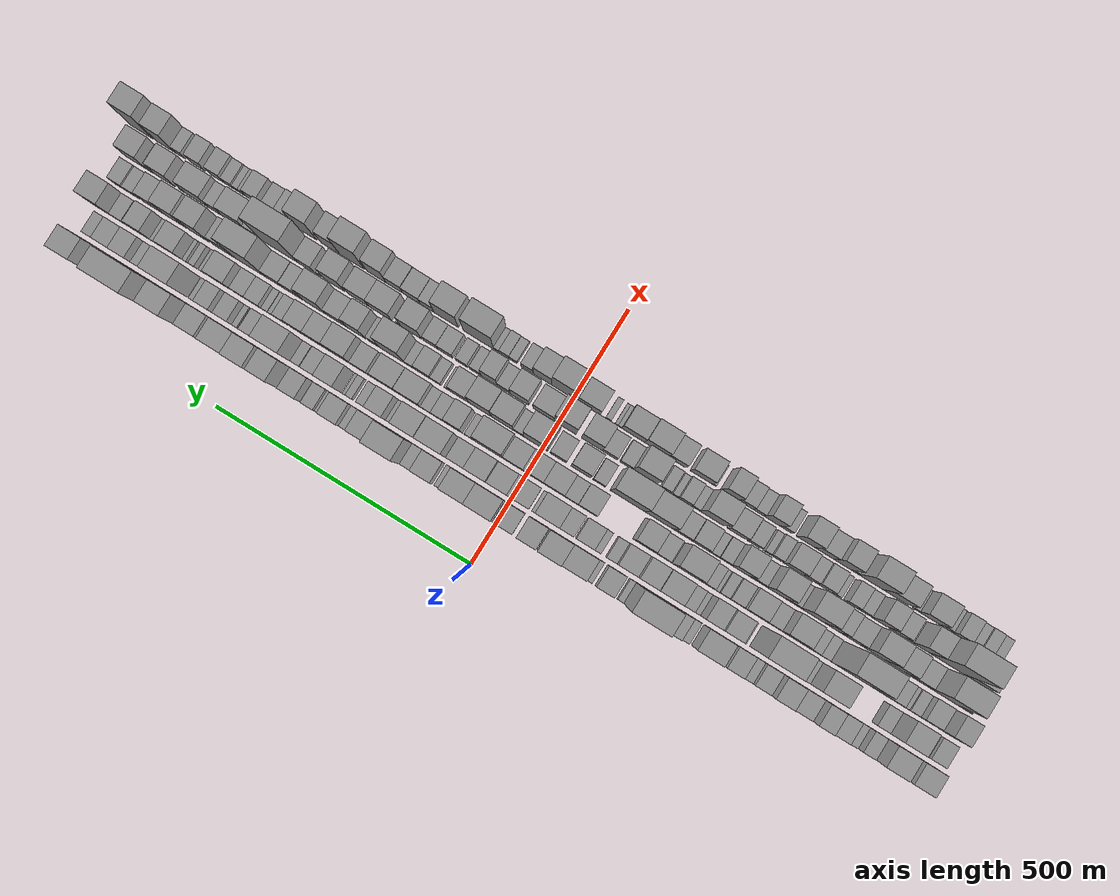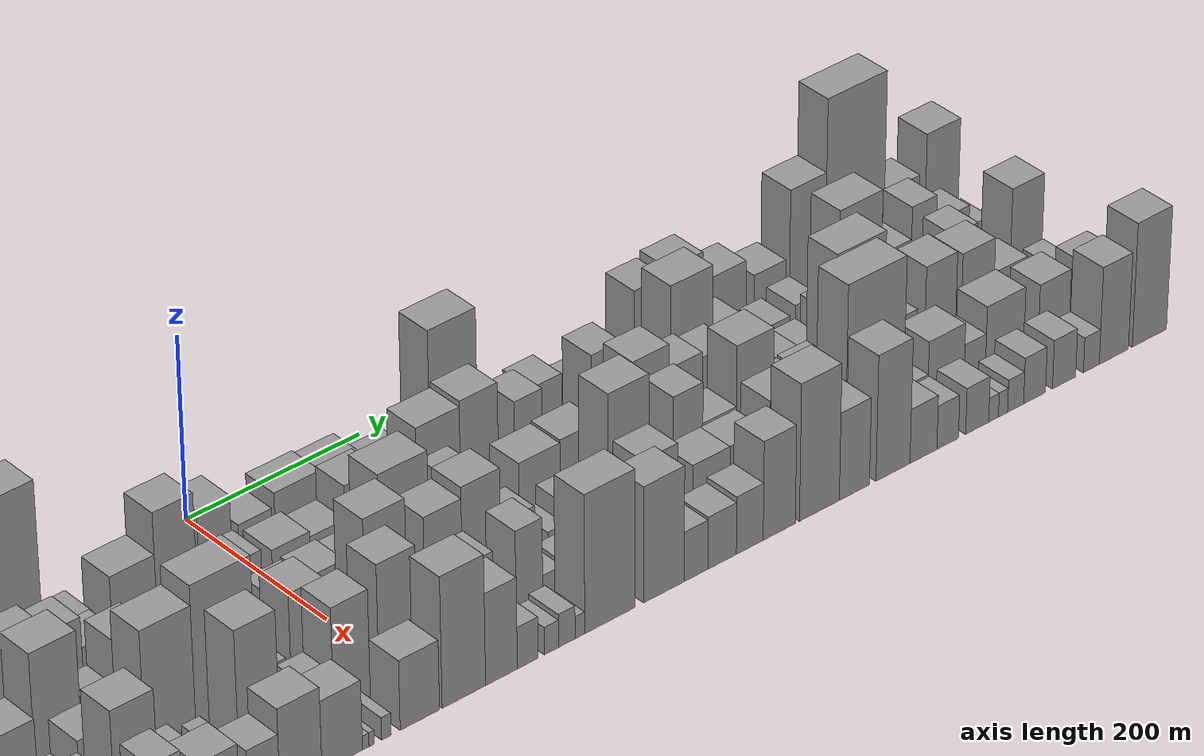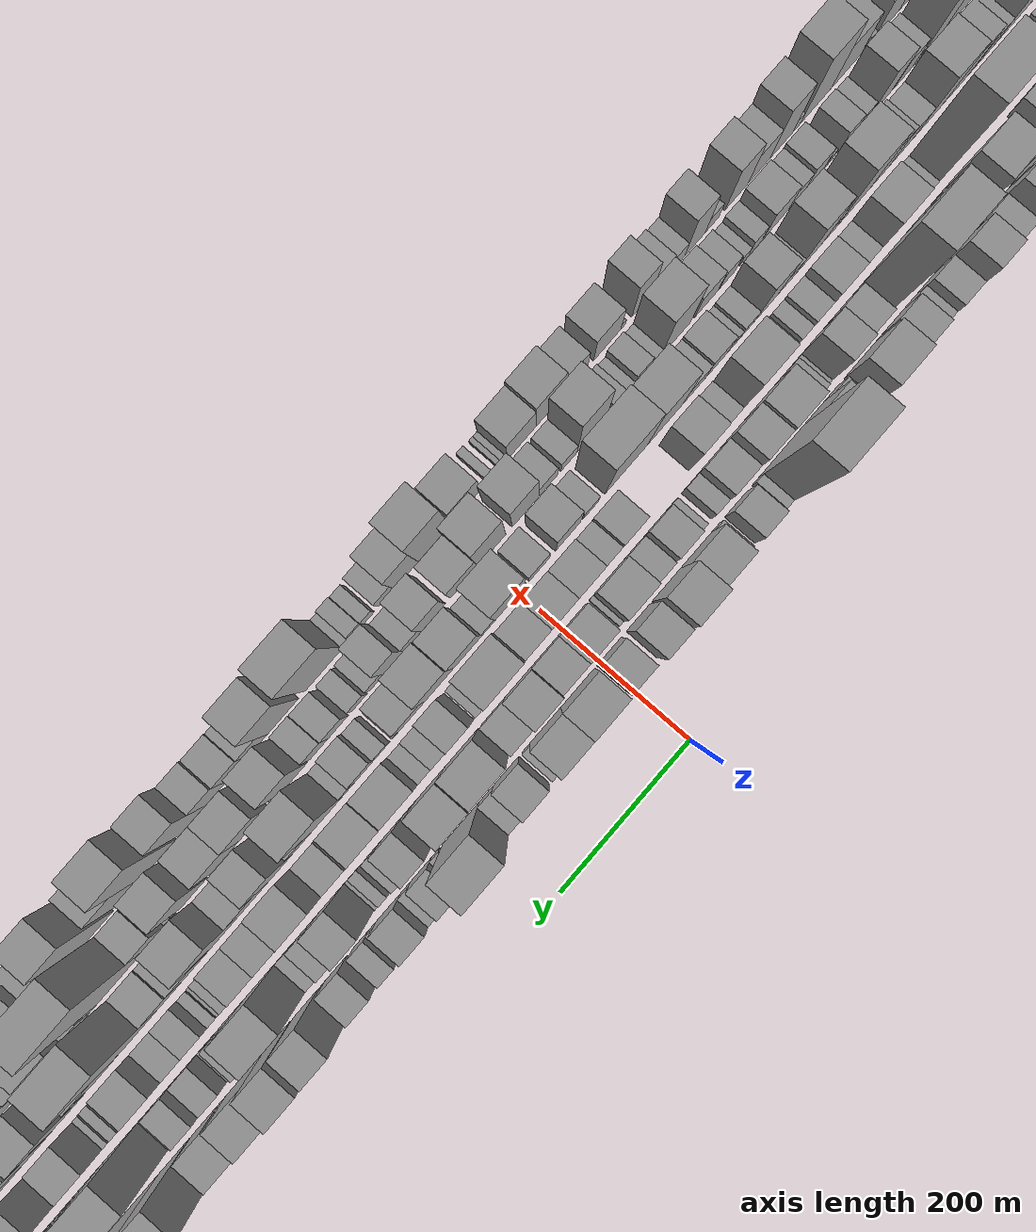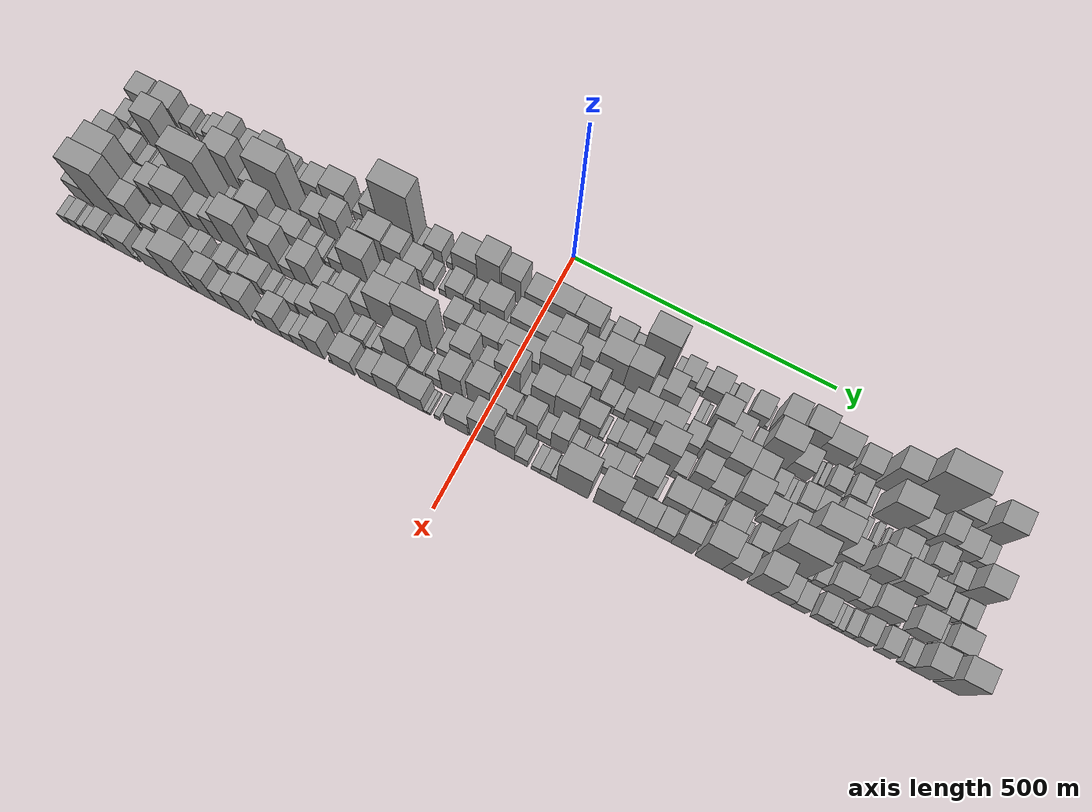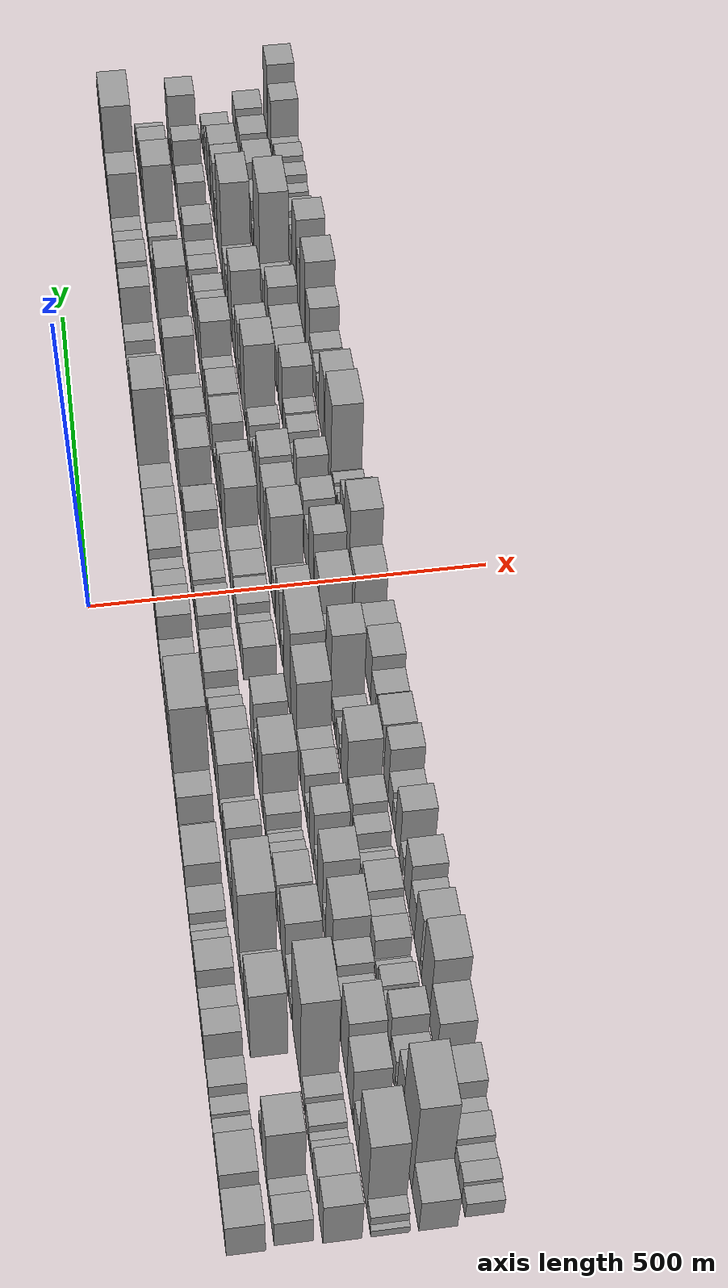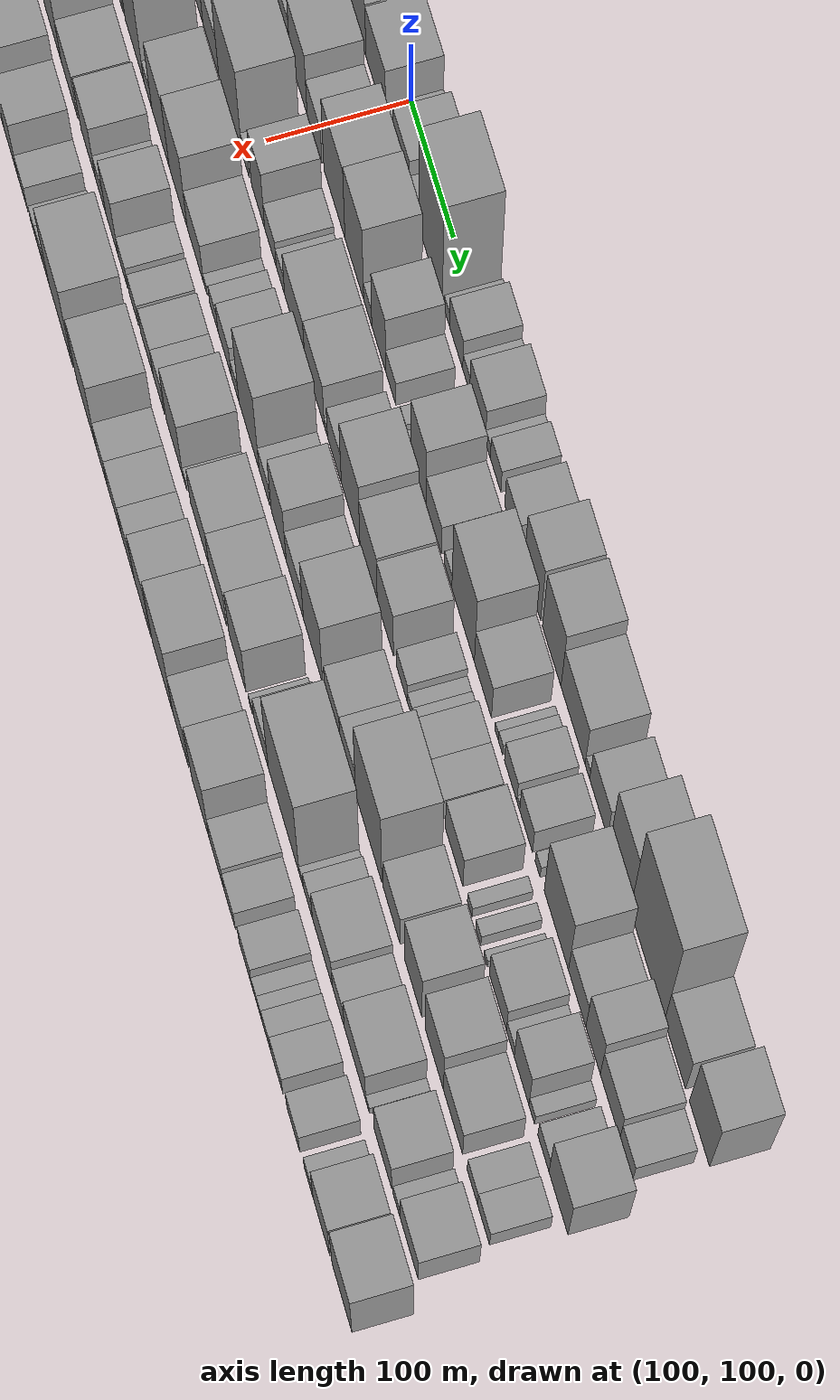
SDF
<sdf version="1.6">
 <world name="default">
  <scene>
   <sky><clouds><speed>12</speed></clouds></sky>
   <ambient>0.4 0.4 0.4 1</ambient>
   <background>0.7 0.7 0.7 1</background>
   <shadows>1</shadows>
  </scene>
  <gravity>0 0 -9.8066</gravity>
  <magnetic_field>6e-06 2.3e-05 -4.2e-05</magnetic_field>
  <physics default="0" name="default_physics" type="ode">
   <ode>
    <solver>
     <type>quick</type>
     <iters>10</iters>
     <sor>1.0</sor>
     <use_dynamic_moi_rescaling>0</use_dynamic_moi_rescaling>
    </solver>
    <constraints>
     <cfm>0</cfm>
     <erp>0.2</erp>
     <contact_max_correcting_vel>100</contact_max_correcting_vel>
     <contact_surface_layer>0.001</contact_surface_layer>
    </constraints>
   </ode>
   <max_step_size>0.004</max_step_size>
   <real_time_factor>1</real_time_factor>
   <real_time_update_rate>250</real_time_update_rate>
  </physics>
  <light name="sun" type="directional">
   <pose>0 0 10 0 0 0</pose>
   <diffuse>0.8 0.8 0.8 1</diffuse>
   <specular>0.2 0.2 0.2 1</specular>
   <attenuation>
    <range>1000</range>
    <constant>0.9</constant>
    <linear>0.01</linear>
    <quadratic>0.001</quadratic>
   </attenuation>
   <direction>-0.5 0.1 -0.9</direction>
  </light>
  <model name="building_1">
   <static>1</static>
   <pose>100.0000 -809.5537 0 0.000000 0.000000 0.000000</pose>
   <link name="link">
    <pose>0 0 36.00 0 0 0</pose>
    <collision name="collision"><geometry><box><size>40.0000 40.8926 72.0000</size></box></geometry></collision>
    <visual name="visual">
     <cast_shadows>0</cast_shadows>
     <geometry><box><size>40.0000 40.8926 72.0000</size></box></geometry>
     <material>
      <script>
       <uri>model://grey_wall/materials/scripts</uri>
       <uri>model://grey_wall/materials/textures</uri>
       <name>vrc/grey_wall</name>
      </script>
     </material>
    </visual>
   </link>
  </model>
  <model name="building_2">
   <static>1</static>
   <pose>100.0000 -784.1616 0 0.000000 0.000000 0.000000</pose>
   <link name="link">
    <pose>0 0 10.50 0 0 0</pose>
    <collision name="collision"><geometry><box><size>40.0000 9.8917 21.0000</size></box></geometry></collision>
    <visual name="visual">
     <cast_shadows>0</cast_shadows>
     <geometry><box><size>40.0000 9.8917 21.0000</size></box></geometry>
     <material>
      <script>
       <uri>model://grey_wall/materials/scripts</uri>
       <uri>model://grey_wall/materials/textures</uri>
       <name>vrc/grey_wall</name>
      </script>
     </material>
    </visual>
   </link>
  </model>
  <model name="building_3">
   <static>1</static>
   <pose>100.0000 -756.8872 0 0.000000 0.000000 0.000000</pose>
   <link name="link">
    <pose>0 0 40.50 0 0 0</pose>
    <collision name="collision"><geometry><box><size>40.0000 44.6570 81.0000</size></box></geometry></collision>
    <visual name="visual">
     <cast_shadows>0</cast_shadows>
     <geometry><box><size>40.0000 44.6570 81.0000</size></box></geometry>
     <material>
      <script>
       <uri>model://grey_wall/materials/scripts</uri>
       <uri>model://grey_wall/materials/textures</uri>
       <name>vrc/grey_wall</name>
      </script>
     </material>
    </visual>
   </link>
  </model>
  <model name="building_4">
   <static>1</static>
   <pose>100.0000 -714.4112 0 0.000000 0.000000 0.000000</pose>
   <link name="link">
    <pose>0 0 21.00 0 0 0</pose>
    <collision name="collision"><geometry><box><size>40.0000 24.2951 42.0000</size></box></geometry></collision>
    <visual name="visual">
     <cast_shadows>0</cast_shadows>
     <geometry><box><size>40.0000 24.2951 42.0000</size></box></geometry>
     <material>
      <script>
       <uri>model://grey_wall/materials/scripts</uri>
       <uri>model://grey_wall/materials/textures</uri>
       <name>vrc/grey_wall</name>
      </script>
     </material>
    </visual>
   </link>
  </model>
  <model name="building_5">
   <static>1</static>
   <pose>100.0000 -684.5059 0 0.000000 0.000000 0.000000</pose>
   <link name="link">
    <pose>0 0 16.50 0 0 0</pose>
    <collision name="collision"><geometry><box><size>40.0000 19.5154 33.0000</size></box></geometry></collision>
    <visual name="visual">
     <cast_shadows>0</cast_shadows>
     <geometry><box><size>40.0000 19.5154 33.0000</size></box></geometry>
     <material>
      <script>
       <uri>model://grey_wall/materials/scripts</uri>
       <uri>model://grey_wall/materials/textures</uri>
       <name>vrc/grey_wall</name>
      </script>
     </material>
    </visual>
   </link>
  </model>
  <model name="building_6">
   <static>1</static>
   <pose>100.0000 -659.1388 0 0.000000 0.000000 0.000000</pose>
   <link name="link">
    <pose>0 0 28.50 0 0 0</pose>
    <collision name="collision"><geometry><box><size>40.0000 31.2190 57.0000</size></box></geometry></collision>
    <visual name="visual">
     <cast_shadows>0</cast_shadows>
     <geometry><box><size>40.0000 31.2190 57.0000</size></box></geometry>
     <material>
      <script>
       <uri>model://grey_wall/materials/scripts</uri>
       <uri>model://grey_wall/materials/textures</uri>
       <name>vrc/grey_wall</name>
      </script>
     </material>
    </visual>
   </link>
  </model>
  <model name="building_7">
   <static>1</static>
   <pose>100.0000 -620.6411 0 0.000000 0.000000 0.000000</pose>
   <link name="link">
    <pose>0 0 48.00 0 0 0</pose>
    <collision name="collision"><geometry><box><size>40.0000 29.7763 96.0000</size></box></geometry></collision>
    <visual name="visual">
     <cast_shadows>0</cast_shadows>
     <geometry><box><size>40.0000 29.7763 96.0000</size></box></geometry>
     <material>
      <script>
       <uri>model://grey_wall/materials/scripts</uri>
       <uri>model://grey_wall/materials/textures</uri>
       <name>vrc/grey_wall</name>
      </script>
     </material>
    </visual>
   </link>
  </model>
  <model name="building_8">
   <static>1</static>
   <pose>100.0000 -583.9597 0 0.000000 0.000000 0.000000</pose>
   <link name="link">
    <pose>0 0 33.00 0 0 0</pose>
    <collision name="collision"><geometry><box><size>40.0000 35.5866 66.0000</size></box></geometry></collision>
    <visual name="visual">
     <cast_shadows>0</cast_shadows>
     <geometry><box><size>40.0000 35.5866 66.0000</size></box></geometry>
     <material>
      <script>
       <uri>model://grey_wall/materials/scripts</uri>
       <uri>model://grey_wall/materials/textures</uri>
       <name>vrc/grey_wall</name>
      </script>
     </material>
    </visual>
   </link>
  </model>
  <model name="building_9">
   <static>1</static>
   <pose>100.0000 -543.9890 0 0.000000 0.000000 0.000000</pose>
   <link name="link">
    <pose>0 0 48.00 0 0 0</pose>
    <collision name="collision"><geometry><box><size>40.0000 36.3549 96.0000</size></box></geometry></collision>
    <visual name="visual">
     <cast_shadows>0</cast_shadows>
     <geometry><box><size>40.0000 36.3549 96.0000</size></box></geometry>
     <material>
      <script>
       <uri>model://grey_wall/materials/scripts</uri>
       <uri>model://grey_wall/materials/textures</uri>
       <name>vrc/grey_wall</name>
      </script>
     </material>
    </visual>
   </link>
  </model>
  <model name="building_10">
   <static>1</static>
   <pose>100.0000 -510.0783 0 0.000000 0.000000 0.000000</pose>
   <link name="link">
    <pose>0 0 28.50 0 0 0</pose>
    <collision name="collision"><geometry><box><size>40.0000 31.4664 57.0000</size></box></geometry></collision>
    <visual name="visual">
     <cast_shadows>0</cast_shadows>
     <geometry><box><size>40.0000 31.4664 57.0000</size></box></geometry>
     <material>
      <script>
       <uri>model://grey_wall/materials/scripts</uri>
       <uri>model://grey_wall/materials/textures</uri>
       <name>vrc/grey_wall</name>
      </script>
     </material>
    </visual>
   </link>
  </model>
  <model name="building_11">
   <static>1</static>
   <pose>100.0000 -484.4417 0 0.000000 0.000000 0.000000</pose>
   <link name="link">
    <pose>0 0 18.00 0 0 0</pose>
    <collision name="collision"><geometry><box><size>40.0000 19.8068 36.0000</size></box></geometry></collision>
    <visual name="visual">
     <cast_shadows>0</cast_shadows>
     <geometry><box><size>40.0000 19.8068 36.0000</size></box></geometry>
     <material>
      <script>
       <uri>model://grey_wall/materials/scripts</uri>
       <uri>model://grey_wall/materials/textures</uri>
       <name>vrc/grey_wall</name>
      </script>
     </material>
    </visual>
   </link>
  </model>
  <model name="building_12">
   <static>1</static>
   <pose>100.0000 -457.7605 0 0.000000 0.000000 0.000000</pose>
   <link name="link">
    <pose>0 0 30.00 0 0 0</pose>
    <collision name="collision"><geometry><box><size>40.0000 33.5557 60.0000</size></box></geometry></collision>
    <visual name="visual">
     <cast_shadows>0</cast_shadows>
     <geometry><box><size>40.0000 33.5557 60.0000</size></box></geometry>
     <material>
      <script>
       <uri>model://grey_wall/materials/scripts</uri>
       <uri>model://grey_wall/materials/textures</uri>
       <name>vrc/grey_wall</name>
      </script>
     </material>
    </visual>
   </link>
  </model>
  <model name="building_13">
   <static>1</static>
   <pose>100.0000 -436.4602 0 0.000000 0.000000 0.000000</pose>
   <link name="link">
    <pose>0 0 10.50 0 0 0</pose>
    <collision name="collision"><geometry><box><size>40.0000 9.0448 21.0000</size></box></geometry></collision>
    <visual name="visual">
     <cast_shadows>0</cast_shadows>
     <geometry><box><size>40.0000 9.0448 21.0000</size></box></geometry>
     <material>
      <script>
       <uri>model://grey_wall/materials/scripts</uri>
       <uri>model://grey_wall/materials/textures</uri>
       <name>vrc/grey_wall</name>
      </script>
     </material>
    </visual>
   </link>
  </model>
  <model name="building_14">
   <static>1</static>
   <pose>100.0000 -406.3923 0 0.000000 0.000000 0.000000</pose>
   <link name="link">
    <pose>0 0 45.00 0 0 0</pose>
    <collision name="collision"><geometry><box><size>40.0000 51.0911 90.0000</size></box></geometry></collision>
    <visual name="visual">
     <cast_shadows>0</cast_shadows>
     <geometry><box><size>40.0000 51.0911 90.0000</size></box></geometry>
     <material>
      <script>
       <uri>model://grey_wall/materials/scripts</uri>
       <uri>model://grey_wall/materials/textures</uri>
       <name>vrc/grey_wall</name>
      </script>
     </material>
    </visual>
   </link>
  </model>
  <model name="building_15">
   <static>1</static>
   <pose>100.0000 -361.3320 0 0.000000 0.000000 0.000000</pose>
   <link name="link">
    <pose>0 0 21.00 0 0 0</pose>
    <collision name="collision"><geometry><box><size>40.0000 21.0296 42.0000</size></box></geometry></collision>
    <visual name="visual">
     <cast_shadows>0</cast_shadows>
     <geometry><box><size>40.0000 21.0296 42.0000</size></box></geometry>
     <material>
      <script>
       <uri>model://grey_wall/materials/scripts</uri>
       <uri>model://grey_wall/materials/textures</uri>
       <name>vrc/grey_wall</name>
      </script>
     </material>
    </visual>
   </link>
  </model>
  <model name="building_16">
   <static>1</static>
   <pose>100.0000 -334.5592 0 0.000000 0.000000 0.000000</pose>
   <link name="link">
    <pose>0 0 49.50 0 0 0</pose>
    <collision name="collision"><geometry><box><size>40.0000 32.5159 99.0000</size></box></geometry></collision>
    <visual name="visual">
     <cast_shadows>0</cast_shadows>
     <geometry><box><size>40.0000 32.5159 99.0000</size></box></geometry>
     <material>
      <script>
       <uri>model://grey_wall/materials/scripts</uri>
       <uri>model://grey_wall/materials/textures</uri>
       <name>vrc/grey_wall</name>
      </script>
     </material>
    </visual>
   </link>
  </model>
  <model name="building_17">
   <static>1</static>
   <pose>100.0000 -282.7788 0 0.000000 0.000000 0.000000</pose>
   <link name="link">
    <pose>0 0 112.50 0 0 0</pose>
    <collision name="collision"><geometry><box><size>40.0000 71.0450 225.0000</size></box></geometry></collision>
    <visual name="visual">
     <cast_shadows>0</cast_shadows>
     <geometry><box><size>40.0000 71.0450 225.0000</size></box></geometry>
     <material>
      <script>
       <uri>model://grey_wall/materials/scripts</uri>
       <uri>model://grey_wall/materials/textures</uri>
       <name>vrc/grey_wall</name>
      </script>
     </material>
    </visual>
   </link>
  </model>
  <model name="building_18">
   <static>1</static>
   <pose>100.0000 -241.5835 0 0.000000 0.000000 0.000000</pose>
   <link name="link">
    <pose>0 0 13.50 0 0 0</pose>
    <collision name="collision"><geometry><box><size>40.0000 11.3455 27.0000</size></box></geometry></collision>
    <visual name="visual">
     <cast_shadows>0</cast_shadows>
     <geometry><box><size>40.0000 11.3455 27.0000</size></box></geometry>
     <material>
      <script>
       <uri>model://grey_wall/materials/scripts</uri>
       <uri>model://grey_wall/materials/textures</uri>
       <name>vrc/grey_wall</name>
      </script>
     </material>
    </visual>
   </link>
  </model>
  <model name="building_19">
   <static>1</static>
   <pose>100.0000 -210.6910 0 0.000000 0.000000 0.000000</pose>
   <link name="link">
    <pose>0 0 30.00 0 0 0</pose>
    <collision name="collision"><geometry><box><size>40.0000 34.4396 60.0000</size></box></geometry></collision>
    <visual name="visual">
     <cast_shadows>0</cast_shadows>
     <geometry><box><size>40.0000 34.4396 60.0000</size></box></geometry>
     <material>
      <script>
       <uri>model://grey_wall/materials/scripts</uri>
       <uri>model://grey_wall/materials/textures</uri>
       <name>vrc/grey_wall</name>
      </script>
     </material>
    </visual>
   </link>
  </model>
  <model name="building_20">
   <static>1</static>
   <pose>100.0000 -180.2853 0 0.000000 0.000000 0.000000</pose>
   <link name="link">
    <pose>0 0 13.50 0 0 0</pose>
    <collision name="collision"><geometry><box><size>40.0000 12.3718 27.0000</size></box></geometry></collision>
    <visual name="visual">
     <cast_shadows>0</cast_shadows>
     <geometry><box><size>40.0000 12.3718 27.0000</size></box></geometry>
     <material>
      <script>
       <uri>model://grey_wall/materials/scripts</uri>
       <uri>model://grey_wall/materials/textures</uri>
       <name>vrc/grey_wall</name>
      </script>
     </material>
    </visual>
   </link>
  </model>
  <model name="building_21">
   <static>1</static>
   <pose>100.0000 -149.5675 0 0.000000 0.000000 0.000000</pose>
   <link name="link">
    <pose>0 0 43.50 0 0 0</pose>
    <collision name="collision"><geometry><box><size>40.0000 49.0637 87.0000</size></box></geometry></collision>
    <visual name="visual">
     <cast_shadows>0</cast_shadows>
     <geometry><box><size>40.0000 49.0637 87.0000</size></box></geometry>
     <material>
      <script>
       <uri>model://grey_wall/materials/scripts</uri>
       <uri>model://grey_wall/materials/textures</uri>
       <name>vrc/grey_wall</name>
      </script>
     </material>
    </visual>
   </link>
  </model>
  <model name="building_22">
   <static>1</static>
   <pose>100.0000 -102.7013 0 0.000000 0.000000 0.000000</pose>
   <link name="link">
    <pose>0 0 66.00 0 0 0</pose>
    <collision name="collision"><geometry><box><size>40.0000 44.6686 132.0000</size></box></geometry></collision>
    <visual name="visual">
     <cast_shadows>0</cast_shadows>
     <geometry><box><size>40.0000 44.6686 132.0000</size></box></geometry>
     <material>
      <script>
       <uri>model://grey_wall/materials/scripts</uri>
       <uri>model://grey_wall/materials/textures</uri>
       <name>vrc/grey_wall</name>
      </script>
     </material>
    </visual>
   </link>
  </model>
  <model name="building_23">
   <static>1</static>
   <pose>100.0000 -58.9814 0 0.000000 0.000000 0.000000</pose>
   <link name="link">
    <pose>0 0 55.50 0 0 0</pose>
    <collision name="collision"><geometry><box><size>40.0000 36.7712 111.0000</size></box></geometry></collision>
    <visual name="visual">
     <cast_shadows>0</cast_shadows>
     <geometry><box><size>40.0000 36.7712 111.0000</size></box></geometry>
     <material>
      <script>
       <uri>model://grey_wall/materials/scripts</uri>
       <uri>model://grey_wall/materials/textures</uri>
       <name>vrc/grey_wall</name>
      </script>
     </material>
    </visual>
   </link>
  </model>
  <model name="building_24">
   <static>1</static>
   <pose>100.0000 -13.7716 0 0.000000 0.000000 0.000000</pose>
   <link name="link">
    <pose>0 0 37.50 0 0 0</pose>
    <collision name="collision"><geometry><box><size>40.0000 37.6485 75.0000</size></box></geometry></collision>
    <visual name="visual">
     <cast_shadows>0</cast_shadows>
     <geometry><box><size>40.0000 37.6485 75.0000</size></box></geometry>
     <material>
      <script>
       <uri>model://grey_wall/materials/scripts</uri>
       <uri>model://grey_wall/materials/textures</uri>
       <name>vrc/grey_wall</name>
      </script>
     </material>
    </visual>
   </link>
  </model>
  <model name="building_25">
   <static>1</static>
   <pose>100.0000 34.4187 0 0.000000 0.000000 0.000000</pose>
   <link name="link">
    <pose>0 0 45.00 0 0 0</pose>
    <collision name="collision"><geometry><box><size>40.0000 52.7319 90.0000</size></box></geometry></collision>
    <visual name="visual">
     <cast_shadows>0</cast_shadows>
     <geometry><box><size>40.0000 52.7319 90.0000</size></box></geometry>
     <material>
      <script>
       <uri>model://grey_wall/materials/scripts</uri>
       <uri>model://grey_wall/materials/textures</uri>
       <name>vrc/grey_wall</name>
      </script>
     </material>
    </visual>
   </link>
  </model>
  <model name="building_26">
   <static>1</static>
   <pose>100.0000 84.2863 0 0.000000 0.000000 0.000000</pose>
   <link name="link">
    <pose>0 0 43.50 0 0 0</pose>
    <collision name="collision"><geometry><box><size>40.0000 47.0033 87.0000</size></box></geometry></collision>
    <visual name="visual">
     <cast_shadows>0</cast_shadows>
     <geometry><box><size>40.0000 47.0033 87.0000</size></box></geometry>
     <material>
      <script>
       <uri>model://grey_wall/materials/scripts</uri>
       <uri>model://grey_wall/materials/textures</uri>
       <name>vrc/grey_wall</name>
      </script>
     </material>
    </visual>
   </link>
  </model>
  <model name="building_27">
   <static>1</static>
   <pose>100.0000 113.9015 0 0.000000 0.000000 0.000000</pose>
   <link name="link">
    <pose>0 0 13.50 0 0 0</pose>
    <collision name="collision"><geometry><box><size>40.0000 12.2271 27.0000</size></box></geometry></collision>
    <visual name="visual">
     <cast_shadows>0</cast_shadows>
     <geometry><box><size>40.0000 12.2271 27.0000</size></box></geometry>
     <material>
      <script>
       <uri>model://grey_wall/materials/scripts</uri>
       <uri>model://grey_wall/materials/textures</uri>
       <name>vrc/grey_wall</name>
      </script>
     </material>
    </visual>
   </link>
  </model>
  <model name="building_28">
   <static>1</static>
   <pose>100.0000 144.5365 0 0.000000 0.000000 0.000000</pose>
   <link name="link">
    <pose>0 0 33.00 0 0 0</pose>
    <collision name="collision"><geometry><box><size>40.0000 39.0430 66.0000</size></box></geometry></collision>
    <visual name="visual">
     <cast_shadows>0</cast_shadows>
     <geometry><box><size>40.0000 39.0430 66.0000</size></box></geometry>
     <material>
      <script>
       <uri>model://grey_wall/materials/scripts</uri>
       <uri>model://grey_wall/materials/textures</uri>
       <name>vrc/grey_wall</name>
      </script>
     </material>
    </visual>
   </link>
  </model>
  <model name="building_29">
   <static>1</static>
   <pose>100.0000 174.8600 0 0.000000 0.000000 0.000000</pose>
   <link name="link">
    <pose>0 0 19.50 0 0 0</pose>
    <collision name="collision"><geometry><box><size>40.0000 21.6038 39.0000</size></box></geometry></collision>
    <visual name="visual">
     <cast_shadows>0</cast_shadows>
     <geometry><box><size>40.0000 21.6038 39.0000</size></box></geometry>
     <material>
      <script>
       <uri>model://grey_wall/materials/scripts</uri>
       <uri>model://grey_wall/materials/textures</uri>
       <name>vrc/grey_wall</name>
      </script>
     </material>
    </visual>
   </link>
  </model>
  <model name="building_30">
   <static>1</static>
   <pose>100.0000 213.5052 0 0.000000 0.000000 0.000000</pose>
   <link name="link">
    <pose>0 0 91.50 0 0 0</pose>
    <collision name="collision"><geometry><box><size>40.0000 55.6866 183.0000</size></box></geometry></collision>
    <visual name="visual">
     <cast_shadows>0</cast_shadows>
     <geometry><box><size>40.0000 55.6866 183.0000</size></box></geometry>
     <material>
      <script>
       <uri>model://grey_wall/materials/scripts</uri>
       <uri>model://grey_wall/materials/textures</uri>
       <name>vrc/grey_wall</name>
      </script>
     </material>
    </visual>
   </link>
  </model>
  <model name="building_31">
   <static>1</static>
   <pose>100.0000 251.6890 0 0.000000 0.000000 0.000000</pose>
   <link name="link">
    <pose>0 0 13.50 0 0 0</pose>
    <collision name="collision"><geometry><box><size>40.0000 12.6810 27.0000</size></box></geometry></collision>
    <visual name="visual">
     <cast_shadows>0</cast_shadows>
     <geometry><box><size>40.0000 12.6810 27.0000</size></box></geometry>
     <material>
      <script>
       <uri>model://grey_wall/materials/scripts</uri>
       <uri>model://grey_wall/materials/textures</uri>
       <name>vrc/grey_wall</name>
      </script>
     </material>
    </visual>
   </link>
  </model>
  <model name="building_32">
   <static>1</static>
   <pose>100.0000 273.4831 0 0.000000 0.000000 0.000000</pose>
   <link name="link">
    <pose>0 0 28.50 0 0 0</pose>
    <collision name="collision"><geometry><box><size>40.0000 30.9074 57.0000</size></box></geometry></collision>
    <visual name="visual">
     <cast_shadows>0</cast_shadows>
     <geometry><box><size>40.0000 30.9074 57.0000</size></box></geometry>
     <material>
      <script>
       <uri>model://grey_wall/materials/scripts</uri>
       <uri>model://grey_wall/materials/textures</uri>
       <name>vrc/grey_wall</name>
      </script>
     </material>
    </visual>
   </link>
  </model>
  <model name="building_33">
   <static>1</static>
   <pose>100.0000 296.9893 0 0.000000 0.000000 0.000000</pose>
   <link name="link">
    <pose>0 0 15.00 0 0 0</pose>
    <collision name="collision"><geometry><box><size>40.0000 16.1050 30.0000</size></box></geometry></collision>
    <visual name="visual">
     <cast_shadows>0</cast_shadows>
     <geometry><box><size>40.0000 16.1050 30.0000</size></box></geometry>
     <material>
      <script>
       <uri>model://grey_wall/materials/scripts</uri>
       <uri>model://grey_wall/materials/textures</uri>
       <name>vrc/grey_wall</name>
      </script>
     </material>
    </visual>
   </link>
  </model>
  <model name="building_34">
   <static>1</static>
   <pose>100.0000 323.2109 0 0.000000 0.000000 0.000000</pose>
   <link name="link">
    <pose>0 0 33.00 0 0 0</pose>
    <collision name="collision"><geometry><box><size>40.0000 36.3383 66.0000</size></box></geometry></collision>
    <visual name="visual">
     <cast_shadows>0</cast_shadows>
     <geometry><box><size>40.0000 36.3383 66.0000</size></box></geometry>
     <material>
      <script>
       <uri>model://grey_wall/materials/scripts</uri>
       <uri>model://grey_wall/materials/textures</uri>
       <name>vrc/grey_wall</name>
      </script>
     </material>
    </visual>
   </link>
  </model>
  <model name="building_35">
   <static>1</static>
   <pose>100.0000 347.0248 0 0.000000 0.000000 0.000000</pose>
   <link name="link">
    <pose>0 0 13.50 0 0 0</pose>
    <collision name="collision"><geometry><box><size>40.0000 11.2897 27.0000</size></box></geometry></collision>
    <visual name="visual">
     <cast_shadows>0</cast_shadows>
     <geometry><box><size>40.0000 11.2897 27.0000</size></box></geometry>
     <material>
      <script>
       <uri>model://grey_wall/materials/scripts</uri>
       <uri>model://grey_wall/materials/textures</uri>
       <name>vrc/grey_wall</name>
      </script>
     </material>
    </visual>
   </link>
  </model>
  <model name="building_36">
   <static>1</static>
   <pose>100.0000 364.6943 0 0.000000 0.000000 0.000000</pose>
   <link name="link">
    <pose>0 0 22.50 0 0 0</pose>
    <collision name="collision"><geometry><box><size>40.0000 24.0492 45.0000</size></box></geometry></collision>
    <visual name="visual">
     <cast_shadows>0</cast_shadows>
     <geometry><box><size>40.0000 24.0492 45.0000</size></box></geometry>
     <material>
      <script>
       <uri>model://grey_wall/materials/scripts</uri>
       <uri>model://grey_wall/materials/textures</uri>
       <name>vrc/grey_wall</name>
      </script>
     </material>
    </visual>
   </link>
  </model>
  <model name="building_37">
   <static>1</static>
   <pose>100.0000 402.3013 0 0.000000 0.000000 0.000000</pose>
   <link name="link">
    <pose>0 0 30.00 0 0 0</pose>
    <collision name="collision"><geometry><box><size>40.0000 33.1650 60.0000</size></box></geometry></collision>
    <visual name="visual">
     <cast_shadows>0</cast_shadows>
     <geometry><box><size>40.0000 33.1650 60.0000</size></box></geometry>
     <material>
      <script>
       <uri>model://grey_wall/materials/scripts</uri>
       <uri>model://grey_wall/materials/textures</uri>
       <name>vrc/grey_wall</name>
      </script>
     </material>
    </visual>
   </link>
  </model>
  <model name="building_38">
   <static>1</static>
   <pose>100.0000 422.0885 0 0.000000 0.000000 0.000000</pose>
   <link name="link">
    <pose>0 0 7.50 0 0 0</pose>
    <collision name="collision"><geometry><box><size>40.0000 6.4094 15.0000</size></box></geometry></collision>
    <visual name="visual">
     <cast_shadows>0</cast_shadows>
     <geometry><box><size>40.0000 6.4094 15.0000</size></box></geometry>
     <material>
      <script>
       <uri>model://grey_wall/materials/scripts</uri>
       <uri>model://grey_wall/materials/textures</uri>
       <name>vrc/grey_wall</name>
      </script>
     </material>
    </visual>
   </link>
  </model>
  <model name="building_39">
   <static>1</static>
   <pose>100.0000 448.2193 0 0.000000 0.000000 0.000000</pose>
   <link name="link">
    <pose>0 0 58.50 0 0 0</pose>
    <collision name="collision"><geometry><box><size>40.0000 37.8522 117.0000</size></box></geometry></collision>
    <visual name="visual">
     <cast_shadows>0</cast_shadows>
     <geometry><box><size>40.0000 37.8522 117.0000</size></box></geometry>
     <material>
      <script>
       <uri>model://grey_wall/materials/scripts</uri>
       <uri>model://grey_wall/materials/textures</uri>
       <name>vrc/grey_wall</name>
      </script>
     </material>
    </visual>
   </link>
  </model>
  <model name="building_40">
   <static>1</static>
   <pose>100.0000 492.0342 0 0.000000 0.000000 0.000000</pose>
   <link name="link">
    <pose>0 0 61.50 0 0 0</pose>
    <collision name="collision"><geometry><box><size>40.0000 41.7775 123.0000</size></box></geometry></collision>
    <visual name="visual">
     <cast_shadows>0</cast_shadows>
     <geometry><box><size>40.0000 41.7775 123.0000</size></box></geometry>
     <material>
      <script>
       <uri>model://grey_wall/materials/scripts</uri>
       <uri>model://grey_wall/materials/textures</uri>
       <name>vrc/grey_wall</name>
      </script>
     </material>
    </visual>
   </link>
  </model>
  <model name="building_41">
   <static>1</static>
   <pose>100.0000 539.8576 0 0.000000 0.000000 0.000000</pose>
   <link name="link">
    <pose>0 0 45.00 0 0 0</pose>
    <collision name="collision"><geometry><box><size>40.0000 53.8695 90.0000</size></box></geometry></collision>
    <visual name="visual">
     <cast_shadows>0</cast_shadows>
     <geometry><box><size>40.0000 53.8695 90.0000</size></box></geometry>
     <material>
      <script>
       <uri>model://grey_wall/materials/scripts</uri>
       <uri>model://grey_wall/materials/textures</uri>
       <name>vrc/grey_wall</name>
      </script>
     </material>
    </visual>
   </link>
  </model>
  <model name="building_42">
   <static>1</static>
   <pose>100.0000 571.8155 0 0.000000 0.000000 0.000000</pose>
   <link name="link">
    <pose>0 0 10.50 0 0 0</pose>
    <collision name="collision"><geometry><box><size>40.0000 10.0463 21.0000</size></box></geometry></collision>
    <visual name="visual">
     <cast_shadows>0</cast_shadows>
     <geometry><box><size>40.0000 10.0463 21.0000</size></box></geometry>
     <material>
      <script>
       <uri>model://grey_wall/materials/scripts</uri>
       <uri>model://grey_wall/materials/textures</uri>
       <name>vrc/grey_wall</name>
      </script>
     </material>
    </visual>
   </link>
  </model>
  <model name="building_43">
   <static>1</static>
   <pose>100.0000 596.6419 0 0.000000 0.000000 0.000000</pose>
   <link name="link">
    <pose>0 0 34.50 0 0 0</pose>
    <collision name="collision"><geometry><box><size>40.0000 39.6066 69.0000</size></box></geometry></collision>
    <visual name="visual">
     <cast_shadows>0</cast_shadows>
     <geometry><box><size>40.0000 39.6066 69.0000</size></box></geometry>
     <material>
      <script>
       <uri>model://grey_wall/materials/scripts</uri>
       <uri>model://grey_wall/materials/textures</uri>
       <name>vrc/grey_wall</name>
      </script>
     </material>
    </visual>
   </link>
  </model>
  <model name="building_44">
   <static>1</static>
   <pose>100.0000 643.9634 0 0.000000 0.000000 0.000000</pose>
   <link name="link">
    <pose>0 0 72.00 0 0 0</pose>
    <collision name="collision"><geometry><box><size>40.0000 45.0365 144.0000</size></box></geometry></collision>
    <visual name="visual">
     <cast_shadows>0</cast_shadows>
     <geometry><box><size>40.0000 45.0365 144.0000</size></box></geometry>
     <material>
      <script>
       <uri>model://grey_wall/materials/scripts</uri>
       <uri>model://grey_wall/materials/textures</uri>
       <name>vrc/grey_wall</name>
      </script>
     </material>
    </visual>
   </link>
  </model>
  <model name="building_45">
   <static>1</static>
   <pose>100.0000 703.7926 0 0.000000 0.000000 0.000000</pose>
   <link name="link">
    <pose>0 0 112.50 0 0 0</pose>
    <collision name="collision"><geometry><box><size>40.0000 74.6218 225.0000</size></box></geometry></collision>
    <visual name="visual">
     <cast_shadows>0</cast_shadows>
     <geometry><box><size>40.0000 74.6218 225.0000</size></box></geometry>
     <material>
      <script>
       <uri>model://grey_wall/materials/scripts</uri>
       <uri>model://grey_wall/materials/textures</uri>
       <name>vrc/grey_wall</name>
      </script>
     </material>
    </visual>
   </link>
  </model>
  <model name="building_46">
   <static>1</static>
   <pose>100.0000 763.8912 0 0.000000 0.000000 0.000000</pose>
   <link name="link">
    <pose>0 0 45.00 0 0 0</pose>
    <collision name="collision"><geometry><box><size>40.0000 45.5754 90.0000</size></box></geometry></collision>
    <visual name="visual">
     <cast_shadows>0</cast_shadows>
     <geometry><box><size>40.0000 45.5754 90.0000</size></box></geometry>
     <material>
      <script>
       <uri>model://grey_wall/materials/scripts</uri>
       <uri>model://grey_wall/materials/textures</uri>
       <name>vrc/grey_wall</name>
      </script>
     </material>
    </visual>
   </link>
  </model>
  <model name="building_47">
   <static>1</static>
   <pose>100.0000 816.3652 0 0.000000 0.000000 0.000000</pose>
   <link name="link">
    <pose>0 0 66.00 0 0 0</pose>
    <collision name="collision"><geometry><box><size>40.0000 43.3727 132.0000</size></box></geometry></collision>
    <visual name="visual">
     <cast_shadows>0</cast_shadows>
     <geometry><box><size>40.0000 43.3727 132.0000</size></box></geometry>
     <material>
      <script>
       <uri>model://grey_wall/materials/scripts</uri>
       <uri>model://grey_wall/materials/textures</uri>
       <name>vrc/grey_wall</name>
      </script>
     </material>
    </visual>
   </link>
  </model>
  <model name="building_48">
   <static>1</static>
   <pose>149.0000 -811.1918 0 0.000000 0.000000 0.000000</pose>
   <link name="link">
    <pose>0 0 28.50 0 0 0</pose>
    <collision name="collision"><geometry><box><size>40.0000 29.6163 57.0000</size></box></geometry></collision>
    <visual name="visual">
     <cast_shadows>0</cast_shadows>
     <geometry><box><size>40.0000 29.6163 57.0000</size></box></geometry>
     <material>
      <script>
       <uri>model://grey_wall/materials/scripts</uri>
       <uri>model://grey_wall/materials/textures</uri>
       <name>vrc/grey_wall</name>
      </script>
     </material>
    </visual>
   </link>
  </model>
  <model name="building_49">
   <static>1</static>
   <pose>149.0000 -784.8462 0 0.000000 0.000000 0.000000</pose>
   <link name="link">
    <pose>0 0 21.00 0 0 0</pose>
    <collision name="collision"><geometry><box><size>40.0000 23.0750 42.0000</size></box></geometry></collision>
    <visual name="visual">
     <cast_shadows>0</cast_shadows>
     <geometry><box><size>40.0000 23.0750 42.0000</size></box></geometry>
     <material>
      <script>
       <uri>model://grey_wall/materials/scripts</uri>
       <uri>model://grey_wall/materials/textures</uri>
       <name>vrc/grey_wall</name>
      </script>
     </material>
    </visual>
   </link>
  </model>
  <model name="building_50">
   <static>1</static>
   <pose>149.0000 -745.3304 0 0.000000 0.000000 0.000000</pose>
   <link name="link">
    <pose>0 0 66.00 0 0 0</pose>
    <collision name="collision"><geometry><box><size>40.0000 41.9566 132.0000</size></box></geometry></collision>
    <visual name="visual">
     <cast_shadows>0</cast_shadows>
     <geometry><box><size>40.0000 41.9566 132.0000</size></box></geometry>
     <material>
      <script>
       <uri>model://grey_wall/materials/scripts</uri>
       <uri>model://grey_wall/materials/textures</uri>
       <name>vrc/grey_wall</name>
      </script>
     </material>
    </visual>
   </link>
  </model>
  <model name="building_51">
   <static>1</static>
   <pose>149.0000 -711.9755 0 0.000000 0.000000 0.000000</pose>
   <link name="link">
    <pose>0 0 21.00 0 0 0</pose>
    <collision name="collision"><geometry><box><size>40.0000 24.7531 42.0000</size></box></geometry></collision>
    <visual name="visual">
     <cast_shadows>0</cast_shadows>
     <geometry><box><size>40.0000 24.7531 42.0000</size></box></geometry>
     <material>
      <script>
       <uri>model://grey_wall/materials/scripts</uri>
       <uri>model://grey_wall/materials/textures</uri>
       <name>vrc/grey_wall</name>
      </script>
     </material>
    </visual>
   </link>
  </model>
  <model name="building_52">
   <static>1</static>
   <pose>149.0000 -596.8694 0 0.000000 0.000000 0.000000</pose>
   <link name="link">
    <pose>0 0 70.50 0 0 0</pose>
    <collision name="collision"><geometry><box><size>40.0000 48.4864 141.0000</size></box></geometry></collision>
    <visual name="visual">
     <cast_shadows>0</cast_shadows>
     <geometry><box><size>40.0000 48.4864 141.0000</size></box></geometry>
     <material>
      <script>
       <uri>model://grey_wall/materials/scripts</uri>
       <uri>model://grey_wall/materials/textures</uri>
       <name>vrc/grey_wall</name>
      </script>
     </material>
    </visual>
   </link>
  </model>
  <model name="building_53">
   <static>1</static>
   <pose>149.0000 -548.5624 0 0.000000 0.000000 0.000000</pose>
   <link name="link">
    <pose>0 0 33.00 0 0 0</pose>
    <collision name="collision"><geometry><box><size>40.0000 36.1278 66.0000</size></box></geometry></collision>
    <visual name="visual">
     <cast_shadows>0</cast_shadows>
     <geometry><box><size>40.0000 36.1278 66.0000</size></box></geometry>
     <material>
      <script>
       <uri>model://grey_wall/materials/scripts</uri>
       <uri>model://grey_wall/materials/textures</uri>
       <name>vrc/grey_wall</name>
      </script>
     </material>
    </visual>
   </link>
  </model>
  <model name="building_54">
   <static>1</static>
   <pose>149.0000 -497.0256 0 0.000000 0.000000 0.000000</pose>
   <link name="link">
    <pose>0 0 94.50 0 0 0</pose>
    <collision name="collision"><geometry><box><size>40.0000 66.9458 189.0000</size></box></geometry></collision>
    <visual name="visual">
     <cast_shadows>0</cast_shadows>
     <geometry><box><size>40.0000 66.9458 189.0000</size></box></geometry>
     <material>
      <script>
       <uri>model://grey_wall/materials/scripts</uri>
       <uri>model://grey_wall/materials/textures</uri>
       <name>vrc/grey_wall</name>
      </script>
     </material>
    </visual>
   </link>
  </model>
  <model name="building_55">
   <static>1</static>
   <pose>149.0000 -448.6384 0 0.000000 0.000000 0.000000</pose>
   <link name="link">
    <pose>0 0 10.50 0 0 0</pose>
    <collision name="collision"><geometry><box><size>40.0000 9.8285 21.0000</size></box></geometry></collision>
    <visual name="visual">
     <cast_shadows>0</cast_shadows>
     <geometry><box><size>40.0000 9.8285 21.0000</size></box></geometry>
     <material>
      <script>
       <uri>model://grey_wall/materials/scripts</uri>
       <uri>model://grey_wall/materials/textures</uri>
       <name>vrc/grey_wall</name>
      </script>
     </material>
    </visual>
   </link>
  </model>
  <model name="building_56">
   <static>1</static>
   <pose>149.0000 -425.2524 0 0.000000 0.000000 0.000000</pose>
   <link name="link">
    <pose>0 0 33.00 0 0 0</pose>
    <collision name="collision"><geometry><box><size>40.0000 36.9436 66.0000</size></box></geometry></collision>
    <visual name="visual">
     <cast_shadows>0</cast_shadows>
     <geometry><box><size>40.0000 36.9436 66.0000</size></box></geometry>
     <material>
      <script>
       <uri>model://grey_wall/materials/scripts</uri>
       <uri>model://grey_wall/materials/textures</uri>
       <name>vrc/grey_wall</name>
      </script>
     </material>
    </visual>
   </link>
  </model>
  <model name="building_57">
   <static>1</static>
   <pose>149.0000 -382.1029 0 0.000000 0.000000 0.000000</pose>
   <link name="link">
    <pose>0 0 51.00 0 0 0</pose>
    <collision name="collision"><geometry><box><size>40.0000 33.3554 102.0000</size></box></geometry></collision>
    <visual name="visual">
     <cast_shadows>0</cast_shadows>
     <geometry><box><size>40.0000 33.3554 102.0000</size></box></geometry>
     <material>
      <script>
       <uri>model://grey_wall/materials/scripts</uri>
       <uri>model://grey_wall/materials/textures</uri>
       <name>vrc/grey_wall</name>
      </script>
     </material>
    </visual>
   </link>
  </model>
  <model name="building_58">
   <static>1</static>
   <pose>149.0000 -360.3047 0 0.000000 0.000000 0.000000</pose>
   <link name="link">
    <pose>0 0 10.50 0 0 0</pose>
    <collision name="collision"><geometry><box><size>40.0000 10.2410 21.0000</size></box></geometry></collision>
    <visual name="visual">
     <cast_shadows>0</cast_shadows>
     <geometry><box><size>40.0000 10.2410 21.0000</size></box></geometry>
     <material>
      <script>
       <uri>model://grey_wall/materials/scripts</uri>
       <uri>model://grey_wall/materials/textures</uri>
       <name>vrc/grey_wall</name>
      </script>
     </material>
    </visual>
   </link>
  </model>
  <model name="building_59">
   <static>1</static>
   <pose>149.0000 -339.5528 0 0.000000 0.000000 0.000000</pose>
   <link name="link">
    <pose>0 0 24.00 0 0 0</pose>
    <collision name="collision"><geometry><box><size>40.0000 25.2629 48.0000</size></box></geometry></collision>
    <visual name="visual">
     <cast_shadows>0</cast_shadows>
     <geometry><box><size>40.0000 25.2629 48.0000</size></box></geometry>
     <material>
      <script>
       <uri>model://grey_wall/materials/scripts</uri>
       <uri>model://grey_wall/materials/textures</uri>
       <name>vrc/grey_wall</name>
      </script>
     </material>
    </visual>
   </link>
  </model>
  <model name="building_60">
   <static>1</static>
   <pose>149.0000 -301.4753 0 0.000000 0.000000 0.000000</pose>
   <link name="link">
    <pose>0 0 57.00 0 0 0</pose>
    <collision name="collision"><geometry><box><size>40.0000 44.8920 114.0000</size></box></geometry></collision>
    <visual name="visual">
     <cast_shadows>0</cast_shadows>
     <geometry><box><size>40.0000 44.8920 114.0000</size></box></geometry>
     <material>
      <script>
       <uri>model://grey_wall/materials/scripts</uri>
       <uri>model://grey_wall/materials/textures</uri>
       <name>vrc/grey_wall</name>
      </script>
     </material>
    </visual>
   </link>
  </model>
  <model name="building_61">
   <static>1</static>
   <pose>149.0000 -260.5300 0 0.000000 0.000000 0.000000</pose>
   <link name="link">
    <pose>0 0 52.50 0 0 0</pose>
    <collision name="collision"><geometry><box><size>40.0000 36.9986 105.0000</size></box></geometry></collision>
    <visual name="visual">
     <cast_shadows>0</cast_shadows>
     <geometry><box><size>40.0000 36.9986 105.0000</size></box></geometry>
     <material>
      <script>
       <uri>model://grey_wall/materials/scripts</uri>
       <uri>model://grey_wall/materials/textures</uri>
       <name>vrc/grey_wall</name>
      </script>
     </material>
    </visual>
   </link>
  </model>
  <model name="building_62">
   <static>1</static>
   <pose>149.0000 -222.8986 0 0.000000 0.000000 0.000000</pose>
   <link name="link">
    <pose>0 0 36.00 0 0 0</pose>
    <collision name="collision"><geometry><box><size>40.0000 38.2643 72.0000</size></box></geometry></collision>
    <visual name="visual">
     <cast_shadows>0</cast_shadows>
     <geometry><box><size>40.0000 38.2643 72.0000</size></box></geometry>
     <material>
      <script>
       <uri>model://grey_wall/materials/scripts</uri>
       <uri>model://grey_wall/materials/textures</uri>
       <name>vrc/grey_wall</name>
      </script>
     </material>
    </visual>
   </link>
  </model>
  <model name="building_63">
   <static>1</static>
   <pose>149.0000 -193.5696 0 0.000000 0.000000 0.000000</pose>
   <link name="link">
    <pose>0 0 19.50 0 0 0</pose>
    <collision name="collision"><geometry><box><size>40.0000 20.3938 39.0000</size></box></geometry></collision>
    <visual name="visual">
     <cast_shadows>0</cast_shadows>
     <geometry><box><size>40.0000 20.3938 39.0000</size></box></geometry>
     <material>
      <script>
       <uri>model://grey_wall/materials/scripts</uri>
       <uri>model://grey_wall/materials/textures</uri>
       <name>vrc/grey_wall</name>
      </script>
     </material>
    </visual>
   </link>
  </model>
  <model name="building_64">
   <static>1</static>
   <pose>149.0000 -166.6785 0 0.000000 0.000000 0.000000</pose>
   <link name="link">
    <pose>0 0 13.50 0 0 0</pose>
    <collision name="collision"><geometry><box><size>40.0000 13.3885 27.0000</size></box></geometry></collision>
    <visual name="visual">
     <cast_shadows>0</cast_shadows>
     <geometry><box><size>40.0000 13.3885 27.0000</size></box></geometry>
     <material>
      <script>
       <uri>model://grey_wall/materials/scripts</uri>
       <uri>model://grey_wall/materials/textures</uri>
       <name>vrc/grey_wall</name>
      </script>
     </material>
    </visual>
   </link>
  </model>
  <model name="building_65">
   <static>1</static>
   <pose>149.0000 -142.2231 0 0.000000 0.000000 0.000000</pose>
   <link name="link">
    <pose>0 0 30.00 0 0 0</pose>
    <collision name="collision"><geometry><box><size>40.0000 35.5222 60.0000</size></box></geometry></collision>
    <visual name="visual">
     <cast_shadows>0</cast_shadows>
     <geometry><box><size>40.0000 35.5222 60.0000</size></box></geometry>
     <material>
      <script>
       <uri>model://grey_wall/materials/scripts</uri>
       <uri>model://grey_wall/materials/textures</uri>
       <name>vrc/grey_wall</name>
      </script>
     </material>
    </visual>
   </link>
  </model>
  <model name="building_66">
   <static>1</static>
   <pose>149.0000 -106.3887 0 0.000000 0.000000 0.000000</pose>
   <link name="link">
    <pose>0 0 27.00 0 0 0</pose>
    <collision name="collision"><geometry><box><size>40.0000 28.1467 54.0000</size></box></geometry></collision>
    <visual name="visual">
     <cast_shadows>0</cast_shadows>
     <geometry><box><size>40.0000 28.1467 54.0000</size></box></geometry>
     <material>
      <script>
       <uri>model://grey_wall/materials/scripts</uri>
       <uri>model://grey_wall/materials/textures</uri>
       <name>vrc/grey_wall</name>
      </script>
     </material>
    </visual>
   </link>
  </model>
  <model name="building_67">
   <static>1</static>
   <pose>149.0000 -69.0412 0 0.000000 0.000000 0.000000</pose>
   <link name="link">
    <pose>0 0 40.50 0 0 0</pose>
    <collision name="collision"><geometry><box><size>40.0000 46.5482 81.0000</size></box></geometry></collision>
    <visual name="visual">
     <cast_shadows>0</cast_shadows>
     <geometry><box><size>40.0000 46.5482 81.0000</size></box></geometry>
     <material>
      <script>
       <uri>model://grey_wall/materials/scripts</uri>
       <uri>model://grey_wall/materials/textures</uri>
       <name>vrc/grey_wall</name>
      </script>
     </material>
    </visual>
   </link>
  </model>
  <model name="building_68">
   <static>1</static>
   <pose>149.0000 -42.4234 0 0.000000 0.000000 0.000000</pose>
   <link name="link">
    <pose>0 0 7.50 0 0 0</pose>
    <collision name="collision"><geometry><box><size>40.0000 6.6874 15.0000</size></box></geometry></collision>
    <visual name="visual">
     <cast_shadows>0</cast_shadows>
     <geometry><box><size>40.0000 6.6874 15.0000</size></box></geometry>
     <material>
      <script>
       <uri>model://grey_wall/materials/scripts</uri>
       <uri>model://grey_wall/materials/textures</uri>
       <name>vrc/grey_wall</name>
      </script>
     </material>
    </visual>
   </link>
  </model>
  <model name="building_69">
   <static>1</static>
   <pose>149.0000 -12.8317 0 0.000000 0.000000 0.000000</pose>
   <link name="link">
    <pose>0 0 37.50 0 0 0</pose>
    <collision name="collision"><geometry><box><size>40.0000 42.4959 75.0000</size></box></geometry></collision>
    <visual name="visual">
     <cast_shadows>0</cast_shadows>
     <geometry><box><size>40.0000 42.4959 75.0000</size></box></geometry>
     <material>
      <script>
       <uri>model://grey_wall/materials/scripts</uri>
       <uri>model://grey_wall/materials/textures</uri>
       <name>vrc/grey_wall</name>
      </script>
     </material>
    </visual>
   </link>
  </model>
  <model name="building_70">
   <static>1</static>
   <pose>149.0000 28.4227 0 0.000000 0.000000 0.000000</pose>
   <link name="link">
    <pose>0 0 34.50 0 0 0</pose>
    <collision name="collision"><geometry><box><size>40.0000 40.0129 69.0000</size></box></geometry></collision>
    <visual name="visual">
     <cast_shadows>0</cast_shadows>
     <geometry><box><size>40.0000 40.0129 69.0000</size></box></geometry>
     <material>
      <script>
       <uri>model://grey_wall/materials/scripts</uri>
       <uri>model://grey_wall/materials/textures</uri>
       <name>vrc/grey_wall</name>
      </script>
     </material>
    </visual>
   </link>
  </model>
  <model name="building_71">
   <static>1</static>
   <pose>149.0000 69.0347 0 0.000000 0.000000 0.000000</pose>
   <link name="link">
    <pose>0 0 52.50 0 0 0</pose>
    <collision name="collision"><geometry><box><size>40.0000 41.2111 105.0000</size></box></geometry></collision>
    <visual name="visual">
     <cast_shadows>0</cast_shadows>
     <geometry><box><size>40.0000 41.2111 105.0000</size></box></geometry>
     <material>
      <script>
       <uri>model://grey_wall/materials/scripts</uri>
       <uri>model://grey_wall/materials/textures</uri>
       <name>vrc/grey_wall</name>
      </script>
     </material>
    </visual>
   </link>
  </model>
  <model name="building_72">
   <static>1</static>
   <pose>149.0000 107.3769 0 0.000000 0.000000 0.000000</pose>
   <link name="link">
    <pose>0 0 31.50 0 0 0</pose>
    <collision name="collision"><geometry><box><size>40.0000 35.4734 63.0000</size></box></geometry></collision>
    <visual name="visual">
     <cast_shadows>0</cast_shadows>
     <geometry><box><size>40.0000 35.4734 63.0000</size></box></geometry>
     <material>
      <script>
       <uri>model://grey_wall/materials/scripts</uri>
       <uri>model://grey_wall/materials/textures</uri>
       <name>vrc/grey_wall</name>
      </script>
     </material>
    </visual>
   </link>
  </model>
  <model name="building_73">
   <static>1</static>
   <pose>149.0000 155.2507 0 0.000000 0.000000 0.000000</pose>
   <link name="link">
    <pose>0 0 64.50 0 0 0</pose>
    <collision name="collision"><geometry><box><size>40.0000 50.2742 129.0000</size></box></geometry></collision>
    <visual name="visual">
     <cast_shadows>0</cast_shadows>
     <geometry><box><size>40.0000 50.2742 129.0000</size></box></geometry>
     <material>
      <script>
       <uri>model://grey_wall/materials/scripts</uri>
       <uri>model://grey_wall/materials/textures</uri>
       <name>vrc/grey_wall</name>
      </script>
     </material>
    </visual>
   </link>
  </model>
  <model name="building_74">
   <static>1</static>
   <pose>149.0000 202.5025 0 0.000000 0.000000 0.000000</pose>
   <link name="link">
    <pose>0 0 67.50 0 0 0</pose>
    <collision name="collision"><geometry><box><size>40.0000 44.2293 135.0000</size></box></geometry></collision>
    <visual name="visual">
     <cast_shadows>0</cast_shadows>
     <geometry><box><size>40.0000 44.2293 135.0000</size></box></geometry>
     <material>
      <script>
       <uri>model://grey_wall/materials/scripts</uri>
       <uri>model://grey_wall/materials/textures</uri>
       <name>vrc/grey_wall</name>
      </script>
     </material>
    </visual>
   </link>
  </model>
  <model name="building_75">
   <static>1</static>
   <pose>149.0000 234.2312 0 0.000000 0.000000 0.000000</pose>
   <link name="link">
    <pose>0 0 16.50 0 0 0</pose>
    <collision name="collision"><geometry><box><size>40.0000 19.2281 33.0000</size></box></geometry></collision>
    <visual name="visual">
     <cast_shadows>0</cast_shadows>
     <geometry><box><size>40.0000 19.2281 33.0000</size></box></geometry>
     <material>
      <script>
       <uri>model://grey_wall/materials/scripts</uri>
       <uri>model://grey_wall/materials/textures</uri>
       <name>vrc/grey_wall</name>
      </script>
     </material>
    </visual>
   </link>
  </model>
  <model name="building_76">
   <static>1</static>
   <pose>149.0000 260.2541 0 0.000000 0.000000 0.000000</pose>
   <link name="link">
    <pose>0 0 52.50 0 0 0</pose>
    <collision name="collision"><geometry><box><size>40.0000 32.8178 105.0000</size></box></geometry></collision>
    <visual name="visual">
     <cast_shadows>0</cast_shadows>
     <geometry><box><size>40.0000 32.8178 105.0000</size></box></geometry>
     <material>
      <script>
       <uri>model://grey_wall/materials/scripts</uri>
       <uri>model://grey_wall/materials/textures</uri>
       <name>vrc/grey_wall</name>
      </script>
     </material>
    </visual>
   </link>
  </model>
  <model name="building_77">
   <static>1</static>
   <pose>149.0000 288.5850 0 0.000000 0.000000 0.000000</pose>
   <link name="link">
    <pose>0 0 22.50 0 0 0</pose>
    <collision name="collision"><geometry><box><size>40.0000 23.8441 45.0000</size></box></geometry></collision>
    <visual name="visual">
     <cast_shadows>0</cast_shadows>
     <geometry><box><size>40.0000 23.8441 45.0000</size></box></geometry>
     <material>
      <script>
       <uri>model://grey_wall/materials/scripts</uri>
       <uri>model://grey_wall/materials/textures</uri>
       <name>vrc/grey_wall</name>
      </script>
     </material>
    </visual>
   </link>
  </model>
  <model name="building_78">
   <static>1</static>
   <pose>149.0000 317.0300 0 0.000000 0.000000 0.000000</pose>
   <link name="link">
    <pose>0 0 13.50 0 0 0</pose>
    <collision name="collision"><geometry><box><size>40.0000 13.0458 27.0000</size></box></geometry></collision>
    <visual name="visual">
     <cast_shadows>0</cast_shadows>
     <geometry><box><size>40.0000 13.0458 27.0000</size></box></geometry>
     <material>
      <script>
       <uri>model://grey_wall/materials/scripts</uri>
       <uri>model://grey_wall/materials/textures</uri>
       <name>vrc/grey_wall</name>
      </script>
     </material>
    </visual>
   </link>
  </model>
  <model name="building_79">
   <static>1</static>
   <pose>149.0000 327.1718 0 0.000000 0.000000 0.000000</pose>
   <link name="link">
    <pose>0 0 7.50 0 0 0</pose>
    <collision name="collision"><geometry><box><size>40.0000 7.2379 15.0000</size></box></geometry></collision>
    <visual name="visual">
     <cast_shadows>0</cast_shadows>
     <geometry><box><size>40.0000 7.2379 15.0000</size></box></geometry>
     <material>
      <script>
       <uri>model://grey_wall/materials/scripts</uri>
       <uri>model://grey_wall/materials/textures</uri>
       <name>vrc/grey_wall</name>
      </script>
     </material>
    </visual>
   </link>
  </model>
  <model name="building_80">
   <static>1</static>
   <pose>149.0000 352.7425 0 0.000000 0.000000 0.000000</pose>
   <link name="link">
    <pose>0 0 57.00 0 0 0</pose>
    <collision name="collision"><geometry><box><size>40.0000 35.9036 114.0000</size></box></geometry></collision>
    <visual name="visual">
     <cast_shadows>0</cast_shadows>
     <geometry><box><size>40.0000 35.9036 114.0000</size></box></geometry>
     <material>
      <script>
       <uri>model://grey_wall/materials/scripts</uri>
       <uri>model://grey_wall/materials/textures</uri>
       <name>vrc/grey_wall</name>
      </script>
     </material>
    </visual>
   </link>
  </model>
  <model name="building_81">
   <static>1</static>
   <pose>149.0000 388.3239 0 0.000000 0.000000 0.000000</pose>
   <link name="link">
    <pose>0 0 30.00 0 0 0</pose>
    <collision name="collision"><geometry><box><size>40.0000 35.2592 60.0000</size></box></geometry></collision>
    <visual name="visual">
     <cast_shadows>0</cast_shadows>
     <geometry><box><size>40.0000 35.2592 60.0000</size></box></geometry>
     <material>
      <script>
       <uri>model://grey_wall/materials/scripts</uri>
       <uri>model://grey_wall/materials/textures</uri>
       <name>vrc/grey_wall</name>
      </script>
     </material>
    </visual>
   </link>
  </model>
  <model name="building_82">
   <static>1</static>
   <pose>149.0000 421.5460 0 0.000000 0.000000 0.000000</pose>
   <link name="link">
    <pose>0 0 15.00 0 0 0</pose>
    <collision name="collision"><geometry><box><size>40.0000 17.1850 30.0000</size></box></geometry></collision>
    <visual name="visual">
     <cast_shadows>0</cast_shadows>
     <geometry><box><size>40.0000 17.1850 30.0000</size></box></geometry>
     <material>
      <script>
       <uri>model://grey_wall/materials/scripts</uri>
       <uri>model://grey_wall/materials/textures</uri>
       <name>vrc/grey_wall</name>
      </script>
     </material>
    </visual>
   </link>
  </model>
  <model name="building_83">
   <static>1</static>
   <pose>149.0000 455.8976 0 0.000000 0.000000 0.000000</pose>
   <link name="link">
    <pose>0 0 73.50 0 0 0</pose>
    <collision name="collision"><geometry><box><size>40.0000 51.5183 147.0000</size></box></geometry></collision>
    <visual name="visual">
     <cast_shadows>0</cast_shadows>
     <geometry><box><size>40.0000 51.5183 147.0000</size></box></geometry>
     <material>
      <script>
       <uri>model://grey_wall/materials/scripts</uri>
       <uri>model://grey_wall/materials/textures</uri>
       <name>vrc/grey_wall</name>
      </script>
     </material>
    </visual>
   </link>
  </model>
  <model name="building_84">
   <static>1</static>
   <pose>149.0000 501.0467 0 0.000000 0.000000 0.000000</pose>
   <link name="link">
    <pose>0 0 37.50 0 0 0</pose>
    <collision name="collision"><geometry><box><size>40.0000 38.7800 75.0000</size></box></geometry></collision>
    <visual name="visual">
     <cast_shadows>0</cast_shadows>
     <geometry><box><size>40.0000 38.7800 75.0000</size></box></geometry>
     <material>
      <script>
       <uri>model://grey_wall/materials/scripts</uri>
       <uri>model://grey_wall/materials/textures</uri>
       <name>vrc/grey_wall</name>
      </script>
     </material>
    </visual>
   </link>
  </model>
  <model name="building_85">
   <static>1</static>
   <pose>149.0000 532.1612 0 0.000000 0.000000 0.000000</pose>
   <link name="link">
    <pose>0 0 9.00 0 0 0</pose>
    <collision name="collision"><geometry><box><size>40.0000 7.4489 18.0000</size></box></geometry></collision>
    <visual name="visual">
     <cast_shadows>0</cast_shadows>
     <geometry><box><size>40.0000 7.4489 18.0000</size></box></geometry>
     <material>
      <script>
       <uri>model://grey_wall/materials/scripts</uri>
       <uri>model://grey_wall/materials/textures</uri>
       <name>vrc/grey_wall</name>
      </script>
     </material>
    </visual>
   </link>
  </model>
  <model name="building_86">
   <static>1</static>
   <pose>149.0000 540.8552 0 0.000000 0.000000 0.000000</pose>
   <link name="link">
    <pose>0 0 12.00 0 0 0</pose>
    <collision name="collision"><geometry><box><size>40.0000 9.9391 24.0000</size></box></geometry></collision>
    <visual name="visual">
     <cast_shadows>0</cast_shadows>
     <geometry><box><size>40.0000 9.9391 24.0000</size></box></geometry>
     <material>
      <script>
       <uri>model://grey_wall/materials/scripts</uri>
       <uri>model://grey_wall/materials/textures</uri>
       <name>vrc/grey_wall</name>
      </script>
     </material>
    </visual>
   </link>
  </model>
  <model name="building_87">
   <static>1</static>
   <pose>149.0000 563.7792 0 0.000000 0.000000 0.000000</pose>
   <link name="link">
    <pose>0 0 24.00 0 0 0</pose>
    <collision name="collision"><geometry><box><size>40.0000 27.9090 48.0000</size></box></geometry></collision>
    <visual name="visual">
     <cast_shadows>0</cast_shadows>
     <geometry><box><size>40.0000 27.9090 48.0000</size></box></geometry>
     <material>
      <script>
       <uri>model://grey_wall/materials/scripts</uri>
       <uri>model://grey_wall/materials/textures</uri>
       <name>vrc/grey_wall</name>
      </script>
     </material>
    </visual>
   </link>
  </model>
  <model name="building_88">
   <static>1</static>
   <pose>149.0000 580.9010 0 0.000000 0.000000 0.000000</pose>
   <link name="link">
    <pose>0 0 7.50 0 0 0</pose>
    <collision name="collision"><geometry><box><size>40.0000 6.3346 15.0000</size></box></geometry></collision>
    <visual name="visual">
     <cast_shadows>0</cast_shadows>
     <geometry><box><size>40.0000 6.3346 15.0000</size></box></geometry>
     <material>
      <script>
       <uri>model://grey_wall/materials/scripts</uri>
       <uri>model://grey_wall/materials/textures</uri>
       <name>vrc/grey_wall</name>
      </script>
     </material>
    </visual>
   </link>
  </model>
  <model name="building_89">
   <static>1</static>
   <pose>149.0000 598.3968 0 0.000000 0.000000 0.000000</pose>
   <link name="link">
    <pose>0 0 28.50 0 0 0</pose>
    <collision name="collision"><geometry><box><size>40.0000 28.6569 57.0000</size></box></geometry></collision>
    <visual name="visual">
     <cast_shadows>0</cast_shadows>
     <geometry><box><size>40.0000 28.6569 57.0000</size></box></geometry>
     <material>
      <script>
       <uri>model://grey_wall/materials/scripts</uri>
       <uri>model://grey_wall/materials/textures</uri>
       <name>vrc/grey_wall</name>
      </script>
     </material>
    </visual>
   </link>
  </model>
  <model name="building_90">
   <static>1</static>
   <pose>149.0000 624.2394 0 0.000000 0.000000 0.000000</pose>
   <link name="link">
    <pose>0 0 13.50 0 0 0</pose>
    <collision name="collision"><geometry><box><size>40.0000 11.0282 27.0000</size></box></geometry></collision>
    <visual name="visual">
     <cast_shadows>0</cast_shadows>
     <geometry><box><size>40.0000 11.0282 27.0000</size></box></geometry>
     <material>
      <script>
       <uri>model://grey_wall/materials/scripts</uri>
       <uri>model://grey_wall/materials/textures</uri>
       <name>vrc/grey_wall</name>
      </script>
     </material>
    </visual>
   </link>
  </model>
  <model name="building_91">
   <static>1</static>
   <pose>149.0000 665.6713 0 0.000000 0.000000 0.000000</pose>
   <link name="link">
    <pose>0 0 69.00 0 0 0</pose>
    <collision name="collision"><geometry><box><size>40.0000 53.8358 138.0000</size></box></geometry></collision>
    <visual name="visual">
     <cast_shadows>0</cast_shadows>
     <geometry><box><size>40.0000 53.8358 138.0000</size></box></geometry>
     <material>
      <script>
       <uri>model://grey_wall/materials/scripts</uri>
       <uri>model://grey_wall/materials/textures</uri>
       <name>vrc/grey_wall</name>
      </script>
     </material>
    </visual>
   </link>
  </model>
  <model name="building_92">
   <static>1</static>
   <pose>149.0000 711.7109 0 0.000000 0.000000 0.000000</pose>
   <link name="link">
    <pose>0 0 33.00 0 0 0</pose>
    <collision name="collision"><geometry><box><size>40.0000 38.2434 66.0000</size></box></geometry></collision>
    <visual name="visual">
     <cast_shadows>0</cast_shadows>
     <geometry><box><size>40.0000 38.2434 66.0000</size></box></geometry>
     <material>
      <script>
       <uri>model://grey_wall/materials/scripts</uri>
       <uri>model://grey_wall/materials/textures</uri>
       <name>vrc/grey_wall</name>
      </script>
     </material>
    </visual>
   </link>
  </model>
  <model name="building_93">
   <static>1</static>
   <pose>149.0000 746.6212 0 0.000000 0.000000 0.000000</pose>
   <link name="link">
    <pose>0 0 51.00 0 0 0</pose>
    <collision name="collision"><geometry><box><size>40.0000 31.5770 102.0000</size></box></geometry></collision>
    <visual name="visual">
     <cast_shadows>0</cast_shadows>
     <geometry><box><size>40.0000 31.5770 102.0000</size></box></geometry>
     <material>
      <script>
       <uri>model://grey_wall/materials/scripts</uri>
       <uri>model://grey_wall/materials/textures</uri>
       <name>vrc/grey_wall</name>
      </script>
     </material>
    </visual>
   </link>
  </model>
  <model name="building_94">
   <static>1</static>
   <pose>149.0000 783.8165 0 0.000000 0.000000 0.000000</pose>
   <link name="link">
    <pose>0 0 36.00 0 0 0</pose>
    <collision name="collision"><geometry><box><size>40.0000 42.8137 72.0000</size></box></geometry></collision>
    <visual name="visual">
     <cast_shadows>0</cast_shadows>
     <geometry><box><size>40.0000 42.8137 72.0000</size></box></geometry>
     <material>
      <script>
       <uri>model://grey_wall/materials/scripts</uri>
       <uri>model://grey_wall/materials/textures</uri>
       <name>vrc/grey_wall</name>
      </script>
     </material>
    </visual>
   </link>
  </model>
  <model name="building_95">
   <static>1</static>
   <pose>149.0000 819.0038 0 0.000000 0.000000 0.000000</pose>
   <link name="link">
    <pose>0 0 24.00 0 0 0</pose>
    <collision name="collision"><geometry><box><size>40.0000 27.5608 48.0000</size></box></geometry></collision>
    <visual name="visual">
     <cast_shadows>0</cast_shadows>
     <geometry><box><size>40.0000 27.5608 48.0000</size></box></geometry>
     <material>
      <script>
       <uri>model://grey_wall/materials/scripts</uri>
       <uri>model://grey_wall/materials/textures</uri>
       <name>vrc/grey_wall</name>
      </script>
     </material>
    </visual>
   </link>
  </model>
  <model name="building_96">
   <static>1</static>
   <pose>198.0000 -814.1758 0 0.000000 0.000000 0.000000</pose>
   <link name="link">
    <pose>0 0 46.50 0 0 0</pose>
    <collision name="collision"><geometry><box><size>40.0000 31.6484 93.0000</size></box></geometry></collision>
    <visual name="visual">
     <cast_shadows>0</cast_shadows>
     <geometry><box><size>40.0000 31.6484 93.0000</size></box></geometry>
     <material>
      <script>
       <uri>model://grey_wall/materials/scripts</uri>
       <uri>model://grey_wall/materials/textures</uri>
       <name>vrc/grey_wall</name>
      </script>
     </material>
    </visual>
   </link>
  </model>
  <model name="building_97">
   <static>1</static>
   <pose>198.0000 -771.7618 0 0.000000 0.000000 0.000000</pose>
   <link name="link">
    <pose>0 0 31.50 0 0 0</pose>
    <collision name="collision"><geometry><box><size>40.0000 33.1794 63.0000</size></box></geometry></collision>
    <visual name="visual">
     <cast_shadows>0</cast_shadows>
     <geometry><box><size>40.0000 33.1794 63.0000</size></box></geometry>
     <material>
      <script>
       <uri>model://grey_wall/materials/scripts</uri>
       <uri>model://grey_wall/materials/textures</uri>
       <name>vrc/grey_wall</name>
      </script>
     </material>
    </visual>
   </link>
  </model>
  <model name="building_98">
   <static>1</static>
   <pose>198.0000 -745.2955 0 0.000000 0.000000 0.000000</pose>
   <link name="link">
    <pose>0 0 16.50 0 0 0</pose>
    <collision name="collision"><geometry><box><size>40.0000 19.7532 33.0000</size></box></geometry></collision>
    <visual name="visual">
     <cast_shadows>0</cast_shadows>
     <geometry><box><size>40.0000 19.7532 33.0000</size></box></geometry>
     <material>
      <script>
       <uri>model://grey_wall/materials/scripts</uri>
       <uri>model://grey_wall/materials/textures</uri>
       <name>vrc/grey_wall</name>
      </script>
     </material>
    </visual>
   </link>
  </model>
  <model name="building_99">
   <static>1</static>
   <pose>198.0000 -729.5139 0 0.000000 0.000000 0.000000</pose>
   <link name="link">
    <pose>0 0 13.50 0 0 0</pose>
    <collision name="collision"><geometry><box><size>40.0000 11.8100 27.0000</size></box></geometry></collision>
    <visual name="visual">
     <cast_shadows>0</cast_shadows>
     <geometry><box><size>40.0000 11.8100 27.0000</size></box></geometry>
     <material>
      <script>
       <uri>model://grey_wall/materials/scripts</uri>
       <uri>model://grey_wall/materials/textures</uri>
       <name>vrc/grey_wall</name>
      </script>
     </material>
    </visual>
   </link>
  </model>
  <model name="building_100">
   <static>1</static>
   <pose>198.0000 -711.1180 0 0.000000 0.000000 0.000000</pose>
   <link name="link">
    <pose>0 0 21.00 0 0 0</pose>
    <collision name="collision"><geometry><box><size>40.0000 24.9818 42.0000</size></box></geometry></collision>
    <visual name="visual">
     <cast_shadows>0</cast_shadows>
     <geometry><box><size>40.0000 24.9818 42.0000</size></box></geometry>
     <material>
      <script>
       <uri>model://grey_wall/materials/scripts</uri>
       <uri>model://grey_wall/materials/textures</uri>
       <name>vrc/grey_wall</name>
      </script>
     </material>
    </visual>
   </link>
  </model>
  <model name="building_101">
   <static>1</static>
   <pose>198.0000 -680.5444 0 0.000000 0.000000 0.000000</pose>
   <link name="link">
    <pose>0 0 21.00 0 0 0</pose>
    <collision name="collision"><geometry><box><size>40.0000 24.1653 42.0000</size></box></geometry></collision>
    <visual name="visual">
     <cast_shadows>0</cast_shadows>
     <geometry><box><size>40.0000 24.1653 42.0000</size></box></geometry>
     <material>
      <script>
       <uri>model://grey_wall/materials/scripts</uri>
       <uri>model://grey_wall/materials/textures</uri>
       <name>vrc/grey_wall</name>
      </script>
     </material>
    </visual>
   </link>
  </model>
  <model name="building_102">
   <static>1</static>
   <pose>198.0000 -625.3076 0 0.000000 0.000000 0.000000</pose>
   <link name="link">
    <pose>0 0 96.00 0 0 0</pose>
    <collision name="collision"><geometry><box><size>40.0000 70.3082 192.0000</size></box></geometry></collision>
    <visual name="visual">
     <cast_shadows>0</cast_shadows>
     <geometry><box><size>40.0000 70.3082 192.0000</size></box></geometry>
     <material>
      <script>
       <uri>model://grey_wall/materials/scripts</uri>
       <uri>model://grey_wall/materials/textures</uri>
       <name>vrc/grey_wall</name>
      </script>
     </material>
    </visual>
   </link>
  </model>
  <model name="building_103">
   <static>1</static>
   <pose>198.0000 -572.4885 0 0.000000 0.000000 0.000000</pose>
   <link name="link">
    <pose>0 0 18.00 0 0 0</pose>
    <collision name="collision"><geometry><box><size>40.0000 21.3300 36.0000</size></box></geometry></collision>
    <visual name="visual">
     <cast_shadows>0</cast_shadows>
     <geometry><box><size>40.0000 21.3300 36.0000</size></box></geometry>
     <material>
      <script>
       <uri>model://grey_wall/materials/scripts</uri>
       <uri>model://grey_wall/materials/textures</uri>
       <name>vrc/grey_wall</name>
      </script>
     </material>
    </visual>
   </link>
  </model>
  <model name="building_104">
   <static>1</static>
   <pose>198.0000 -546.5260 0 0.000000 0.000000 0.000000</pose>
   <link name="link">
    <pose>0 0 25.50 0 0 0</pose>
    <collision name="collision"><geometry><box><size>40.0000 30.5950 51.0000</size></box></geometry></collision>
    <visual name="visual">
     <cast_shadows>0</cast_shadows>
     <geometry><box><size>40.0000 30.5950 51.0000</size></box></geometry>
     <material>
      <script>
       <uri>model://grey_wall/materials/scripts</uri>
       <uri>model://grey_wall/materials/textures</uri>
       <name>vrc/grey_wall</name>
      </script>
     </material>
    </visual>
   </link>
  </model>
  <model name="building_105">
   <static>1</static>
   <pose>198.0000 -509.2257 0 0.000000 0.000000 0.000000</pose>
   <link name="link">
    <pose>0 0 58.50 0 0 0</pose>
    <collision name="collision"><geometry><box><size>40.0000 44.0056 117.0000</size></box></geometry></collision>
    <visual name="visual">
     <cast_shadows>0</cast_shadows>
     <geometry><box><size>40.0000 44.0056 117.0000</size></box></geometry>
     <material>
      <script>
       <uri>model://grey_wall/materials/scripts</uri>
       <uri>model://grey_wall/materials/textures</uri>
       <name>vrc/grey_wall</name>
      </script>
     </material>
    </visual>
   </link>
  </model>
  <model name="building_106">
   <static>1</static>
   <pose>198.0000 -472.9932 0 0.000000 0.000000 0.000000</pose>
   <link name="link">
    <pose>0 0 27.00 0 0 0</pose>
    <collision name="collision"><geometry><box><size>40.0000 28.4594 54.0000</size></box></geometry></collision>
    <visual name="visual">
     <cast_shadows>0</cast_shadows>
     <geometry><box><size>40.0000 28.4594 54.0000</size></box></geometry>
     <material>
      <script>
       <uri>model://grey_wall/materials/scripts</uri>
       <uri>model://grey_wall/materials/textures</uri>
       <name>vrc/grey_wall</name>
      </script>
     </material>
    </visual>
   </link>
  </model>
  <model name="building_107">
   <static>1</static>
   <pose>198.0000 -438.2118 0 0.000000 0.000000 0.000000</pose>
   <link name="link">
    <pose>0 0 36.00 0 0 0</pose>
    <collision name="collision"><geometry><box><size>40.0000 41.1033 72.0000</size></box></geometry></collision>
    <visual name="visual">
     <cast_shadows>0</cast_shadows>
     <geometry><box><size>40.0000 41.1033 72.0000</size></box></geometry>
     <material>
      <script>
       <uri>model://grey_wall/materials/scripts</uri>
       <uri>model://grey_wall/materials/textures</uri>
       <name>vrc/grey_wall</name>
      </script>
     </material>
    </visual>
   </link>
  </model>
  <model name="building_108">
   <static>1</static>
   <pose>198.0000 -404.2111 0 0.000000 0.000000 0.000000</pose>
   <link name="link">
    <pose>0 0 24.00 0 0 0</pose>
    <collision name="collision"><geometry><box><size>40.0000 26.8982 48.0000</size></box></geometry></collision>
    <visual name="visual">
     <cast_shadows>0</cast_shadows>
     <geometry><box><size>40.0000 26.8982 48.0000</size></box></geometry>
     <material>
      <script>
       <uri>model://grey_wall/materials/scripts</uri>
       <uri>model://grey_wall/materials/textures</uri>
       <name>vrc/grey_wall</name>
      </script>
     </material>
    </visual>
   </link>
  </model>
  <model name="building_109">
   <static>1</static>
   <pose>198.0000 -381.4071 0 0.000000 0.000000 0.000000</pose>
   <link name="link">
    <pose>0 0 18.00 0 0 0</pose>
    <collision name="collision"><geometry><box><size>40.0000 18.7098 36.0000</size></box></geometry></collision>
    <visual name="visual">
     <cast_shadows>0</cast_shadows>
     <geometry><box><size>40.0000 18.7098 36.0000</size></box></geometry>
     <material>
      <script>
       <uri>model://grey_wall/materials/scripts</uri>
       <uri>model://grey_wall/materials/textures</uri>
       <name>vrc/grey_wall</name>
      </script>
     </material>
    </visual>
   </link>
  </model>
  <model name="building_110">
   <static>1</static>
   <pose>198.0000 -366.3024 0 0.000000 0.000000 0.000000</pose>
   <link name="link">
    <pose>0 0 12.00 0 0 0</pose>
    <collision name="collision"><geometry><box><size>40.0000 11.4996 24.0000</size></box></geometry></collision>
    <visual name="visual">
     <cast_shadows>0</cast_shadows>
     <geometry><box><size>40.0000 11.4996 24.0000</size></box></geometry>
     <material>
      <script>
       <uri>model://grey_wall/materials/scripts</uri>
       <uri>model://grey_wall/materials/textures</uri>
       <name>vrc/grey_wall</name>
      </script>
     </material>
    </visual>
   </link>
  </model>
  <model name="building_111">
   <static>1</static>
   <pose>198.0000 -346.1902 0 0.000000 0.000000 0.000000</pose>
   <link name="link">
    <pose>0 0 28.50 0 0 0</pose>
    <collision name="collision"><geometry><box><size>40.0000 28.7248 57.0000</size></box></geometry></collision>
    <visual name="visual">
     <cast_shadows>0</cast_shadows>
     <geometry><box><size>40.0000 28.7248 57.0000</size></box></geometry>
     <material>
      <script>
       <uri>model://grey_wall/materials/scripts</uri>
       <uri>model://grey_wall/materials/textures</uri>
       <name>vrc/grey_wall</name>
      </script>
     </material>
    </visual>
   </link>
  </model>
  <model name="building_112">
   <static>1</static>
   <pose>198.0000 -306.9564 0 0.000000 0.000000 0.000000</pose>
   <link name="link">
    <pose>0 0 69.00 0 0 0</pose>
    <collision name="collision"><geometry><box><size>40.0000 49.7427 138.0000</size></box></geometry></collision>
    <visual name="visual">
     <cast_shadows>0</cast_shadows>
     <geometry><box><size>40.0000 49.7427 138.0000</size></box></geometry>
     <material>
      <script>
       <uri>model://grey_wall/materials/scripts</uri>
       <uri>model://grey_wall/materials/textures</uri>
       <name>vrc/grey_wall</name>
      </script>
     </material>
    </visual>
   </link>
  </model>
  <model name="building_113">
   <static>1</static>
   <pose>198.0000 -278.9943 0 0.000000 0.000000 0.000000</pose>
   <link name="link">
    <pose>0 0 7.50 0 0 0</pose>
    <collision name="collision"><geometry><box><size>40.0000 6.1815 15.0000</size></box></geometry></collision>
    <visual name="visual">
     <cast_shadows>0</cast_shadows>
     <geometry><box><size>40.0000 6.1815 15.0000</size></box></geometry>
     <material>
      <script>
       <uri>model://grey_wall/materials/scripts</uri>
       <uri>model://grey_wall/materials/textures</uri>
       <name>vrc/grey_wall</name>
      </script>
     </material>
    </visual>
   </link>
  </model>
  <model name="building_114">
   <static>1</static>
   <pose>198.0000 -260.1103 0 0.000000 0.000000 0.000000</pose>
   <link name="link">
    <pose>0 0 30.00 0 0 0</pose>
    <collision name="collision"><geometry><box><size>40.0000 31.5867 60.0000</size></box></geometry></collision>
    <visual name="visual">
     <cast_shadows>0</cast_shadows>
     <geometry><box><size>40.0000 31.5867 60.0000</size></box></geometry>
     <material>
      <script>
       <uri>model://grey_wall/materials/scripts</uri>
       <uri>model://grey_wall/materials/textures</uri>
       <name>vrc/grey_wall</name>
      </script>
     </material>
    </visual>
   </link>
  </model>
  <model name="building_115">
   <static>1</static>
   <pose>198.0000 -225.0217 0 0.000000 0.000000 0.000000</pose>
   <link name="link">
    <pose>0 0 54.00 0 0 0</pose>
    <collision name="collision"><geometry><box><size>40.0000 38.5906 108.0000</size></box></geometry></collision>
    <visual name="visual">
     <cast_shadows>0</cast_shadows>
     <geometry><box><size>40.0000 38.5906 108.0000</size></box></geometry>
     <material>
      <script>
       <uri>model://grey_wall/materials/scripts</uri>
       <uri>model://grey_wall/materials/textures</uri>
       <name>vrc/grey_wall</name>
      </script>
     </material>
    </visual>
   </link>
  </model>
  <model name="building_116">
   <static>1</static>
   <pose>198.0000 -116.7521 0 0.000000 0.000000 0.000000</pose>
   <link name="link">
    <pose>0 0 33.00 0 0 0</pose>
    <collision name="collision"><geometry><box><size>40.0000 36.6496 66.0000</size></box></geometry></collision>
    <visual name="visual">
     <cast_shadows>0</cast_shadows>
     <geometry><box><size>40.0000 36.6496 66.0000</size></box></geometry>
     <material>
      <script>
       <uri>model://grey_wall/materials/scripts</uri>
       <uri>model://grey_wall/materials/textures</uri>
       <name>vrc/grey_wall</name>
      </script>
     </material>
    </visual>
   </link>
  </model>
  <model name="building_117">
   <static>1</static>
   <pose>198.0000 -85.3803 0 0.000000 0.000000 0.000000</pose>
   <link name="link">
    <pose>0 0 24.00 0 0 0</pose>
    <collision name="collision"><geometry><box><size>40.0000 26.0939 48.0000</size></box></geometry></collision>
    <visual name="visual">
     <cast_shadows>0</cast_shadows>
     <geometry><box><size>40.0000 26.0939 48.0000</size></box></geometry>
     <material>
      <script>
       <uri>model://grey_wall/materials/scripts</uri>
       <uri>model://grey_wall/materials/textures</uri>
       <name>vrc/grey_wall</name>
      </script>
     </material>
    </visual>
   </link>
  </model>
  <model name="building_118">
   <static>1</static>
   <pose>198.0000 -51.9187 0 0.000000 0.000000 0.000000</pose>
   <link name="link">
    <pose>0 0 34.50 0 0 0</pose>
    <collision name="collision"><geometry><box><size>40.0000 40.8294 69.0000</size></box></geometry></collision>
    <visual name="visual">
     <cast_shadows>0</cast_shadows>
     <geometry><box><size>40.0000 40.8294 69.0000</size></box></geometry>
     <material>
      <script>
       <uri>model://grey_wall/materials/scripts</uri>
       <uri>model://grey_wall/materials/textures</uri>
       <name>vrc/grey_wall</name>
      </script>
     </material>
    </visual>
   </link>
  </model>
  <model name="building_119">
   <static>1</static>
   <pose>198.0000 -11.8491 0 0.000000 0.000000 0.000000</pose>
   <link name="link">
    <pose>0 0 36.00 0 0 0</pose>
    <collision name="collision"><geometry><box><size>40.0000 39.3098 72.0000</size></box></geometry></collision>
    <visual name="visual">
     <cast_shadows>0</cast_shadows>
     <geometry><box><size>40.0000 39.3098 72.0000</size></box></geometry>
     <material>
      <script>
       <uri>model://grey_wall/materials/scripts</uri>
       <uri>model://grey_wall/materials/textures</uri>
       <name>vrc/grey_wall</name>
      </script>
     </material>
    </visual>
   </link>
  </model>
  <model name="building_120">
   <static>1</static>
   <pose>198.0000 27.4465 0 0.000000 0.000000 0.000000</pose>
   <link name="link">
    <pose>0 0 34.50 0 0 0</pose>
    <collision name="collision"><geometry><box><size>40.0000 39.2813 69.0000</size></box></geometry></collision>
    <visual name="visual">
     <cast_shadows>0</cast_shadows>
     <geometry><box><size>40.0000 39.2813 69.0000</size></box></geometry>
     <material>
      <script>
       <uri>model://grey_wall/materials/scripts</uri>
       <uri>model://grey_wall/materials/textures</uri>
       <name>vrc/grey_wall</name>
      </script>
     </material>
    </visual>
   </link>
  </model>
  <model name="building_121">
   <static>1</static>
   <pose>198.0000 75.0837 0 0.000000 0.000000 0.000000</pose>
   <link name="link">
    <pose>0 0 72.00 0 0 0</pose>
    <collision name="collision"><geometry><box><size>40.0000 55.9932 144.0000</size></box></geometry></collision>
    <visual name="visual">
     <cast_shadows>0</cast_shadows>
     <geometry><box><size>40.0000 55.9932 144.0000</size></box></geometry>
     <material>
      <script>
       <uri>model://grey_wall/materials/scripts</uri>
       <uri>model://grey_wall/materials/textures</uri>
       <name>vrc/grey_wall</name>
      </script>
     </material>
    </visual>
   </link>
  </model>
  <model name="building_122">
   <static>1</static>
   <pose>198.0000 112.4177 0 0.000000 0.000000 0.000000</pose>
   <link name="link">
    <pose>0 0 18.00 0 0 0</pose>
    <collision name="collision"><geometry><box><size>40.0000 18.6747 36.0000</size></box></geometry></collision>
    <visual name="visual">
     <cast_shadows>0</cast_shadows>
     <geometry><box><size>40.0000 18.6747 36.0000</size></box></geometry>
     <material>
      <script>
       <uri>model://grey_wall/materials/scripts</uri>
       <uri>model://grey_wall/materials/textures</uri>
       <name>vrc/grey_wall</name>
      </script>
     </material>
    </visual>
   </link>
  </model>
  <model name="building_123">
   <static>1</static>
   <pose>198.0000 142.8304 0 0.000000 0.000000 0.000000</pose>
   <link name="link">
    <pose>0 0 51.00 0 0 0</pose>
    <collision name="collision"><geometry><box><size>40.0000 32.1506 102.0000</size></box></geometry></collision>
    <visual name="visual">
     <cast_shadows>0</cast_shadows>
     <geometry><box><size>40.0000 32.1506 102.0000</size></box></geometry>
     <material>
      <script>
       <uri>model://grey_wall/materials/scripts</uri>
       <uri>model://grey_wall/materials/textures</uri>
       <name>vrc/grey_wall</name>
      </script>
     </material>
    </visual>
   </link>
  </model>
  <model name="building_124">
   <static>1</static>
   <pose>198.0000 172.9054 0 0.000000 0.000000 0.000000</pose>
   <link name="link">
    <pose>0 0 24.00 0 0 0</pose>
    <collision name="collision"><geometry><box><size>40.0000 27.9995 48.0000</size></box></geometry></collision>
    <visual name="visual">
     <cast_shadows>0</cast_shadows>
     <geometry><box><size>40.0000 27.9995 48.0000</size></box></geometry>
     <material>
      <script>
       <uri>model://grey_wall/materials/scripts</uri>
       <uri>model://grey_wall/materials/textures</uri>
       <name>vrc/grey_wall</name>
      </script>
     </material>
    </visual>
   </link>
  </model>
  <model name="building_125">
   <static>1</static>
   <pose>198.0000 197.0400 0 0.000000 0.000000 0.000000</pose>
   <link name="link">
    <pose>0 0 18.00 0 0 0</pose>
    <collision name="collision"><geometry><box><size>40.0000 20.2697 36.0000</size></box></geometry></collision>
    <visual name="visual">
     <cast_shadows>0</cast_shadows>
     <geometry><box><size>40.0000 20.2697 36.0000</size></box></geometry>
     <material>
      <script>
       <uri>model://grey_wall/materials/scripts</uri>
       <uri>model://grey_wall/materials/textures</uri>
       <name>vrc/grey_wall</name>
      </script>
     </material>
    </visual>
   </link>
  </model>
  <model name="building_126">
   <static>1</static>
   <pose>198.0000 231.3203 0 0.000000 0.000000 0.000000</pose>
   <link name="link">
    <pose>0 0 40.50 0 0 0</pose>
    <collision name="collision"><geometry><box><size>40.0000 48.2908 81.0000</size></box></geometry></collision>
    <visual name="visual">
     <cast_shadows>0</cast_shadows>
     <geometry><box><size>40.0000 48.2908 81.0000</size></box></geometry>
     <material>
      <script>
       <uri>model://grey_wall/materials/scripts</uri>
       <uri>model://grey_wall/materials/textures</uri>
       <name>vrc/grey_wall</name>
      </script>
     </material>
    </visual>
   </link>
  </model>
  <model name="building_127">
   <static>1</static>
   <pose>198.0000 278.3875 0 0.000000 0.000000 0.000000</pose>
   <link name="link">
    <pose>0 0 42.00 0 0 0</pose>
    <collision name="collision"><geometry><box><size>40.0000 45.8436 84.0000</size></box></geometry></collision>
    <visual name="visual">
     <cast_shadows>0</cast_shadows>
     <geometry><box><size>40.0000 45.8436 84.0000</size></box></geometry>
     <material>
      <script>
       <uri>model://grey_wall/materials/scripts</uri>
       <uri>model://grey_wall/materials/textures</uri>
       <name>vrc/grey_wall</name>
      </script>
     </material>
    </visual>
   </link>
  </model>
  <model name="building_128">
   <static>1</static>
   <pose>198.0000 305.1830 0 0.000000 0.000000 0.000000</pose>
   <link name="link">
    <pose>0 0 9.00 0 0 0</pose>
    <collision name="collision"><geometry><box><size>40.0000 7.7475 18.0000</size></box></geometry></collision>
    <visual name="visual">
     <cast_shadows>0</cast_shadows>
     <geometry><box><size>40.0000 7.7475 18.0000</size></box></geometry>
     <material>
      <script>
       <uri>model://grey_wall/materials/scripts</uri>
       <uri>model://grey_wall/materials/textures</uri>
       <name>vrc/grey_wall</name>
      </script>
     </material>
    </visual>
   </link>
  </model>
  <model name="building_129">
   <static>1</static>
   <pose>198.0000 325.3304 0 0.000000 0.000000 0.000000</pose>
   <link name="link">
    <pose>0 0 31.50 0 0 0</pose>
    <collision name="collision"><geometry><box><size>40.0000 32.5473 63.0000</size></box></geometry></collision>
    <visual name="visual">
     <cast_shadows>0</cast_shadows>
     <geometry><box><size>40.0000 32.5473 63.0000</size></box></geometry>
     <material>
      <script>
       <uri>model://grey_wall/materials/scripts</uri>
       <uri>model://grey_wall/materials/textures</uri>
       <name>vrc/grey_wall</name>
      </script>
     </material>
    </visual>
   </link>
  </model>
  <model name="building_130">
   <static>1</static>
   <pose>198.0000 363.3993 0 0.000000 0.000000 0.000000</pose>
   <link name="link">
    <pose>0 0 64.50 0 0 0</pose>
    <collision name="collision"><geometry><box><size>40.0000 43.5904 129.0000</size></box></geometry></collision>
    <visual name="visual">
     <cast_shadows>0</cast_shadows>
     <geometry><box><size>40.0000 43.5904 129.0000</size></box></geometry>
     <material>
      <script>
       <uri>model://grey_wall/materials/scripts</uri>
       <uri>model://grey_wall/materials/textures</uri>
       <name>vrc/grey_wall</name>
      </script>
     </material>
    </visual>
   </link>
  </model>
  <model name="building_131">
   <static>1</static>
   <pose>198.0000 405.3227 0 0.000000 0.000000 0.000000</pose>
   <link name="link">
    <pose>0 0 51.00 0 0 0</pose>
    <collision name="collision"><geometry><box><size>40.0000 40.2565 102.0000</size></box></geometry></collision>
    <visual name="visual">
     <cast_shadows>0</cast_shadows>
     <geometry><box><size>40.0000 40.2565 102.0000</size></box></geometry>
     <material>
      <script>
       <uri>model://grey_wall/materials/scripts</uri>
       <uri>model://grey_wall/materials/textures</uri>
       <name>vrc/grey_wall</name>
      </script>
     </material>
    </visual>
   </link>
  </model>
  <model name="building_132">
   <static>1</static>
   <pose>198.0000 444.2266 0 0.000000 0.000000 0.000000</pose>
   <link name="link">
    <pose>0 0 48.00 0 0 0</pose>
    <collision name="collision"><geometry><box><size>40.0000 37.5513 96.0000</size></box></geometry></collision>
    <visual name="visual">
     <cast_shadows>0</cast_shadows>
     <geometry><box><size>40.0000 37.5513 96.0000</size></box></geometry>
     <material>
      <script>
       <uri>model://grey_wall/materials/scripts</uri>
       <uri>model://grey_wall/materials/textures</uri>
       <name>vrc/grey_wall</name>
      </script>
     </material>
    </visual>
   </link>
  </model>
  <model name="building_133">
   <static>1</static>
   <pose>198.0000 482.5629 0 0.000000 0.000000 0.000000</pose>
   <link name="link">
    <pose>0 0 21.00 0 0 0</pose>
    <collision name="collision"><geometry><box><size>40.0000 25.1211 42.0000</size></box></geometry></collision>
    <visual name="visual">
     <cast_shadows>0</cast_shadows>
     <geometry><box><size>40.0000 25.1211 42.0000</size></box></geometry>
     <material>
      <script>
       <uri>model://grey_wall/materials/scripts</uri>
       <uri>model://grey_wall/materials/textures</uri>
       <name>vrc/grey_wall</name>
      </script>
     </material>
    </visual>
   </link>
  </model>
  <model name="building_134">
   <static>1</static>
   <pose>198.0000 500.7933 0 0.000000 0.000000 0.000000</pose>
   <link name="link">
    <pose>0 0 12.00 0 0 0</pose>
    <collision name="collision"><geometry><box><size>40.0000 11.3396 24.0000</size></box></geometry></collision>
    <visual name="visual">
     <cast_shadows>0</cast_shadows>
     <geometry><box><size>40.0000 11.3396 24.0000</size></box></geometry>
     <material>
      <script>
       <uri>model://grey_wall/materials/scripts</uri>
       <uri>model://grey_wall/materials/textures</uri>
       <name>vrc/grey_wall</name>
      </script>
     </material>
    </visual>
   </link>
  </model>
  <model name="building_135">
   <static>1</static>
   <pose>198.0000 512.7919 0 0.000000 0.000000 0.000000</pose>
   <link name="link">
    <pose>0 0 13.50 0 0 0</pose>
    <collision name="collision"><geometry><box><size>40.0000 12.6577 27.0000</size></box></geometry></collision>
    <visual name="visual">
     <cast_shadows>0</cast_shadows>
     <geometry><box><size>40.0000 12.6577 27.0000</size></box></geometry>
     <material>
      <script>
       <uri>model://grey_wall/materials/scripts</uri>
       <uri>model://grey_wall/materials/textures</uri>
       <name>vrc/grey_wall</name>
      </script>
     </material>
    </visual>
   </link>
  </model>
  <model name="building_136">
   <static>1</static>
   <pose>198.0000 533.3489 0 0.000000 0.000000 0.000000</pose>
   <link name="link">
    <pose>0 0 25.50 0 0 0</pose>
    <collision name="collision"><geometry><box><size>40.0000 28.4563 51.0000</size></box></geometry></collision>
    <visual name="visual">
     <cast_shadows>0</cast_shadows>
     <geometry><box><size>40.0000 28.4563 51.0000</size></box></geometry>
     <material>
      <script>
       <uri>model://grey_wall/materials/scripts</uri>
       <uri>model://grey_wall/materials/textures</uri>
       <name>vrc/grey_wall</name>
      </script>
     </material>
    </visual>
   </link>
  </model>
  <model name="building_137">
   <static>1</static>
   <pose>198.0000 561.6796 0 0.000000 0.000000 0.000000</pose>
   <link name="link">
    <pose>0 0 25.50 0 0 0</pose>
    <collision name="collision"><geometry><box><size>40.0000 28.2052 51.0000</size></box></geometry></collision>
    <visual name="visual">
     <cast_shadows>0</cast_shadows>
     <geometry><box><size>40.0000 28.2052 51.0000</size></box></geometry>
     <material>
      <script>
       <uri>model://grey_wall/materials/scripts</uri>
       <uri>model://grey_wall/materials/textures</uri>
       <name>vrc/grey_wall</name>
      </script>
     </material>
    </visual>
   </link>
  </model>
  <model name="building_138">
   <static>1</static>
   <pose>198.0000 601.6888 0 0.000000 0.000000 0.000000</pose>
   <link name="link">
    <pose>0 0 37.50 0 0 0</pose>
    <collision name="collision"><geometry><box><size>40.0000 39.8132 75.0000</size></box></geometry></collision>
    <visual name="visual">
     <cast_shadows>0</cast_shadows>
     <geometry><box><size>40.0000 39.8132 75.0000</size></box></geometry>
     <material>
      <script>
       <uri>model://grey_wall/materials/scripts</uri>
       <uri>model://grey_wall/materials/textures</uri>
       <name>vrc/grey_wall</name>
      </script>
     </material>
    </visual>
   </link>
  </model>
  <model name="building_139">
   <static>1</static>
   <pose>198.0000 636.9009 0 0.000000 0.000000 0.000000</pose>
   <link name="link">
    <pose>0 0 12.00 0 0 0</pose>
    <collision name="collision"><geometry><box><size>40.0000 10.6111 24.0000</size></box></geometry></collision>
    <visual name="visual">
     <cast_shadows>0</cast_shadows>
     <geometry><box><size>40.0000 10.6111 24.0000</size></box></geometry>
     <material>
      <script>
       <uri>model://grey_wall/materials/scripts</uri>
       <uri>model://grey_wall/materials/textures</uri>
       <name>vrc/grey_wall</name>
      </script>
     </material>
    </visual>
   </link>
  </model>
  <model name="building_140">
   <static>1</static>
   <pose>198.0000 656.0282 0 0.000000 0.000000 0.000000</pose>
   <link name="link">
    <pose>0 0 13.50 0 0 0</pose>
    <collision name="collision"><geometry><box><size>40.0000 11.6434 27.0000</size></box></geometry></collision>
    <visual name="visual">
     <cast_shadows>0</cast_shadows>
     <geometry><box><size>40.0000 11.6434 27.0000</size></box></geometry>
     <material>
      <script>
       <uri>model://grey_wall/materials/scripts</uri>
       <uri>model://grey_wall/materials/textures</uri>
       <name>vrc/grey_wall</name>
      </script>
     </material>
    </visual>
   </link>
  </model>
  <model name="building_141">
   <static>1</static>
   <pose>198.0000 672.5311 0 0.000000 0.000000 0.000000</pose>
   <link name="link">
    <pose>0 0 9.00 0 0 0</pose>
    <collision name="collision"><geometry><box><size>40.0000 7.3623 18.0000</size></box></geometry></collision>
    <visual name="visual">
     <cast_shadows>0</cast_shadows>
     <geometry><box><size>40.0000 7.3623 18.0000</size></box></geometry>
     <material>
      <script>
       <uri>model://grey_wall/materials/scripts</uri>
       <uri>model://grey_wall/materials/textures</uri>
       <name>vrc/grey_wall</name>
      </script>
     </material>
    </visual>
   </link>
  </model>
  <model name="building_142">
   <static>1</static>
   <pose>198.0000 700.0748 0 0.000000 0.000000 0.000000</pose>
   <link name="link">
    <pose>0 0 31.50 0 0 0</pose>
    <collision name="collision"><geometry><box><size>40.0000 37.7250 63.0000</size></box></geometry></collision>
    <visual name="visual">
     <cast_shadows>0</cast_shadows>
     <geometry><box><size>40.0000 37.7250 63.0000</size></box></geometry>
     <material>
      <script>
       <uri>model://grey_wall/materials/scripts</uri>
       <uri>model://grey_wall/materials/textures</uri>
       <name>vrc/grey_wall</name>
      </script>
     </material>
    </visual>
   </link>
  </model>
  <model name="building_143">
   <static>1</static>
   <pose>198.0000 727.6551 0 0.000000 0.000000 0.000000</pose>
   <link name="link">
    <pose>0 0 15.00 0 0 0</pose>
    <collision name="collision"><geometry><box><size>40.0000 17.4356 30.0000</size></box></geometry></collision>
    <visual name="visual">
     <cast_shadows>0</cast_shadows>
     <geometry><box><size>40.0000 17.4356 30.0000</size></box></geometry>
     <material>
      <script>
       <uri>model://grey_wall/materials/scripts</uri>
       <uri>model://grey_wall/materials/textures</uri>
       <name>vrc/grey_wall</name>
      </script>
     </material>
    </visual>
   </link>
  </model>
  <model name="building_144">
   <static>1</static>
   <pose>198.0000 752.6015 0 0.000000 0.000000 0.000000</pose>
   <link name="link">
    <pose>0 0 46.50 0 0 0</pose>
    <collision name="collision"><geometry><box><size>40.0000 32.4572 93.0000</size></box></geometry></collision>
    <visual name="visual">
     <cast_shadows>0</cast_shadows>
     <geometry><box><size>40.0000 32.4572 93.0000</size></box></geometry>
     <material>
      <script>
       <uri>model://grey_wall/materials/scripts</uri>
       <uri>model://grey_wall/materials/textures</uri>
       <name>vrc/grey_wall</name>
      </script>
     </material>
    </visual>
   </link>
  </model>
  <model name="building_145">
   <static>1</static>
   <pose>198.0000 775.1160 0 0.000000 0.000000 0.000000</pose>
   <link name="link">
    <pose>0 0 13.50 0 0 0</pose>
    <collision name="collision"><geometry><box><size>40.0000 12.5717 27.0000</size></box></geometry></collision>
    <visual name="visual">
     <cast_shadows>0</cast_shadows>
     <geometry><box><size>40.0000 12.5717 27.0000</size></box></geometry>
     <material>
      <script>
       <uri>model://grey_wall/materials/scripts</uri>
       <uri>model://grey_wall/materials/textures</uri>
       <name>vrc/grey_wall</name>
      </script>
     </material>
    </visual>
   </link>
  </model>
  <model name="building_146">
   <static>1</static>
   <pose>198.0000 800.6657 0 0.000000 0.000000 0.000000</pose>
   <link name="link">
    <pose>0 0 21.00 0 0 0</pose>
    <collision name="collision"><geometry><box><size>40.0000 24.5278 42.0000</size></box></geometry></collision>
    <visual name="visual">
     <cast_shadows>0</cast_shadows>
     <geometry><box><size>40.0000 24.5278 42.0000</size></box></geometry>
     <material>
      <script>
       <uri>model://grey_wall/materials/scripts</uri>
       <uri>model://grey_wall/materials/textures</uri>
       <name>vrc/grey_wall</name>
      </script>
     </material>
    </visual>
   </link>
  </model>
  <model name="building_147">
   <static>1</static>
   <pose>198.0000 833.6380 0 0.000000 0.000000 0.000000</pose>
   <link name="link">
    <pose>0 0 55.50 0 0 0</pose>
    <collision name="collision"><geometry><box><size>40.0000 41.4168 111.0000</size></box></geometry></collision>
    <visual name="visual">
     <cast_shadows>0</cast_shadows>
     <geometry><box><size>40.0000 41.4168 111.0000</size></box></geometry>
     <material>
      <script>
       <uri>model://grey_wall/materials/scripts</uri>
       <uri>model://grey_wall/materials/textures</uri>
       <name>vrc/grey_wall</name>
      </script>
     </material>
    </visual>
   </link>
  </model>
  <model name="building_148">
   <static>1</static>
   <pose>247.0000 -826.6048 0 0.000000 0.000000 0.000000</pose>
   <link name="link">
    <pose>0 0 7.50 0 0 0</pose>
    <collision name="collision"><geometry><box><size>40.0000 6.7904 15.0000</size></box></geometry></collision>
    <visual name="visual">
     <cast_shadows>0</cast_shadows>
     <geometry><box><size>40.0000 6.7904 15.0000</size></box></geometry>
     <material>
      <script>
       <uri>model://grey_wall/materials/scripts</uri>
       <uri>model://grey_wall/materials/textures</uri>
       <name>vrc/grey_wall</name>
      </script>
     </material>
    </visual>
   </link>
  </model>
  <model name="building_149">
   <static>1</static>
   <pose>247.0000 -813.3584 0 0.000000 0.000000 0.000000</pose>
   <link name="link">
    <pose>0 0 16.50 0 0 0</pose>
    <collision name="collision"><geometry><box><size>40.0000 19.7025 33.0000</size></box></geometry></collision>
    <visual name="visual">
     <cast_shadows>0</cast_shadows>
     <geometry><box><size>40.0000 19.7025 33.0000</size></box></geometry>
     <material>
      <script>
       <uri>model://grey_wall/materials/scripts</uri>
       <uri>model://grey_wall/materials/textures</uri>
       <name>vrc/grey_wall</name>
      </script>
     </material>
    </visual>
   </link>
  </model>
  <model name="building_150">
   <static>1</static>
   <pose>247.0000 -773.7321 0 0.000000 0.000000 0.000000</pose>
   <link name="link">
    <pose>0 0 81.00 0 0 0</pose>
    <collision name="collision"><geometry><box><size>40.0000 59.5501 162.0000</size></box></geometry></collision>
    <visual name="visual">
     <cast_shadows>0</cast_shadows>
     <geometry><box><size>40.0000 59.5501 162.0000</size></box></geometry>
     <material>
      <script>
       <uri>model://grey_wall/materials/scripts</uri>
       <uri>model://grey_wall/materials/textures</uri>
       <name>vrc/grey_wall</name>
      </script>
     </material>
    </visual>
   </link>
  </model>
  <model name="building_151">
   <static>1</static>
   <pose>247.0000 -726.9221 0 0.000000 0.000000 0.000000</pose>
   <link name="link">
    <pose>0 0 30.00 0 0 0</pose>
    <collision name="collision"><geometry><box><size>40.0000 34.0699 60.0000</size></box></geometry></collision>
    <visual name="visual">
     <cast_shadows>0</cast_shadows>
     <geometry><box><size>40.0000 34.0699 60.0000</size></box></geometry>
     <material>
      <script>
       <uri>model://grey_wall/materials/scripts</uri>
       <uri>model://grey_wall/materials/textures</uri>
       <name>vrc/grey_wall</name>
      </script>
     </material>
    </visual>
   </link>
  </model>
  <model name="building_152">
   <static>1</static>
   <pose>247.0000 -705.2223 0 0.000000 0.000000 0.000000</pose>
   <link name="link">
    <pose>0 0 10.50 0 0 0</pose>
    <collision name="collision"><geometry><box><size>40.0000 9.3296 21.0000</size></box></geometry></collision>
    <visual name="visual">
     <cast_shadows>0</cast_shadows>
     <geometry><box><size>40.0000 9.3296 21.0000</size></box></geometry>
     <material>
      <script>
       <uri>model://grey_wall/materials/scripts</uri>
       <uri>model://grey_wall/materials/textures</uri>
       <name>vrc/grey_wall</name>
      </script>
     </material>
    </visual>
   </link>
  </model>
  <model name="building_153">
   <static>1</static>
   <pose>247.0000 -680.8584 0 0.000000 0.000000 0.000000</pose>
   <link name="link">
    <pose>0 0 54.00 0 0 0</pose>
    <collision name="collision"><geometry><box><size>40.0000 39.3983 108.0000</size></box></geometry></collision>
    <visual name="visual">
     <cast_shadows>0</cast_shadows>
     <geometry><box><size>40.0000 39.3983 108.0000</size></box></geometry>
     <material>
      <script>
       <uri>model://grey_wall/materials/scripts</uri>
       <uri>model://grey_wall/materials/textures</uri>
       <name>vrc/grey_wall</name>
      </script>
     </material>
    </visual>
   </link>
  </model>
  <model name="building_154">
   <static>1</static>
   <pose>247.0000 -638.1900 0 0.000000 0.000000 0.000000</pose>
   <link name="link">
    <pose>0 0 67.50 0 0 0</pose>
    <collision name="collision"><geometry><box><size>40.0000 45.9385 135.0000</size></box></geometry></collision>
    <visual name="visual">
     <cast_shadows>0</cast_shadows>
     <geometry><box><size>40.0000 45.9385 135.0000</size></box></geometry>
     <material>
      <script>
       <uri>model://grey_wall/materials/scripts</uri>
       <uri>model://grey_wall/materials/textures</uri>
       <name>vrc/grey_wall</name>
      </script>
     </material>
    </visual>
   </link>
  </model>
  <model name="building_155">
   <static>1</static>
   <pose>247.0000 -596.1404 0 0.000000 0.000000 0.000000</pose>
   <link name="link">
    <pose>0 0 37.50 0 0 0</pose>
    <collision name="collision"><geometry><box><size>40.0000 38.1607 75.0000</size></box></geometry></collision>
    <visual name="visual">
     <cast_shadows>0</cast_shadows>
     <geometry><box><size>40.0000 38.1607 75.0000</size></box></geometry>
     <material>
      <script>
       <uri>model://grey_wall/materials/scripts</uri>
       <uri>model://grey_wall/materials/textures</uri>
       <name>vrc/grey_wall</name>
      </script>
     </material>
    </visual>
   </link>
  </model>
  <model name="building_156">
   <static>1</static>
   <pose>247.0000 -561.8321 0 0.000000 0.000000 0.000000</pose>
   <link name="link">
    <pose>0 0 49.50 0 0 0</pose>
    <collision name="collision"><geometry><box><size>40.0000 30.4558 99.0000</size></box></geometry></collision>
    <visual name="visual">
     <cast_shadows>0</cast_shadows>
     <geometry><box><size>40.0000 30.4558 99.0000</size></box></geometry>
     <material>
      <script>
       <uri>model://grey_wall/materials/scripts</uri>
       <uri>model://grey_wall/materials/textures</uri>
       <name>vrc/grey_wall</name>
      </script>
     </material>
    </visual>
   </link>
  </model>
  <model name="building_157">
   <static>1</static>
   <pose>247.0000 -521.4308 0 0.000000 0.000000 0.000000</pose>
   <link name="link">
    <pose>0 0 72.00 0 0 0</pose>
    <collision name="collision"><geometry><box><size>40.0000 50.3468 144.0000</size></box></geometry></collision>
    <visual name="visual">
     <cast_shadows>0</cast_shadows>
     <geometry><box><size>40.0000 50.3468 144.0000</size></box></geometry>
     <material>
      <script>
       <uri>model://grey_wall/materials/scripts</uri>
       <uri>model://grey_wall/materials/textures</uri>
       <name>vrc/grey_wall</name>
      </script>
     </material>
    </visual>
   </link>
  </model>
  <model name="building_158">
   <static>1</static>
   <pose>247.0000 -483.7809 0 0.000000 0.000000 0.000000</pose>
   <link name="link">
    <pose>0 0 22.50 0 0 0</pose>
    <collision name="collision"><geometry><box><size>40.0000 24.9532 45.0000</size></box></geometry></collision>
    <visual name="visual">
     <cast_shadows>0</cast_shadows>
     <geometry><box><size>40.0000 24.9532 45.0000</size></box></geometry>
     <material>
      <script>
       <uri>model://grey_wall/materials/scripts</uri>
       <uri>model://grey_wall/materials/textures</uri>
       <name>vrc/grey_wall</name>
      </script>
     </material>
    </visual>
   </link>
  </model>
  <model name="building_159">
   <static>1</static>
   <pose>247.0000 -450.6455 0 0.000000 0.000000 0.000000</pose>
   <link name="link">
    <pose>0 0 66.00 0 0 0</pose>
    <collision name="collision"><geometry><box><size>40.0000 41.3175 132.0000</size></box></geometry></collision>
    <visual name="visual">
     <cast_shadows>0</cast_shadows>
     <geometry><box><size>40.0000 41.3175 132.0000</size></box></geometry>
     <material>
      <script>
       <uri>model://grey_wall/materials/scripts</uri>
       <uri>model://grey_wall/materials/textures</uri>
       <name>vrc/grey_wall</name>
      </script>
     </material>
    </visual>
   </link>
  </model>
  <model name="building_160">
   <static>1</static>
   <pose>247.0000 -415.8034 0 0.000000 0.000000 0.000000</pose>
   <link name="link">
    <pose>0 0 25.50 0 0 0</pose>
    <collision name="collision"><geometry><box><size>40.0000 28.3667 51.0000</size></box></geometry></collision>
    <visual name="visual">
     <cast_shadows>0</cast_shadows>
     <geometry><box><size>40.0000 28.3667 51.0000</size></box></geometry>
     <material>
      <script>
       <uri>model://grey_wall/materials/scripts</uri>
       <uri>model://grey_wall/materials/textures</uri>
       <name>vrc/grey_wall</name>
      </script>
     </material>
    </visual>
   </link>
  </model>
  <model name="building_161">
   <static>1</static>
   <pose>247.0000 -382.9924 0 0.000000 0.000000 0.000000</pose>
   <link name="link">
    <pose>0 0 57.00 0 0 0</pose>
    <collision name="collision"><geometry><box><size>40.0000 37.2555 114.0000</size></box></geometry></collision>
    <visual name="visual">
     <cast_shadows>0</cast_shadows>
     <geometry><box><size>40.0000 37.2555 114.0000</size></box></geometry>
     <material>
      <script>
       <uri>model://grey_wall/materials/scripts</uri>
       <uri>model://grey_wall/materials/textures</uri>
       <name>vrc/grey_wall</name>
      </script>
     </material>
    </visual>
   </link>
  </model>
  <model name="building_162">
   <static>1</static>
   <pose>247.0000 -352.8262 0 0.000000 0.000000 0.000000</pose>
   <link name="link">
    <pose>0 0 21.00 0 0 0</pose>
    <collision name="collision"><geometry><box><size>40.0000 23.0768 42.0000</size></box></geometry></collision>
    <visual name="visual">
     <cast_shadows>0</cast_shadows>
     <geometry><box><size>40.0000 23.0768 42.0000</size></box></geometry>
     <material>
      <script>
       <uri>model://grey_wall/materials/scripts</uri>
       <uri>model://grey_wall/materials/textures</uri>
       <name>vrc/grey_wall</name>
      </script>
     </material>
    </visual>
   </link>
  </model>
  <model name="building_163">
   <static>1</static>
   <pose>247.0000 -331.6278 0 0.000000 0.000000 0.000000</pose>
   <link name="link">
    <pose>0 0 16.50 0 0 0</pose>
    <collision name="collision"><geometry><box><size>40.0000 19.3199 33.0000</size></box></geometry></collision>
    <visual name="visual">
     <cast_shadows>0</cast_shadows>
     <geometry><box><size>40.0000 19.3199 33.0000</size></box></geometry>
     <material>
      <script>
       <uri>model://grey_wall/materials/scripts</uri>
       <uri>model://grey_wall/materials/textures</uri>
       <name>vrc/grey_wall</name>
      </script>
     </material>
    </visual>
   </link>
  </model>
  <model name="building_164">
   <static>1</static>
   <pose>247.0000 -304.6740 0 0.000000 0.000000 0.000000</pose>
   <link name="link">
    <pose>0 0 34.50 0 0 0</pose>
    <collision name="collision"><geometry><box><size>40.0000 34.5878 69.0000</size></box></geometry></collision>
    <visual name="visual">
     <cast_shadows>0</cast_shadows>
     <geometry><box><size>40.0000 34.5878 69.0000</size></box></geometry>
     <material>
      <script>
       <uri>model://grey_wall/materials/scripts</uri>
       <uri>model://grey_wall/materials/textures</uri>
       <name>vrc/grey_wall</name>
      </script>
     </material>
    </visual>
   </link>
  </model>
  <model name="building_165">
   <static>1</static>
   <pose>247.0000 -269.6949 0 0.000000 0.000000 0.000000</pose>
   <link name="link">
    <pose>0 0 30.00 0 0 0</pose>
    <collision name="collision"><geometry><box><size>40.0000 35.3703 60.0000</size></box></geometry></collision>
    <visual name="visual">
     <cast_shadows>0</cast_shadows>
     <geometry><box><size>40.0000 35.3703 60.0000</size></box></geometry>
     <material>
      <script>
       <uri>model://grey_wall/materials/scripts</uri>
       <uri>model://grey_wall/materials/textures</uri>
       <name>vrc/grey_wall</name>
      </script>
     </material>
    </visual>
   </link>
  </model>
  <model name="building_166">
   <static>1</static>
   <pose>247.0000 -224.6699 0 0.000000 0.000000 0.000000</pose>
   <link name="link">
    <pose>0 0 75.00 0 0 0</pose>
    <collision name="collision"><geometry><box><size>40.0000 54.6799 150.0000</size></box></geometry></collision>
    <visual name="visual">
     <cast_shadows>0</cast_shadows>
     <geometry><box><size>40.0000 54.6799 150.0000</size></box></geometry>
     <material>
      <script>
       <uri>model://grey_wall/materials/scripts</uri>
       <uri>model://grey_wall/materials/textures</uri>
       <name>vrc/grey_wall</name>
      </script>
     </material>
    </visual>
   </link>
  </model>
  <model name="building_167">
   <static>1</static>
   <pose>247.0000 -164.4847 0 0.000000 0.000000 0.000000</pose>
   <link name="link">
    <pose>0 0 85.50 0 0 0</pose>
    <collision name="collision"><geometry><box><size>40.0000 65.6905 171.0000</size></box></geometry></collision>
    <visual name="visual">
     <cast_shadows>0</cast_shadows>
     <geometry><box><size>40.0000 65.6905 171.0000</size></box></geometry>
     <material>
      <script>
       <uri>model://grey_wall/materials/scripts</uri>
       <uri>model://grey_wall/materials/textures</uri>
       <name>vrc/grey_wall</name>
      </script>
     </material>
    </visual>
   </link>
  </model>
  <model name="building_168">
   <static>1</static>
   <pose>247.0000 -109.7556 0 0.000000 0.000000 0.000000</pose>
   <link name="link">
    <pose>0 0 22.50 0 0 0</pose>
    <collision name="collision"><geometry><box><size>40.0000 23.7678 45.0000</size></box></geometry></collision>
    <visual name="visual">
     <cast_shadows>0</cast_shadows>
     <geometry><box><size>40.0000 23.7678 45.0000</size></box></geometry>
     <material>
      <script>
       <uri>model://grey_wall/materials/scripts</uri>
       <uri>model://grey_wall/materials/textures</uri>
       <name>vrc/grey_wall</name>
      </script>
     </material>
    </visual>
   </link>
  </model>
  <model name="building_169">
   <static>1</static>
   <pose>247.0000 -73.9594 0 0.000000 0.000000 0.000000</pose>
   <link name="link">
    <pose>0 0 55.50 0 0 0</pose>
    <collision name="collision"><geometry><box><size>40.0000 37.8246 111.0000</size></box></geometry></collision>
    <visual name="visual">
     <cast_shadows>0</cast_shadows>
     <geometry><box><size>40.0000 37.8246 111.0000</size></box></geometry>
     <material>
      <script>
       <uri>model://grey_wall/materials/scripts</uri>
       <uri>model://grey_wall/materials/textures</uri>
       <name>vrc/grey_wall</name>
      </script>
     </material>
    </visual>
   </link>
  </model>
  <model name="building_170">
   <static>1</static>
   <pose>247.0000 -30.2576 0 0.000000 0.000000 0.000000</pose>
   <link name="link">
    <pose>0 0 31.50 0 0 0</pose>
    <collision name="collision"><geometry><box><size>40.0000 31.5790 63.0000</size></box></geometry></collision>
    <visual name="visual">
     <cast_shadows>0</cast_shadows>
     <geometry><box><size>40.0000 31.5790 63.0000</size></box></geometry>
     <material>
      <script>
       <uri>model://grey_wall/materials/scripts</uri>
       <uri>model://grey_wall/materials/textures</uri>
       <name>vrc/grey_wall</name>
      </script>
     </material>
    </visual>
   </link>
  </model>
  <model name="building_171">
   <static>1</static>
   <pose>247.0000 13.9634 0 0.000000 0.000000 0.000000</pose>
   <link name="link">
    <pose>0 0 75.00 0 0 0</pose>
    <collision name="collision"><geometry><box><size>40.0000 46.8631 150.0000</size></box></geometry></collision>
    <visual name="visual">
     <cast_shadows>0</cast_shadows>
     <geometry><box><size>40.0000 46.8631 150.0000</size></box></geometry>
     <material>
      <script>
       <uri>model://grey_wall/materials/scripts</uri>
       <uri>model://grey_wall/materials/textures</uri>
       <name>vrc/grey_wall</name>
      </script>
     </material>
    </visual>
   </link>
  </model>
  <model name="building_172">
   <static>1</static>
   <pose>247.0000 47.4174 0 0.000000 0.000000 0.000000</pose>
   <link name="link">
    <pose>0 0 19.50 0 0 0</pose>
    <collision name="collision"><geometry><box><size>40.0000 20.0448 39.0000</size></box></geometry></collision>
    <visual name="visual">
     <cast_shadows>0</cast_shadows>
     <geometry><box><size>40.0000 20.0448 39.0000</size></box></geometry>
     <material>
      <script>
       <uri>model://grey_wall/materials/scripts</uri>
       <uri>model://grey_wall/materials/textures</uri>
       <name>vrc/grey_wall</name>
      </script>
     </material>
    </visual>
   </link>
  </model>
  <model name="building_173">
   <static>1</static>
   <pose>247.0000 78.8623 0 0.000000 0.000000 0.000000</pose>
   <link name="link">
    <pose>0 0 60.00 0 0 0</pose>
    <collision name="collision"><geometry><box><size>40.0000 42.8450 120.0000</size></box></geometry></collision>
    <visual name="visual">
     <cast_shadows>0</cast_shadows>
     <geometry><box><size>40.0000 42.8450 120.0000</size></box></geometry>
     <material>
      <script>
       <uri>model://grey_wall/materials/scripts</uri>
       <uri>model://grey_wall/materials/textures</uri>
       <name>vrc/grey_wall</name>
      </script>
     </material>
    </visual>
   </link>
  </model>
  <model name="building_174">
   <static>1</static>
   <pose>247.0000 122.4148 0 0.000000 0.000000 0.000000</pose>
   <link name="link">
    <pose>0 0 66.00 0 0 0</pose>
    <collision name="collision"><geometry><box><size>40.0000 44.2601 132.0000</size></box></geometry></collision>
    <visual name="visual">
     <cast_shadows>0</cast_shadows>
     <geometry><box><size>40.0000 44.2601 132.0000</size></box></geometry>
     <material>
      <script>
       <uri>model://grey_wall/materials/scripts</uri>
       <uri>model://grey_wall/materials/textures</uri>
       <name>vrc/grey_wall</name>
      </script>
     </material>
    </visual>
   </link>
  </model>
  <model name="building_175">
   <static>1</static>
   <pose>247.0000 164.3074 0 0.000000 0.000000 0.000000</pose>
   <link name="link">
    <pose>0 0 36.00 0 0 0</pose>
    <collision name="collision"><geometry><box><size>40.0000 39.5252 72.0000</size></box></geometry></collision>
    <visual name="visual">
     <cast_shadows>0</cast_shadows>
     <geometry><box><size>40.0000 39.5252 72.0000</size></box></geometry>
     <material>
      <script>
       <uri>model://grey_wall/materials/scripts</uri>
       <uri>model://grey_wall/materials/textures</uri>
       <name>vrc/grey_wall</name>
      </script>
     </material>
    </visual>
   </link>
  </model>
  <model name="building_176">
   <static>1</static>
   <pose>247.0000 188.5625 0 0.000000 0.000000 0.000000</pose>
   <link name="link">
    <pose>0 0 9.00 0 0 0</pose>
    <collision name="collision"><geometry><box><size>40.0000 8.9851 18.0000</size></box></geometry></collision>
    <visual name="visual">
     <cast_shadows>0</cast_shadows>
     <geometry><box><size>40.0000 8.9851 18.0000</size></box></geometry>
     <material>
      <script>
       <uri>model://grey_wall/materials/scripts</uri>
       <uri>model://grey_wall/materials/textures</uri>
       <name>vrc/grey_wall</name>
      </script>
     </material>
    </visual>
   </link>
  </model>
  <model name="building_177">
   <static>1</static>
   <pose>247.0000 209.1656 0 0.000000 0.000000 0.000000</pose>
   <link name="link">
    <pose>0 0 18.00 0 0 0</pose>
    <collision name="collision"><geometry><box><size>40.0000 20.2211 36.0000</size></box></geometry></collision>
    <visual name="visual">
     <cast_shadows>0</cast_shadows>
     <geometry><box><size>40.0000 20.2211 36.0000</size></box></geometry>
     <material>
      <script>
       <uri>model://grey_wall/materials/scripts</uri>
       <uri>model://grey_wall/materials/textures</uri>
       <name>vrc/grey_wall</name>
      </script>
     </material>
    </visual>
   </link>
  </model>
  <model name="building_178">
   <static>1</static>
   <pose>247.0000 235.2679 0 0.000000 0.000000 0.000000</pose>
   <link name="link">
    <pose>0 0 28.50 0 0 0</pose>
    <collision name="collision"><geometry><box><size>40.0000 31.9833 57.0000</size></box></geometry></collision>
    <visual name="visual">
     <cast_shadows>0</cast_shadows>
     <geometry><box><size>40.0000 31.9833 57.0000</size></box></geometry>
     <material>
      <script>
       <uri>model://grey_wall/materials/scripts</uri>
       <uri>model://grey_wall/materials/textures</uri>
       <name>vrc/grey_wall</name>
      </script>
     </material>
    </visual>
   </link>
  </model>
  <model name="building_179">
   <static>1</static>
   <pose>247.0000 260.6213 0 0.000000 0.000000 0.000000</pose>
   <link name="link">
    <pose>0 0 16.50 0 0 0</pose>
    <collision name="collision"><geometry><box><size>40.0000 18.7235 33.0000</size></box></geometry></collision>
    <visual name="visual">
     <cast_shadows>0</cast_shadows>
     <geometry><box><size>40.0000 18.7235 33.0000</size></box></geometry>
     <material>
      <script>
       <uri>model://grey_wall/materials/scripts</uri>
       <uri>model://grey_wall/materials/textures</uri>
       <name>vrc/grey_wall</name>
      </script>
     </material>
    </visual>
   </link>
  </model>
  <model name="building_180">
   <static>1</static>
   <pose>247.0000 294.0315 0 0.000000 0.000000 0.000000</pose>
   <link name="link">
    <pose>0 0 76.50 0 0 0</pose>
    <collision name="collision"><geometry><box><size>40.0000 48.0970 153.0000</size></box></geometry></collision>
    <visual name="visual">
     <cast_shadows>0</cast_shadows>
     <geometry><box><size>40.0000 48.0970 153.0000</size></box></geometry>
     <material>
      <script>
       <uri>model://grey_wall/materials/scripts</uri>
       <uri>model://grey_wall/materials/textures</uri>
       <name>vrc/grey_wall</name>
      </script>
     </material>
    </visual>
   </link>
  </model>
  <model name="building_181">
   <static>1</static>
   <pose>247.0000 330.6400 0 0.000000 0.000000 0.000000</pose>
   <link name="link">
    <pose>0 0 24.00 0 0 0</pose>
    <collision name="collision"><geometry><box><size>40.0000 25.1199 48.0000</size></box></geometry></collision>
    <visual name="visual">
     <cast_shadows>0</cast_shadows>
     <geometry><box><size>40.0000 25.1199 48.0000</size></box></geometry>
     <material>
      <script>
       <uri>model://grey_wall/materials/scripts</uri>
       <uri>model://grey_wall/materials/textures</uri>
       <name>vrc/grey_wall</name>
      </script>
     </material>
    </visual>
   </link>
  </model>
  <model name="building_182">
   <static>1</static>
   <pose>247.0000 364.8916 0 0.000000 0.000000 0.000000</pose>
   <link name="link">
    <pose>0 0 57.00 0 0 0</pose>
    <collision name="collision"><geometry><box><size>40.0000 35.3832 114.0000</size></box></geometry></collision>
    <visual name="visual">
     <cast_shadows>0</cast_shadows>
     <geometry><box><size>40.0000 35.3832 114.0000</size></box></geometry>
     <material>
      <script>
       <uri>model://grey_wall/materials/scripts</uri>
       <uri>model://grey_wall/materials/textures</uri>
       <name>vrc/grey_wall</name>
      </script>
     </material>
    </visual>
   </link>
  </model>
  <model name="building_183">
   <static>1</static>
   <pose>247.0000 402.8613 0 0.000000 0.000000 0.000000</pose>
   <link name="link">
    <pose>0 0 34.50 0 0 0</pose>
    <collision name="collision"><geometry><box><size>40.0000 40.5562 69.0000</size></box></geometry></collision>
    <visual name="visual">
     <cast_shadows>0</cast_shadows>
     <geometry><box><size>40.0000 40.5562 69.0000</size></box></geometry>
     <material>
      <script>
       <uri>model://grey_wall/materials/scripts</uri>
       <uri>model://grey_wall/materials/textures</uri>
       <name>vrc/grey_wall</name>
      </script>
     </material>
    </visual>
   </link>
  </model>
  <model name="building_184">
   <static>1</static>
   <pose>247.0000 445.5839 0 0.000000 0.000000 0.000000</pose>
   <link name="link">
    <pose>0 0 67.50 0 0 0</pose>
    <collision name="collision"><geometry><box><size>40.0000 44.8889 135.0000</size></box></geometry></collision>
    <visual name="visual">
     <cast_shadows>0</cast_shadows>
     <geometry><box><size>40.0000 44.8889 135.0000</size></box></geometry>
     <material>
      <script>
       <uri>model://grey_wall/materials/scripts</uri>
       <uri>model://grey_wall/materials/textures</uri>
       <name>vrc/grey_wall</name>
      </script>
     </material>
    </visual>
   </link>
  </model>
  <model name="building_185">
   <static>1</static>
   <pose>247.0000 490.8082 0 0.000000 0.000000 0.000000</pose>
   <link name="link">
    <pose>0 0 31.50 0 0 0</pose>
    <collision name="collision"><geometry><box><size>40.0000 35.5597 63.0000</size></box></geometry></collision>
    <visual name="visual">
     <cast_shadows>0</cast_shadows>
     <geometry><box><size>40.0000 35.5597 63.0000</size></box></geometry>
     <material>
      <script>
       <uri>model://grey_wall/materials/scripts</uri>
       <uri>model://grey_wall/materials/textures</uri>
       <name>vrc/grey_wall</name>
      </script>
     </material>
    </visual>
   </link>
  </model>
  <model name="building_186">
   <static>1</static>
   <pose>247.0000 526.6676 0 0.000000 0.000000 0.000000</pose>
   <link name="link">
    <pose>0 0 33.00 0 0 0</pose>
    <collision name="collision"><geometry><box><size>40.0000 36.1590 66.0000</size></box></geometry></collision>
    <visual name="visual">
     <cast_shadows>0</cast_shadows>
     <geometry><box><size>40.0000 36.1590 66.0000</size></box></geometry>
     <material>
      <script>
       <uri>model://grey_wall/materials/scripts</uri>
       <uri>model://grey_wall/materials/textures</uri>
       <name>vrc/grey_wall</name>
      </script>
     </material>
    </visual>
   </link>
  </model>
  <model name="building_187">
   <static>1</static>
   <pose>247.0000 574.7906 0 0.000000 0.000000 0.000000</pose>
   <link name="link">
    <pose>0 0 90.00 0 0 0</pose>
    <collision name="collision"><geometry><box><size>40.0000 60.0870 180.0000</size></box></geometry></collision>
    <visual name="visual">
     <cast_shadows>0</cast_shadows>
     <geometry><box><size>40.0000 60.0870 180.0000</size></box></geometry>
     <material>
      <script>
       <uri>model://grey_wall/materials/scripts</uri>
       <uri>model://grey_wall/materials/textures</uri>
       <name>vrc/grey_wall</name>
      </script>
     </material>
    </visual>
   </link>
  </model>
  <model name="building_188">
   <static>1</static>
   <pose>247.0000 627.1819 0 0.000000 0.000000 0.000000</pose>
   <link name="link">
    <pose>0 0 37.50 0 0 0</pose>
    <collision name="collision"><geometry><box><size>40.0000 38.6957 75.0000</size></box></geometry></collision>
    <visual name="visual">
     <cast_shadows>0</cast_shadows>
     <geometry><box><size>40.0000 38.6957 75.0000</size></box></geometry>
     <material>
      <script>
       <uri>model://grey_wall/materials/scripts</uri>
       <uri>model://grey_wall/materials/textures</uri>
       <name>vrc/grey_wall</name>
      </script>
     </material>
    </visual>
   </link>
  </model>
  <model name="building_189">
   <static>1</static>
   <pose>247.0000 676.0969 0 0.000000 0.000000 0.000000</pose>
   <link name="link">
    <pose>0 0 58.50 0 0 0</pose>
    <collision name="collision"><geometry><box><size>40.0000 39.1342 117.0000</size></box></geometry></collision>
    <visual name="visual">
     <cast_shadows>0</cast_shadows>
     <geometry><box><size>40.0000 39.1342 117.0000</size></box></geometry>
     <material>
      <script>
       <uri>model://grey_wall/materials/scripts</uri>
       <uri>model://grey_wall/materials/textures</uri>
       <name>vrc/grey_wall</name>
      </script>
     </material>
    </visual>
   </link>
  </model>
  <model name="building_190">
   <static>1</static>
   <pose>247.0000 723.3188 0 0.000000 0.000000 0.000000</pose>
   <link name="link">
    <pose>0 0 55.50 0 0 0</pose>
    <collision name="collision"><geometry><box><size>40.0000 41.3096 111.0000</size></box></geometry></collision>
    <visual name="visual">
     <cast_shadows>0</cast_shadows>
     <geometry><box><size>40.0000 41.3096 111.0000</size></box></geometry>
     <material>
      <script>
       <uri>model://grey_wall/materials/scripts</uri>
       <uri>model://grey_wall/materials/textures</uri>
       <name>vrc/grey_wall</name>
      </script>
     </material>
    </visual>
   </link>
  </model>
  <model name="building_191">
   <static>1</static>
   <pose>247.0000 765.5100 0 0.000000 0.000000 0.000000</pose>
   <link name="link">
    <pose>0 0 36.00 0 0 0</pose>
    <collision name="collision"><geometry><box><size>40.0000 43.0729 72.0000</size></box></geometry></collision>
    <visual name="visual">
     <cast_shadows>0</cast_shadows>
     <geometry><box><size>40.0000 43.0729 72.0000</size></box></geometry>
     <material>
      <script>
       <uri>model://grey_wall/materials/scripts</uri>
       <uri>model://grey_wall/materials/textures</uri>
       <name>vrc/grey_wall</name>
      </script>
     </material>
    </visual>
   </link>
  </model>
  <model name="building_192">
   <static>1</static>
   <pose>247.0000 808.7103 0 0.000000 0.000000 0.000000</pose>
   <link name="link">
    <pose>0 0 19.50 0 0 0</pose>
    <collision name="collision"><geometry><box><size>40.0000 23.3276 39.0000</size></box></geometry></collision>
    <visual name="visual">
     <cast_shadows>0</cast_shadows>
     <geometry><box><size>40.0000 23.3276 39.0000</size></box></geometry>
     <material>
      <script>
       <uri>model://grey_wall/materials/scripts</uri>
       <uri>model://grey_wall/materials/textures</uri>
       <name>vrc/grey_wall</name>
      </script>
     </material>
    </visual>
   </link>
  </model>
  <model name="building_193">
   <static>1</static>
   <pose>247.0000 833.5315 0 0.000000 0.000000 0.000000</pose>
   <link name="link">
    <pose>0 0 22.50 0 0 0</pose>
    <collision name="collision"><geometry><box><size>40.0000 26.3148 45.0000</size></box></geometry></collision>
    <visual name="visual">
     <cast_shadows>0</cast_shadows>
     <geometry><box><size>40.0000 26.3148 45.0000</size></box></geometry>
     <material>
      <script>
       <uri>model://grey_wall/materials/scripts</uri>
       <uri>model://grey_wall/materials/textures</uri>
       <name>vrc/grey_wall</name>
      </script>
     </material>
    </visual>
   </link>
  </model>
  <model name="building_194">
   <static>1</static>
   <pose>296.0000 -808.8765 0 0.000000 0.000000 0.000000</pose>
   <link name="link">
    <pose>0 0 36.00 0 0 0</pose>
    <collision name="collision"><geometry><box><size>40.0000 42.2470 72.0000</size></box></geometry></collision>
    <visual name="visual">
     <cast_shadows>0</cast_shadows>
     <geometry><box><size>40.0000 42.2470 72.0000</size></box></geometry>
     <material>
      <script>
       <uri>model://grey_wall/materials/scripts</uri>
       <uri>model://grey_wall/materials/textures</uri>
       <name>vrc/grey_wall</name>
      </script>
     </material>
    </visual>
   </link>
  </model>
  <model name="building_195">
   <static>1</static>
   <pose>296.0000 -753.5708 0 0.000000 0.000000 0.000000</pose>
   <link name="link">
    <pose>0 0 100.50 0 0 0</pose>
    <collision name="collision"><geometry><box><size>40.0000 68.3645 201.0000</size></box></geometry></collision>
    <visual name="visual">
     <cast_shadows>0</cast_shadows>
     <geometry><box><size>40.0000 68.3645 201.0000</size></box></geometry>
     <material>
      <script>
       <uri>model://grey_wall/materials/scripts</uri>
       <uri>model://grey_wall/materials/textures</uri>
       <name>vrc/grey_wall</name>
      </script>
     </material>
    </visual>
   </link>
  </model>
  <model name="building_196">
   <static>1</static>
   <pose>296.0000 -702.2759 0 0.000000 0.000000 0.000000</pose>
   <link name="link">
    <pose>0 0 57.00 0 0 0</pose>
    <collision name="collision"><geometry><box><size>40.0000 34.2254 114.0000</size></box></geometry></collision>
    <visual name="visual">
     <cast_shadows>0</cast_shadows>
     <geometry><box><size>40.0000 34.2254 114.0000</size></box></geometry>
     <material>
      <script>
       <uri>model://grey_wall/materials/scripts</uri>
       <uri>model://grey_wall/materials/textures</uri>
       <name>vrc/grey_wall</name>
      </script>
     </material>
    </visual>
   </link>
  </model>
  <model name="building_197">
   <static>1</static>
   <pose>296.0000 -679.5792 0 0.000000 0.000000 0.000000</pose>
   <link name="link">
    <pose>0 0 13.50 0 0 0</pose>
    <collision name="collision"><geometry><box><size>40.0000 11.1678 27.0000</size></box></geometry></collision>
    <visual name="visual">
     <cast_shadows>0</cast_shadows>
     <geometry><box><size>40.0000 11.1678 27.0000</size></box></geometry>
     <material>
      <script>
       <uri>model://grey_wall/materials/scripts</uri>
       <uri>model://grey_wall/materials/textures</uri>
       <name>vrc/grey_wall</name>
      </script>
     </material>
    </visual>
   </link>
  </model>
  <model name="building_198">
   <static>1</static>
   <pose>296.0000 -658.9197 0 0.000000 0.000000 0.000000</pose>
   <link name="link">
    <pose>0 0 30.00 0 0 0</pose>
    <collision name="collision"><geometry><box><size>40.0000 30.1513 60.0000</size></box></geometry></collision>
    <visual name="visual">
     <cast_shadows>0</cast_shadows>
     <geometry><box><size>40.0000 30.1513 60.0000</size></box></geometry>
     <material>
      <script>
       <uri>model://grey_wall/materials/scripts</uri>
       <uri>model://grey_wall/materials/textures</uri>
       <name>vrc/grey_wall</name>
      </script>
     </material>
    </visual>
   </link>
  </model>
  <model name="building_199">
   <static>1</static>
   <pose>296.0000 -623.8943 0 0.000000 0.000000 0.000000</pose>
   <link name="link">
    <pose>0 0 46.50 0 0 0</pose>
    <collision name="collision"><geometry><box><size>40.0000 31.8995 93.0000</size></box></geometry></collision>
    <visual name="visual">
     <cast_shadows>0</cast_shadows>
     <geometry><box><size>40.0000 31.8995 93.0000</size></box></geometry>
     <material>
      <script>
       <uri>model://grey_wall/materials/scripts</uri>
       <uri>model://grey_wall/materials/textures</uri>
       <name>vrc/grey_wall</name>
      </script>
     </material>
    </visual>
   </link>
  </model>
  <model name="building_200">
   <static>1</static>
   <pose>296.0000 -591.9355 0 0.000000 0.000000 0.000000</pose>
   <link name="link">
    <pose>0 0 19.50 0 0 0</pose>
    <collision name="collision"><geometry><box><size>40.0000 22.0180 39.0000</size></box></geometry></collision>
    <visual name="visual">
     <cast_shadows>0</cast_shadows>
     <geometry><box><size>40.0000 22.0180 39.0000</size></box></geometry>
     <material>
      <script>
       <uri>model://grey_wall/materials/scripts</uri>
       <uri>model://grey_wall/materials/textures</uri>
       <name>vrc/grey_wall</name>
      </script>
     </material>
    </visual>
   </link>
  </model>
  <model name="building_201">
   <static>1</static>
   <pose>296.0000 -568.3559 0 0.000000 0.000000 0.000000</pose>
   <link name="link">
    <pose>0 0 24.00 0 0 0</pose>
    <collision name="collision"><geometry><box><size>40.0000 25.1412 48.0000</size></box></geometry></collision>
    <visual name="visual">
     <cast_shadows>0</cast_shadows>
     <geometry><box><size>40.0000 25.1412 48.0000</size></box></geometry>
     <material>
      <script>
       <uri>model://grey_wall/materials/scripts</uri>
       <uri>model://grey_wall/materials/textures</uri>
       <name>vrc/grey_wall</name>
      </script>
     </material>
    </visual>
   </link>
  </model>
  <model name="building_202">
   <static>1</static>
   <pose>296.0000 -542.7896 0 0.000000 0.000000 0.000000</pose>
   <link name="link">
    <pose>0 0 12.00 0 0 0</pose>
    <collision name="collision"><geometry><box><size>40.0000 9.9915 24.0000</size></box></geometry></collision>
    <visual name="visual">
     <cast_shadows>0</cast_shadows>
     <geometry><box><size>40.0000 9.9915 24.0000</size></box></geometry>
     <material>
      <script>
       <uri>model://grey_wall/materials/scripts</uri>
       <uri>model://grey_wall/materials/textures</uri>
       <name>vrc/grey_wall</name>
      </script>
     </material>
    </visual>
   </link>
  </model>
  <model name="building_203">
   <static>1</static>
   <pose>296.0000 -534.6076 0 0.000000 0.000000 0.000000</pose>
   <link name="link">
    <pose>0 0 7.50 0 0 0</pose>
    <collision name="collision"><geometry><box><size>40.0000 6.3723 15.0000</size></box></geometry></collision>
    <visual name="visual">
     <cast_shadows>0</cast_shadows>
     <geometry><box><size>40.0000 6.3723 15.0000</size></box></geometry>
     <material>
      <script>
       <uri>model://grey_wall/materials/scripts</uri>
       <uri>model://grey_wall/materials/textures</uri>
       <name>vrc/grey_wall</name>
      </script>
     </material>
    </visual>
   </link>
  </model>
  <model name="building_204">
   <static>1</static>
   <pose>296.0000 -516.5958 0 0.000000 0.000000 0.000000</pose>
   <link name="link">
    <pose>0 0 28.50 0 0 0</pose>
    <collision name="collision"><geometry><box><size>40.0000 29.6514 57.0000</size></box></geometry></collision>
    <visual name="visual">
     <cast_shadows>0</cast_shadows>
     <geometry><box><size>40.0000 29.6514 57.0000</size></box></geometry>
     <material>
      <script>
       <uri>model://grey_wall/materials/scripts</uri>
       <uri>model://grey_wall/materials/textures</uri>
       <name>vrc/grey_wall</name>
      </script>
     </material>
    </visual>
   </link>
  </model>
  <model name="building_205">
   <static>1</static>
   <pose>296.0000 -488.9915 0 0.000000 0.000000 0.000000</pose>
   <link name="link">
    <pose>0 0 24.00 0 0 0</pose>
    <collision name="collision"><geometry><box><size>40.0000 25.5571 48.0000</size></box></geometry></collision>
    <visual name="visual">
     <cast_shadows>0</cast_shadows>
     <geometry><box><size>40.0000 25.5571 48.0000</size></box></geometry>
     <material>
      <script>
       <uri>model://grey_wall/materials/scripts</uri>
       <uri>model://grey_wall/materials/textures</uri>
       <name>vrc/grey_wall</name>
      </script>
     </material>
    </visual>
   </link>
  </model>
  <model name="building_206">
   <static>1</static>
   <pose>296.0000 -456.9990 0 0.000000 0.000000 0.000000</pose>
   <link name="link">
    <pose>0 0 33.00 0 0 0</pose>
    <collision name="collision"><geometry><box><size>40.0000 38.4278 66.0000</size></box></geometry></collision>
    <visual name="visual">
     <cast_shadows>0</cast_shadows>
     <geometry><box><size>40.0000 38.4278 66.0000</size></box></geometry>
     <material>
      <script>
       <uri>model://grey_wall/materials/scripts</uri>
       <uri>model://grey_wall/materials/textures</uri>
       <name>vrc/grey_wall</name>
      </script>
     </material>
    </visual>
   </link>
  </model>
  <model name="building_207">
   <static>1</static>
   <pose>296.0000 -424.0173 0 0.000000 0.000000 0.000000</pose>
   <link name="link">
    <pose>0 0 21.00 0 0 0</pose>
    <collision name="collision"><geometry><box><size>40.0000 21.5356 42.0000</size></box></geometry></collision>
    <visual name="visual">
     <cast_shadows>0</cast_shadows>
     <geometry><box><size>40.0000 21.5356 42.0000</size></box></geometry>
     <material>
      <script>
       <uri>model://grey_wall/materials/scripts</uri>
       <uri>model://grey_wall/materials/textures</uri>
       <name>vrc/grey_wall</name>
      </script>
     </material>
    </visual>
   </link>
  </model>
  <model name="building_208">
   <static>1</static>
   <pose>296.0000 -406.7117 0 0.000000 0.000000 0.000000</pose>
   <link name="link">
    <pose>0 0 13.50 0 0 0</pose>
    <collision name="collision"><geometry><box><size>40.0000 13.0756 27.0000</size></box></geometry></collision>
    <visual name="visual">
     <cast_shadows>0</cast_shadows>
     <geometry><box><size>40.0000 13.0756 27.0000</size></box></geometry>
     <material>
      <script>
       <uri>model://grey_wall/materials/scripts</uri>
       <uri>model://grey_wall/materials/textures</uri>
       <name>vrc/grey_wall</name>
      </script>
     </material>
    </visual>
   </link>
  </model>
  <model name="building_209">
   <static>1</static>
   <pose>296.0000 -380.4439 0 0.000000 0.000000 0.000000</pose>
   <link name="link">
    <pose>0 0 24.00 0 0 0</pose>
    <collision name="collision"><geometry><box><size>40.0000 25.4599 48.0000</size></box></geometry></collision>
    <visual name="visual">
     <cast_shadows>0</cast_shadows>
     <geometry><box><size>40.0000 25.4599 48.0000</size></box></geometry>
     <material>
      <script>
       <uri>model://grey_wall/materials/scripts</uri>
       <uri>model://grey_wall/materials/textures</uri>
       <name>vrc/grey_wall</name>
      </script>
     </material>
    </visual>
   </link>
  </model>
  <model name="building_210">
   <static>1</static>
   <pose>296.0000 -346.7444 0 0.000000 0.000000 0.000000</pose>
   <link name="link">
    <pose>0 0 33.00 0 0 0</pose>
    <collision name="collision"><geometry><box><size>40.0000 35.9390 66.0000</size></box></geometry></collision>
    <visual name="visual">
     <cast_shadows>0</cast_shadows>
     <geometry><box><size>40.0000 35.9390 66.0000</size></box></geometry>
     <material>
      <script>
       <uri>model://grey_wall/materials/scripts</uri>
       <uri>model://grey_wall/materials/textures</uri>
       <name>vrc/grey_wall</name>
      </script>
     </material>
    </visual>
   </link>
  </model>
  <model name="building_211">
   <static>1</static>
   <pose>296.0000 -298.7966 0 0.000000 0.000000 0.000000</pose>
   <link name="link">
    <pose>0 0 64.50 0 0 0</pose>
    <collision name="collision"><geometry><box><size>40.0000 45.9568 129.0000</size></box></geometry></collision>
    <visual name="visual">
     <cast_shadows>0</cast_shadows>
     <geometry><box><size>40.0000 45.9568 129.0000</size></box></geometry>
     <material>
      <script>
       <uri>model://grey_wall/materials/scripts</uri>
       <uri>model://grey_wall/materials/textures</uri>
       <name>vrc/grey_wall</name>
      </script>
     </material>
    </visual>
   </link>
  </model>
  <model name="building_212">
   <static>1</static>
   <pose>296.0000 -267.4237 0 0.000000 0.000000 0.000000</pose>
   <link name="link">
    <pose>0 0 15.00 0 0 0</pose>
    <collision name="collision"><geometry><box><size>40.0000 16.7889 30.0000</size></box></geometry></collision>
    <visual name="visual">
     <cast_shadows>0</cast_shadows>
     <geometry><box><size>40.0000 16.7889 30.0000</size></box></geometry>
     <material>
      <script>
       <uri>model://grey_wall/materials/scripts</uri>
       <uri>model://grey_wall/materials/textures</uri>
       <name>vrc/grey_wall</name>
      </script>
     </material>
    </visual>
   </link>
  </model>
  <model name="building_213">
   <static>1</static>
   <pose>296.0000 -246.5369 0 0.000000 0.000000 0.000000</pose>
   <link name="link">
    <pose>0 0 24.00 0 0 0</pose>
    <collision name="collision"><geometry><box><size>40.0000 24.9847 48.0000</size></box></geometry></collision>
    <visual name="visual">
     <cast_shadows>0</cast_shadows>
     <geometry><box><size>40.0000 24.9847 48.0000</size></box></geometry>
     <material>
      <script>
       <uri>model://grey_wall/materials/scripts</uri>
       <uri>model://grey_wall/materials/textures</uri>
       <name>vrc/grey_wall</name>
      </script>
     </material>
    </visual>
   </link>
  </model>
  <model name="building_214">
   <static>1</static>
   <pose>296.0000 -228.1272 0 0.000000 0.000000 0.000000</pose>
   <link name="link">
    <pose>0 0 12.00 0 0 0</pose>
    <collision name="collision"><geometry><box><size>40.0000 11.8349 24.0000</size></box></geometry></collision>
    <visual name="visual">
     <cast_shadows>0</cast_shadows>
     <geometry><box><size>40.0000 11.8349 24.0000</size></box></geometry>
     <material>
      <script>
       <uri>model://grey_wall/materials/scripts</uri>
       <uri>model://grey_wall/materials/textures</uri>
       <name>vrc/grey_wall</name>
      </script>
     </material>
    </visual>
   </link>
  </model>
  <model name="building_215">
   <static>1</static>
   <pose>296.0000 -209.3689 0 0.000000 0.000000 0.000000</pose>
   <link name="link">
    <pose>0 0 19.50 0 0 0</pose>
    <collision name="collision"><geometry><box><size>40.0000 19.6816 39.0000</size></box></geometry></collision>
    <visual name="visual">
     <cast_shadows>0</cast_shadows>
     <geometry><box><size>40.0000 19.6816 39.0000</size></box></geometry>
     <material>
      <script>
       <uri>model://grey_wall/materials/scripts</uri>
       <uri>model://grey_wall/materials/textures</uri>
       <name>vrc/grey_wall</name>
      </script>
     </material>
    </visual>
   </link>
  </model>
  <model name="building_216">
   <static>1</static>
   <pose>296.0000 -167.2701 0 0.000000 0.000000 0.000000</pose>
   <link name="link">
    <pose>0 0 73.50 0 0 0</pose>
    <collision name="collision"><geometry><box><size>40.0000 44.5161 147.0000</size></box></geometry></collision>
    <visual name="visual">
     <cast_shadows>0</cast_shadows>
     <geometry><box><size>40.0000 44.5161 147.0000</size></box></geometry>
     <material>
      <script>
       <uri>model://grey_wall/materials/scripts</uri>
       <uri>model://grey_wall/materials/textures</uri>
       <name>vrc/grey_wall</name>
      </script>
     </material>
    </visual>
   </link>
  </model>
  <model name="building_217">
   <static>1</static>
   <pose>296.0000 -132.5290 0 0.000000 0.000000 0.000000</pose>
   <link name="link">
    <pose>0 0 22.50 0 0 0</pose>
    <collision name="collision"><geometry><box><size>40.0000 24.9660 45.0000</size></box></geometry></collision>
    <visual name="visual">
     <cast_shadows>0</cast_shadows>
     <geometry><box><size>40.0000 24.9660 45.0000</size></box></geometry>
     <material>
      <script>
       <uri>model://grey_wall/materials/scripts</uri>
       <uri>model://grey_wall/materials/textures</uri>
       <name>vrc/grey_wall</name>
      </script>
     </material>
    </visual>
   </link>
  </model>
  <model name="building_218">
   <static>1</static>
   <pose>296.0000 -100.4131 0 0.000000 0.000000 0.000000</pose>
   <link name="link">
    <pose>0 0 25.50 0 0 0</pose>
    <collision name="collision"><geometry><box><size>40.0000 29.2658 51.0000</size></box></geometry></collision>
    <visual name="visual">
     <cast_shadows>0</cast_shadows>
     <geometry><box><size>40.0000 29.2658 51.0000</size></box></geometry>
     <material>
      <script>
       <uri>model://grey_wall/materials/scripts</uri>
       <uri>model://grey_wall/materials/textures</uri>
       <name>vrc/grey_wall</name>
      </script>
     </material>
    </visual>
   </link>
  </model>
  <model name="building_219">
   <static>1</static>
   <pose>296.0000 -65.3778 0 0.000000 0.000000 0.000000</pose>
   <link name="link">
    <pose>0 0 60.00 0 0 0</pose>
    <collision name="collision"><geometry><box><size>40.0000 40.8048 120.0000</size></box></geometry></collision>
    <visual name="visual">
     <cast_shadows>0</cast_shadows>
     <geometry><box><size>40.0000 40.8048 120.0000</size></box></geometry>
     <material>
      <script>
       <uri>model://grey_wall/materials/scripts</uri>
       <uri>model://grey_wall/materials/textures</uri>
       <name>vrc/grey_wall</name>
      </script>
     </material>
    </visual>
   </link>
  </model>
  <model name="building_220">
   <static>1</static>
   <pose>296.0000 -13.3894 0 0.000000 0.000000 0.000000</pose>
   <link name="link">
    <pose>0 0 70.50 0 0 0</pose>
    <collision name="collision"><geometry><box><size>40.0000 43.1721 141.0000</size></box></geometry></collision>
    <visual name="visual">
     <cast_shadows>0</cast_shadows>
     <geometry><box><size>40.0000 43.1721 141.0000</size></box></geometry>
     <material>
      <script>
       <uri>model://grey_wall/materials/scripts</uri>
       <uri>model://grey_wall/materials/textures</uri>
       <name>vrc/grey_wall</name>
      </script>
     </material>
    </visual>
   </link>
  </model>
  <model name="building_221">
   <static>1</static>
   <pose>296.0000 28.9363 0 0.000000 0.000000 0.000000</pose>
   <link name="link">
    <pose>0 0 37.50 0 0 0</pose>
    <collision name="collision"><geometry><box><size>40.0000 41.4793 75.0000</size></box></geometry></collision>
    <visual name="visual">
     <cast_shadows>0</cast_shadows>
     <geometry><box><size>40.0000 41.4793 75.0000</size></box></geometry>
     <material>
      <script>
       <uri>model://grey_wall/materials/scripts</uri>
       <uri>model://grey_wall/materials/textures</uri>
       <name>vrc/grey_wall</name>
      </script>
     </material>
    </visual>
   </link>
  </model>
  <model name="building_222">
   <static>1</static>
   <pose>296.0000 76.1615 0 0.000000 0.000000 0.000000</pose>
   <link name="link">
    <pose>0 0 46.50 0 0 0</pose>
    <collision name="collision"><geometry><box><size>40.0000 36.9712 93.0000</size></box></geometry></collision>
    <visual name="visual">
     <cast_shadows>0</cast_shadows>
     <geometry><box><size>40.0000 36.9712 93.0000</size></box></geometry>
     <material>
      <script>
       <uri>model://grey_wall/materials/scripts</uri>
       <uri>model://grey_wall/materials/textures</uri>
       <name>vrc/grey_wall</name>
      </script>
     </material>
    </visual>
   </link>
  </model>
  <model name="building_223">
   <static>1</static>
   <pose>296.0000 107.4443 0 0.000000 0.000000 0.000000</pose>
   <link name="link">
    <pose>0 0 22.50 0 0 0</pose>
    <collision name="collision"><geometry><box><size>40.0000 25.5943 45.0000</size></box></geometry></collision>
    <visual name="visual">
     <cast_shadows>0</cast_shadows>
     <geometry><box><size>40.0000 25.5943 45.0000</size></box></geometry>
     <material>
      <script>
       <uri>model://grey_wall/materials/scripts</uri>
       <uri>model://grey_wall/materials/textures</uri>
       <name>vrc/grey_wall</name>
      </script>
     </material>
    </visual>
   </link>
  </model>
  <model name="building_224">
   <static>1</static>
   <pose>296.0000 135.6301 0 0.000000 0.000000 0.000000</pose>
   <link name="link">
    <pose>0 0 51.00 0 0 0</pose>
    <collision name="collision"><geometry><box><size>40.0000 30.7774 102.0000</size></box></geometry></collision>
    <visual name="visual">
     <cast_shadows>0</cast_shadows>
     <geometry><box><size>40.0000 30.7774 102.0000</size></box></geometry>
     <material>
      <script>
       <uri>model://grey_wall/materials/scripts</uri>
       <uri>model://grey_wall/materials/textures</uri>
       <name>vrc/grey_wall</name>
      </script>
     </material>
    </visual>
   </link>
  </model>
  <model name="building_225">
   <static>1</static>
   <pose>296.0000 162.3607 0 0.000000 0.000000 0.000000</pose>
   <link name="link">
    <pose>0 0 19.50 0 0 0</pose>
    <collision name="collision"><geometry><box><size>40.0000 22.6836 39.0000</size></box></geometry></collision>
    <visual name="visual">
     <cast_shadows>0</cast_shadows>
     <geometry><box><size>40.0000 22.6836 39.0000</size></box></geometry>
     <material>
      <script>
       <uri>model://grey_wall/materials/scripts</uri>
       <uri>model://grey_wall/materials/textures</uri>
       <name>vrc/grey_wall</name>
      </script>
     </material>
    </visual>
   </link>
  </model>
  <model name="building_226">
   <static>1</static>
   <pose>296.0000 189.1142 0 0.000000 0.000000 0.000000</pose>
   <link name="link">
    <pose>0 0 19.50 0 0 0</pose>
    <collision name="collision"><geometry><box><size>40.0000 22.8233 39.0000</size></box></geometry></collision>
    <visual name="visual">
     <cast_shadows>0</cast_shadows>
     <geometry><box><size>40.0000 22.8233 39.0000</size></box></geometry>
     <material>
      <script>
       <uri>model://grey_wall/materials/scripts</uri>
       <uri>model://grey_wall/materials/textures</uri>
       <name>vrc/grey_wall</name>
      </script>
     </material>
    </visual>
   </link>
  </model>
  <model name="building_227">
   <static>1</static>
   <pose>296.0000 221.6152 0 0.000000 0.000000 0.000000</pose>
   <link name="link">
    <pose>0 0 25.50 0 0 0</pose>
    <collision name="collision"><geometry><box><size>40.0000 30.1789 51.0000</size></box></geometry></collision>
    <visual name="visual">
     <cast_shadows>0</cast_shadows>
     <geometry><box><size>40.0000 30.1789 51.0000</size></box></geometry>
     <material>
      <script>
       <uri>model://grey_wall/materials/scripts</uri>
       <uri>model://grey_wall/materials/textures</uri>
       <name>vrc/grey_wall</name>
      </script>
     </material>
    </visual>
   </link>
  </model>
  <model name="building_228">
   <static>1</static>
   <pose>296.0000 250.3655 0 0.000000 0.000000 0.000000</pose>
   <link name="link">
    <pose>0 0 27.00 0 0 0</pose>
    <collision name="collision"><geometry><box><size>40.0000 27.3217 54.0000</size></box></geometry></collision>
    <visual name="visual">
     <cast_shadows>0</cast_shadows>
     <geometry><box><size>40.0000 27.3217 54.0000</size></box></geometry>
     <material>
      <script>
       <uri>model://grey_wall/materials/scripts</uri>
       <uri>model://grey_wall/materials/textures</uri>
       <name>vrc/grey_wall</name>
      </script>
     </material>
    </visual>
   </link>
  </model>
  <model name="building_229">
   <static>1</static>
   <pose>296.0000 288.5278 0 0.000000 0.000000 0.000000</pose>
   <link name="link">
    <pose>0 0 54.00 0 0 0</pose>
    <collision name="collision"><geometry><box><size>40.0000 41.0028 108.0000</size></box></geometry></collision>
    <visual name="visual">
     <cast_shadows>0</cast_shadows>
     <geometry><box><size>40.0000 41.0028 108.0000</size></box></geometry>
     <material>
      <script>
       <uri>model://grey_wall/materials/scripts</uri>
       <uri>model://grey_wall/materials/textures</uri>
       <name>vrc/grey_wall</name>
      </script>
     </material>
    </visual>
   </link>
  </model>
  <model name="building_230">
   <static>1</static>
   <pose>296.0000 313.5516 0 0.000000 0.000000 0.000000</pose>
   <link name="link">
    <pose>0 0 10.50 0 0 0</pose>
    <collision name="collision"><geometry><box><size>40.0000 9.0447 21.0000</size></box></geometry></collision>
    <visual name="visual">
     <cast_shadows>0</cast_shadows>
     <geometry><box><size>40.0000 9.0447 21.0000</size></box></geometry>
     <material>
      <script>
       <uri>model://grey_wall/materials/scripts</uri>
       <uri>model://grey_wall/materials/textures</uri>
       <name>vrc/grey_wall</name>
      </script>
     </material>
    </visual>
   </link>
  </model>
  <model name="building_231">
   <static>1</static>
   <pose>296.0000 349.3499 0 0.000000 0.000000 0.000000</pose>
   <link name="link">
    <pose>0 0 37.50 0 0 0</pose>
    <collision name="collision"><geometry><box><size>40.0000 44.5519 75.0000</size></box></geometry></collision>
    <visual name="visual">
     <cast_shadows>0</cast_shadows>
     <geometry><box><size>40.0000 44.5519 75.0000</size></box></geometry>
     <material>
      <script>
       <uri>model://grey_wall/materials/scripts</uri>
       <uri>model://grey_wall/materials/textures</uri>
       <name>vrc/grey_wall</name>
      </script>
     </material>
    </visual>
   </link>
  </model>
  <model name="building_232">
   <static>1</static>
   <pose>296.0000 392.6275 0 0.000000 0.000000 0.000000</pose>
   <link name="link">
    <pose>0 0 37.50 0 0 0</pose>
    <collision name="collision"><geometry><box><size>40.0000 42.0033 75.0000</size></box></geometry></collision>
    <visual name="visual">
     <cast_shadows>0</cast_shadows>
     <geometry><box><size>40.0000 42.0033 75.0000</size></box></geometry>
     <material>
      <script>
       <uri>model://grey_wall/materials/scripts</uri>
       <uri>model://grey_wall/materials/textures</uri>
       <name>vrc/grey_wall</name>
      </script>
     </material>
    </visual>
   </link>
  </model>
  <model name="building_233">
   <static>1</static>
   <pose>296.0000 439.6206 0 0.000000 0.000000 0.000000</pose>
   <link name="link">
    <pose>0 0 51.00 0 0 0</pose>
    <collision name="collision"><geometry><box><size>40.0000 39.9830 102.0000</size></box></geometry></collision>
    <visual name="visual">
     <cast_shadows>0</cast_shadows>
     <geometry><box><size>40.0000 39.9830 102.0000</size></box></geometry>
     <material>
      <script>
       <uri>model://grey_wall/materials/scripts</uri>
       <uri>model://grey_wall/materials/textures</uri>
       <name>vrc/grey_wall</name>
      </script>
     </material>
    </visual>
   </link>
  </model>
  <model name="building_234">
   <static>1</static>
   <pose>296.0000 470.9556 0 0.000000 0.000000 0.000000</pose>
   <link name="link">
    <pose>0 0 10.50 0 0 0</pose>
    <collision name="collision"><geometry><box><size>40.0000 8.6869 21.0000</size></box></geometry></collision>
    <visual name="visual">
     <cast_shadows>0</cast_shadows>
     <geometry><box><size>40.0000 8.6869 21.0000</size></box></geometry>
     <material>
      <script>
       <uri>model://grey_wall/materials/scripts</uri>
       <uri>model://grey_wall/materials/textures</uri>
       <name>vrc/grey_wall</name>
      </script>
     </material>
    </visual>
   </link>
  </model>
  <model name="building_235">
   <static>1</static>
   <pose>296.0000 495.9444 0 0.000000 0.000000 0.000000</pose>
   <link name="link">
    <pose>0 0 28.50 0 0 0</pose>
    <collision name="collision"><geometry><box><size>40.0000 33.2908 57.0000</size></box></geometry></collision>
    <visual name="visual">
     <cast_shadows>0</cast_shadows>
     <geometry><box><size>40.0000 33.2908 57.0000</size></box></geometry>
     <material>
      <script>
       <uri>model://grey_wall/materials/scripts</uri>
       <uri>model://grey_wall/materials/textures</uri>
       <name>vrc/grey_wall</name>
      </script>
     </material>
    </visual>
   </link>
  </model>
  <model name="building_236">
   <static>1</static>
   <pose>296.0000 548.5043 0 0.000000 0.000000 0.000000</pose>
   <link name="link">
    <pose>0 0 93.00 0 0 0</pose>
    <collision name="collision"><geometry><box><size>40.0000 71.8288 186.0000</size></box></geometry></collision>
    <visual name="visual">
     <cast_shadows>0</cast_shadows>
     <geometry><box><size>40.0000 71.8288 186.0000</size></box></geometry>
     <material>
      <script>
       <uri>model://grey_wall/materials/scripts</uri>
       <uri>model://grey_wall/materials/textures</uri>
       <name>vrc/grey_wall</name>
      </script>
     </material>
    </visual>
   </link>
  </model>
  <model name="building_237">
   <static>1</static>
   <pose>296.0000 589.1149 0 0.000000 0.000000 0.000000</pose>
   <link name="link">
    <pose>0 0 10.50 0 0 0</pose>
    <collision name="collision"><geometry><box><size>40.0000 9.3925 21.0000</size></box></geometry></collision>
    <visual name="visual">
     <cast_shadows>0</cast_shadows>
     <geometry><box><size>40.0000 9.3925 21.0000</size></box></geometry>
     <material>
      <script>
       <uri>model://grey_wall/materials/scripts</uri>
       <uri>model://grey_wall/materials/textures</uri>
       <name>vrc/grey_wall</name>
      </script>
     </material>
    </visual>
   </link>
  </model>
  <model name="building_238">
   <static>1</static>
   <pose>296.0000 604.4211 0 0.000000 0.000000 0.000000</pose>
   <link name="link">
    <pose>0 0 21.00 0 0 0</pose>
    <collision name="collision"><geometry><box><size>40.0000 21.2197 42.0000</size></box></geometry></collision>
    <visual name="visual">
     <cast_shadows>0</cast_shadows>
     <geometry><box><size>40.0000 21.2197 42.0000</size></box></geometry>
     <material>
      <script>
       <uri>model://grey_wall/materials/scripts</uri>
       <uri>model://grey_wall/materials/textures</uri>
       <name>vrc/grey_wall</name>
      </script>
     </material>
    </visual>
   </link>
  </model>
  <model name="building_239">
   <static>1</static>
   <pose>296.0000 637.8852 0 0.000000 0.000000 0.000000</pose>
   <link name="link">
    <pose>0 0 39.00 0 0 0</pose>
    <collision name="collision"><geometry><box><size>40.0000 45.7086 78.0000</size></box></geometry></collision>
    <visual name="visual">
     <cast_shadows>0</cast_shadows>
     <geometry><box><size>40.0000 45.7086 78.0000</size></box></geometry>
     <material>
      <script>
       <uri>model://grey_wall/materials/scripts</uri>
       <uri>model://grey_wall/materials/textures</uri>
       <name>vrc/grey_wall</name>
      </script>
     </material>
    </visual>
   </link>
  </model>
  <model name="building_240">
   <static>1</static>
   <pose>296.0000 674.3460 0 0.000000 0.000000 0.000000</pose>
   <link name="link">
    <pose>0 0 27.00 0 0 0</pose>
    <collision name="collision"><geometry><box><size>40.0000 27.2130 54.0000</size></box></geometry></collision>
    <visual name="visual">
     <cast_shadows>0</cast_shadows>
     <geometry><box><size>40.0000 27.2130 54.0000</size></box></geometry>
     <material>
      <script>
       <uri>model://grey_wall/materials/scripts</uri>
       <uri>model://grey_wall/materials/textures</uri>
       <name>vrc/grey_wall</name>
      </script>
     </material>
    </visual>
   </link>
  </model>
  <model name="building_241">
   <static>1</static>
   <pose>296.0000 712.4010 0 0.000000 0.000000 0.000000</pose>
   <link name="link">
    <pose>0 0 42.00 0 0 0</pose>
    <collision name="collision"><geometry><box><size>40.0000 48.8971 84.0000</size></box></geometry></collision>
    <visual name="visual">
     <cast_shadows>0</cast_shadows>
     <geometry><box><size>40.0000 48.8971 84.0000</size></box></geometry>
     <material>
      <script>
       <uri>model://grey_wall/materials/scripts</uri>
       <uri>model://grey_wall/materials/textures</uri>
       <name>vrc/grey_wall</name>
      </script>
     </material>
    </visual>
   </link>
  </model>
  <model name="building_242">
   <static>1</static>
   <pose>296.0000 741.2195 0 0.000000 0.000000 0.000000</pose>
   <link name="link">
    <pose>0 0 9.00 0 0 0</pose>
    <collision name="collision"><geometry><box><size>40.0000 8.7399 18.0000</size></box></geometry></collision>
    <visual name="visual">
     <cast_shadows>0</cast_shadows>
     <geometry><box><size>40.0000 8.7399 18.0000</size></box></geometry>
     <material>
      <script>
       <uri>model://grey_wall/materials/scripts</uri>
       <uri>model://grey_wall/materials/textures</uri>
       <name>vrc/grey_wall</name>
      </script>
     </material>
    </visual>
   </link>
  </model>
  <model name="building_243">
   <static>1</static>
   <pose>296.0000 775.5981 0 0.000000 0.000000 0.000000</pose>
   <link name="link">
    <pose>0 0 39.00 0 0 0</pose>
    <collision name="collision"><geometry><box><size>40.0000 40.0173 78.0000</size></box></geometry></collision>
    <visual name="visual">
     <cast_shadows>0</cast_shadows>
     <geometry><box><size>40.0000 40.0173 78.0000</size></box></geometry>
     <material>
      <script>
       <uri>model://grey_wall/materials/scripts</uri>
       <uri>model://grey_wall/materials/textures</uri>
       <name>vrc/grey_wall</name>
      </script>
     </material>
    </visual>
   </link>
  </model>
  <model name="building_244">
   <static>1</static>
   <pose>296.0000 806.4817 0 0.000000 0.000000 0.000000</pose>
   <link name="link">
    <pose>0 0 15.00 0 0 0</pose>
    <collision name="collision"><geometry><box><size>40.0000 15.7498 30.0000</size></box></geometry></collision>
    <visual name="visual">
     <cast_shadows>0</cast_shadows>
     <geometry><box><size>40.0000 15.7498 30.0000</size></box></geometry>
     <material>
      <script>
       <uri>model://grey_wall/materials/scripts</uri>
       <uri>model://grey_wall/materials/textures</uri>
       <name>vrc/grey_wall</name>
      </script>
     </material>
    </visual>
   </link>
  </model>
  <model name="building_245">
   <static>1</static>
   <pose>296.0000 834.7275 0 0.000000 0.000000 0.000000</pose>
   <link name="link">
    <pose>0 0 37.50 0 0 0</pose>
    <collision name="collision"><geometry><box><size>40.0000 40.7418 75.0000</size></box></geometry></collision>
    <visual name="visual">
     <cast_shadows>0</cast_shadows>
     <geometry><box><size>40.0000 40.7418 75.0000</size></box></geometry>
     <material>
      <script>
       <uri>model://grey_wall/materials/scripts</uri>
       <uri>model://grey_wall/materials/textures</uri>
       <name>vrc/grey_wall</name>
      </script>
     </material>
    </visual>
   </link>
  </model>
  <model name="building_246">
   <static>1</static>
   <pose>345.0000 -812.4630 0 0.000000 0.000000 0.000000</pose>
   <link name="link">
    <pose>0 0 16.50 0 0 0</pose>
    <collision name="collision"><geometry><box><size>40.0000 19.0741 33.0000</size></box></geometry></collision>
    <visual name="visual">
     <cast_shadows>0</cast_shadows>
     <geometry><box><size>40.0000 19.0741 33.0000</size></box></geometry>
     <material>
      <script>
       <uri>model://grey_wall/materials/scripts</uri>
       <uri>model://grey_wall/materials/textures</uri>
       <name>vrc/grey_wall</name>
      </script>
     </material>
    </visual>
   </link>
  </model>
  <model name="building_247">
   <static>1</static>
   <pose>345.0000 -792.0735 0 0.000000 0.000000 0.000000</pose>
   <link name="link">
    <pose>0 0 21.00 0 0 0</pose>
    <collision name="collision"><geometry><box><size>40.0000 21.7049 42.0000</size></box></geometry></collision>
    <visual name="visual">
     <cast_shadows>0</cast_shadows>
     <geometry><box><size>40.0000 21.7049 42.0000</size></box></geometry>
     <material>
      <script>
       <uri>model://grey_wall/materials/scripts</uri>
       <uri>model://grey_wall/materials/textures</uri>
       <name>vrc/grey_wall</name>
      </script>
     </material>
    </visual>
   </link>
  </model>
  <model name="building_248">
   <static>1</static>
   <pose>345.0000 -771.0779 0 0.000000 0.000000 0.000000</pose>
   <link name="link">
    <pose>0 0 18.00 0 0 0</pose>
    <collision name="collision"><geometry><box><size>40.0000 20.2862 36.0000</size></box></geometry></collision>
    <visual name="visual">
     <cast_shadows>0</cast_shadows>
     <geometry><box><size>40.0000 20.2862 36.0000</size></box></geometry>
     <material>
      <script>
       <uri>model://grey_wall/materials/scripts</uri>
       <uri>model://grey_wall/materials/textures</uri>
       <name>vrc/grey_wall</name>
      </script>
     </material>
    </visual>
   </link>
  </model>
  <model name="building_249">
   <static>1</static>
   <pose>345.0000 -747.3545 0 0.000000 0.000000 0.000000</pose>
   <link name="link">
    <pose>0 0 25.50 0 0 0</pose>
    <collision name="collision"><geometry><box><size>40.0000 27.1606 51.0000</size></box></geometry></collision>
    <visual name="visual">
     <cast_shadows>0</cast_shadows>
     <geometry><box><size>40.0000 27.1606 51.0000</size></box></geometry>
     <material>
      <script>
       <uri>model://grey_wall/materials/scripts</uri>
       <uri>model://grey_wall/materials/textures</uri>
       <name>vrc/grey_wall</name>
      </script>
     </material>
    </visual>
   </link>
  </model>
  <model name="building_250">
   <static>1</static>
   <pose>345.0000 -720.6937 0 0.000000 0.000000 0.000000</pose>
   <link name="link">
    <pose>0 0 18.00 0 0 0</pose>
    <collision name="collision"><geometry><box><size>40.0000 18.1611 36.0000</size></box></geometry></collision>
    <visual name="visual">
     <cast_shadows>0</cast_shadows>
     <geometry><box><size>40.0000 18.1611 36.0000</size></box></geometry>
     <material>
      <script>
       <uri>model://grey_wall/materials/scripts</uri>
       <uri>model://grey_wall/materials/textures</uri>
       <name>vrc/grey_wall</name>
      </script>
     </material>
    </visual>
   </link>
  </model>
  <model name="building_251">
   <static>1</static>
   <pose>345.0000 -690.5927 0 0.000000 0.000000 0.000000</pose>
   <link name="link">
    <pose>0 0 37.50 0 0 0</pose>
    <collision name="collision"><geometry><box><size>40.0000 42.0409 75.0000</size></box></geometry></collision>
    <visual name="visual">
     <cast_shadows>0</cast_shadows>
     <geometry><box><size>40.0000 42.0409 75.0000</size></box></geometry>
     <material>
      <script>
       <uri>model://grey_wall/materials/scripts</uri>
       <uri>model://grey_wall/materials/textures</uri>
       <name>vrc/grey_wall</name>
      </script>
     </material>
    </visual>
   </link>
  </model>
  <model name="building_252">
   <static>1</static>
   <pose>345.0000 -664.4527 0 0.000000 0.000000 0.000000</pose>
   <link name="link">
    <pose>0 0 10.50 0 0 0</pose>
    <collision name="collision"><geometry><box><size>40.0000 10.2392 21.0000</size></box></geometry></collision>
    <visual name="visual">
     <cast_shadows>0</cast_shadows>
     <geometry><box><size>40.0000 10.2392 21.0000</size></box></geometry>
     <material>
      <script>
       <uri>model://grey_wall/materials/scripts</uri>
       <uri>model://grey_wall/materials/textures</uri>
       <name>vrc/grey_wall</name>
      </script>
     </material>
    </visual>
   </link>
  </model>
  <model name="building_253">
   <static>1</static>
   <pose>345.0000 -625.8617 0 0.000000 0.000000 0.000000</pose>
   <link name="link">
    <pose>0 0 42.00 0 0 0</pose>
    <collision name="collision"><geometry><box><size>40.0000 46.9427 84.0000</size></box></geometry></collision>
    <visual name="visual">
     <cast_shadows>0</cast_shadows>
     <geometry><box><size>40.0000 46.9427 84.0000</size></box></geometry>
     <material>
      <script>
       <uri>model://grey_wall/materials/scripts</uri>
       <uri>model://grey_wall/materials/textures</uri>
       <name>vrc/grey_wall</name>
      </script>
     </material>
    </visual>
   </link>
  </model>
  <model name="building_254">
   <static>1</static>
   <pose>345.0000 -577.6453 0 0.000000 0.000000 0.000000</pose>
   <link name="link">
    <pose>0 0 67.50 0 0 0</pose>
    <collision name="collision"><geometry><box><size>40.0000 49.4900 135.0000</size></box></geometry></collision>
    <visual name="visual">
     <cast_shadows>0</cast_shadows>
     <geometry><box><size>40.0000 49.4900 135.0000</size></box></geometry>
     <material>
      <script>
       <uri>model://grey_wall/materials/scripts</uri>
       <uri>model://grey_wall/materials/textures</uri>
       <name>vrc/grey_wall</name>
      </script>
     </material>
    </visual>
   </link>
  </model>
  <model name="building_255">
   <static>1</static>
   <pose>345.0000 -546.9639 0 0.000000 0.000000 0.000000</pose>
   <link name="link">
    <pose>0 0 13.50 0 0 0</pose>
    <collision name="collision"><geometry><box><size>40.0000 11.8729 27.0000</size></box></geometry></collision>
    <visual name="visual">
     <cast_shadows>0</cast_shadows>
     <geometry><box><size>40.0000 11.8729 27.0000</size></box></geometry>
     <material>
      <script>
       <uri>model://grey_wall/materials/scripts</uri>
       <uri>model://grey_wall/materials/textures</uri>
       <name>vrc/grey_wall</name>
      </script>
     </material>
    </visual>
   </link>
  </model>
  <model name="building_256">
   <static>1</static>
   <pose>345.0000 -523.0775 0 0.000000 0.000000 0.000000</pose>
   <link name="link">
    <pose>0 0 54.00 0 0 0</pose>
    <collision name="collision"><geometry><box><size>40.0000 35.8998 108.0000</size></box></geometry></collision>
    <visual name="visual">
     <cast_shadows>0</cast_shadows>
     <geometry><box><size>40.0000 35.8998 108.0000</size></box></geometry>
     <material>
      <script>
       <uri>model://grey_wall/materials/scripts</uri>
       <uri>model://grey_wall/materials/textures</uri>
       <name>vrc/grey_wall</name>
      </script>
     </material>
    </visual>
   </link>
  </model>
  <model name="building_257">
   <static>1</static>
   <pose>345.0000 -487.6703 0 0.000000 0.000000 0.000000</pose>
   <link name="link">
    <pose>0 0 34.50 0 0 0</pose>
    <collision name="collision"><geometry><box><size>40.0000 34.9146 69.0000</size></box></geometry></collision>
    <visual name="visual">
     <cast_shadows>0</cast_shadows>
     <geometry><box><size>40.0000 34.9146 69.0000</size></box></geometry>
     <material>
      <script>
       <uri>model://grey_wall/materials/scripts</uri>
       <uri>model://grey_wall/materials/textures</uri>
       <name>vrc/grey_wall</name>
      </script>
     </material>
    </visual>
   </link>
  </model>
  <model name="building_258">
   <static>1</static>
   <pose>345.0000 -452.2076 0 0.000000 0.000000 0.000000</pose>
   <link name="link">
    <pose>0 0 49.50 0 0 0</pose>
    <collision name="collision"><geometry><box><size>40.0000 36.0108 99.0000</size></box></geometry></collision>
    <visual name="visual">
     <cast_shadows>0</cast_shadows>
     <geometry><box><size>40.0000 36.0108 99.0000</size></box></geometry>
     <material>
      <script>
       <uri>model://grey_wall/materials/scripts</uri>
       <uri>model://grey_wall/materials/textures</uri>
       <name>vrc/grey_wall</name>
      </script>
     </material>
    </visual>
   </link>
  </model>
  <model name="building_259">
   <static>1</static>
   <pose>345.0000 -413.4041 0 0.000000 0.000000 0.000000</pose>
   <link name="link">
    <pose>0 0 19.50 0 0 0</pose>
    <collision name="collision"><geometry><box><size>40.0000 21.5962 39.0000</size></box></geometry></collision>
    <visual name="visual">
     <cast_shadows>0</cast_shadows>
     <geometry><box><size>40.0000 21.5962 39.0000</size></box></geometry>
     <material>
      <script>
       <uri>model://grey_wall/materials/scripts</uri>
       <uri>model://grey_wall/materials/textures</uri>
       <name>vrc/grey_wall</name>
      </script>
     </material>
    </visual>
   </link>
  </model>
  <model name="building_260">
   <static>1</static>
   <pose>345.0000 -386.3586 0 0.000000 0.000000 0.000000</pose>
   <link name="link">
    <pose>0 0 51.00 0 0 0</pose>
    <collision name="collision"><geometry><box><size>40.0000 32.4948 102.0000</size></box></geometry></collision>
    <visual name="visual">
     <cast_shadows>0</cast_shadows>
     <geometry><box><size>40.0000 32.4948 102.0000</size></box></geometry>
     <material>
      <script>
       <uri>model://grey_wall/materials/scripts</uri>
       <uri>model://grey_wall/materials/textures</uri>
       <name>vrc/grey_wall</name>
      </script>
     </material>
    </visual>
   </link>
  </model>
  <model name="building_261">
   <static>1</static>
   <pose>345.0000 -359.3277 0 0.000000 0.000000 0.000000</pose>
   <link name="link">
    <pose>0 0 21.00 0 0 0</pose>
    <collision name="collision"><geometry><box><size>40.0000 21.5670 42.0000</size></box></geometry></collision>
    <visual name="visual">
     <cast_shadows>0</cast_shadows>
     <geometry><box><size>40.0000 21.5670 42.0000</size></box></geometry>
     <material>
      <script>
       <uri>model://grey_wall/materials/scripts</uri>
       <uri>model://grey_wall/materials/textures</uri>
       <name>vrc/grey_wall</name>
      </script>
     </material>
    </visual>
   </link>
  </model>
  <model name="building_262">
   <static>1</static>
   <pose>345.0000 -334.1555 0 0.000000 0.000000 0.000000</pose>
   <link name="link">
    <pose>0 0 27.00 0 0 0</pose>
    <collision name="collision"><geometry><box><size>40.0000 28.7774 54.0000</size></box></geometry></collision>
    <visual name="visual">
     <cast_shadows>0</cast_shadows>
     <geometry><box><size>40.0000 28.7774 54.0000</size></box></geometry>
     <material>
      <script>
       <uri>model://grey_wall/materials/scripts</uri>
       <uri>model://grey_wall/materials/textures</uri>
       <name>vrc/grey_wall</name>
      </script>
     </material>
    </visual>
   </link>
  </model>
  <model name="building_263">
   <static>1</static>
   <pose>345.0000 -303.6249 0 0.000000 0.000000 0.000000</pose>
   <link name="link">
    <pose>0 0 49.50 0 0 0</pose>
    <collision name="collision"><geometry><box><size>40.0000 32.2837 99.0000</size></box></geometry></collision>
    <visual name="visual">
     <cast_shadows>0</cast_shadows>
     <geometry><box><size>40.0000 32.2837 99.0000</size></box></geometry>
     <material>
      <script>
       <uri>model://grey_wall/materials/scripts</uri>
       <uri>model://grey_wall/materials/textures</uri>
       <name>vrc/grey_wall</name>
      </script>
     </material>
    </visual>
   </link>
  </model>
  <model name="building_264">
   <static>1</static>
   <pose>345.0000 -273.7482 0 0.000000 0.000000 0.000000</pose>
   <link name="link">
    <pose>0 0 9.00 0 0 0</pose>
    <collision name="collision"><geometry><box><size>40.0000 7.4699 18.0000</size></box></geometry></collision>
    <visual name="visual">
     <cast_shadows>0</cast_shadows>
     <geometry><box><size>40.0000 7.4699 18.0000</size></box></geometry>
     <material>
      <script>
       <uri>model://grey_wall/materials/scripts</uri>
       <uri>model://grey_wall/materials/textures</uri>
       <name>vrc/grey_wall</name>
      </script>
     </material>
    </visual>
   </link>
  </model>
  <model name="building_265">
   <static>1</static>
   <pose>345.0000 -248.7898 0 0.000000 0.000000 0.000000</pose>
   <link name="link">
    <pose>0 0 37.50 0 0 0</pose>
    <collision name="collision"><geometry><box><size>40.0000 42.4468 75.0000</size></box></geometry></collision>
    <visual name="visual">
     <cast_shadows>0</cast_shadows>
     <geometry><box><size>40.0000 42.4468 75.0000</size></box></geometry>
     <material>
      <script>
       <uri>model://grey_wall/materials/scripts</uri>
       <uri>model://grey_wall/materials/textures</uri>
       <name>vrc/grey_wall</name>
      </script>
     </material>
    </visual>
   </link>
  </model>
  <model name="building_266">
   <static>1</static>
   <pose>345.0000 -201.5249 0 0.000000 0.000000 0.000000</pose>
   <link name="link">
    <pose>0 0 31.50 0 0 0</pose>
    <collision name="collision"><geometry><box><size>40.0000 34.0830 63.0000</size></box></geometry></collision>
    <visual name="visual">
     <cast_shadows>0</cast_shadows>
     <geometry><box><size>40.0000 34.0830 63.0000</size></box></geometry>
     <material>
      <script>
       <uri>model://grey_wall/materials/scripts</uri>
       <uri>model://grey_wall/materials/textures</uri>
       <name>vrc/grey_wall</name>
      </script>
     </material>
    </visual>
   </link>
  </model>
  <model name="building_267">
   <static>1</static>
   <pose>345.0000 -161.5569 0 0.000000 0.000000 0.000000</pose>
   <link name="link">
    <pose>0 0 45.00 0 0 0</pose>
    <collision name="collision"><geometry><box><size>40.0000 45.8530 90.0000</size></box></geometry></collision>
    <visual name="visual">
     <cast_shadows>0</cast_shadows>
     <geometry><box><size>40.0000 45.8530 90.0000</size></box></geometry>
     <material>
      <script>
       <uri>model://grey_wall/materials/scripts</uri>
       <uri>model://grey_wall/materials/textures</uri>
       <name>vrc/grey_wall</name>
      </script>
     </material>
    </visual>
   </link>
  </model>
  <model name="building_268">
   <static>1</static>
   <pose>345.0000 -116.3390 0 0.000000 0.000000 0.000000</pose>
   <link name="link">
    <pose>0 0 37.50 0 0 0</pose>
    <collision name="collision"><geometry><box><size>40.0000 44.5828 75.0000</size></box></geometry></collision>
    <visual name="visual">
     <cast_shadows>0</cast_shadows>
     <geometry><box><size>40.0000 44.5828 75.0000</size></box></geometry>
     <material>
      <script>
       <uri>model://grey_wall/materials/scripts</uri>
       <uri>model://grey_wall/materials/textures</uri>
       <name>vrc/grey_wall</name>
      </script>
     </material>
    </visual>
   </link>
  </model>
  <model name="building_269">
   <static>1</static>
   <pose>345.0000 -90.4341 0 0.000000 0.000000 0.000000</pose>
   <link name="link">
    <pose>0 0 7.50 0 0 0</pose>
    <collision name="collision"><geometry><box><size>40.0000 7.2270 15.0000</size></box></geometry></collision>
    <visual name="visual">
     <cast_shadows>0</cast_shadows>
     <geometry><box><size>40.0000 7.2270 15.0000</size></box></geometry>
     <material>
      <script>
       <uri>model://grey_wall/materials/scripts</uri>
       <uri>model://grey_wall/materials/textures</uri>
       <name>vrc/grey_wall</name>
      </script>
     </material>
    </visual>
   </link>
  </model>
  <model name="building_270">
   <static>1</static>
   <pose>345.0000 -83.7921 0 0.000000 0.000000 0.000000</pose>
   <link name="link">
    <pose>0 0 7.50 0 0 0</pose>
    <collision name="collision"><geometry><box><size>40.0000 6.0569 15.0000</size></box></geometry></collision>
    <visual name="visual">
     <cast_shadows>0</cast_shadows>
     <geometry><box><size>40.0000 6.0569 15.0000</size></box></geometry>
     <material>
      <script>
       <uri>model://grey_wall/materials/scripts</uri>
       <uri>model://grey_wall/materials/textures</uri>
       <name>vrc/grey_wall</name>
      </script>
     </material>
    </visual>
   </link>
  </model>
  <model name="building_271">
   <static>1</static>
   <pose>345.0000 -67.4701 0 0.000000 0.000000 0.000000</pose>
   <link name="link">
    <pose>0 0 12.00 0 0 0</pose>
    <collision name="collision"><geometry><box><size>40.0000 10.5871 24.0000</size></box></geometry></collision>
    <visual name="visual">
     <cast_shadows>0</cast_shadows>
     <geometry><box><size>40.0000 10.5871 24.0000</size></box></geometry>
     <material>
      <script>
       <uri>model://grey_wall/materials/scripts</uri>
       <uri>model://grey_wall/materials/textures</uri>
       <name>vrc/grey_wall</name>
      </script>
     </material>
    </visual>
   </link>
  </model>
  <model name="building_272">
   <static>1</static>
   <pose>345.0000 -30.1961 0 0.000000 0.000000 0.000000</pose>
   <link name="link">
    <pose>0 0 37.50 0 0 0</pose>
    <collision name="collision"><geometry><box><size>40.0000 43.9609 75.0000</size></box></geometry></collision>
    <visual name="visual">
     <cast_shadows>0</cast_shadows>
     <geometry><box><size>40.0000 43.9609 75.0000</size></box></geometry>
     <material>
      <script>
       <uri>model://grey_wall/materials/scripts</uri>
       <uri>model://grey_wall/materials/textures</uri>
       <name>vrc/grey_wall</name>
      </script>
     </material>
    </visual>
   </link>
  </model>
  <model name="building_273">
   <static>1</static>
   <pose>345.0000 19.2925 0 0.000000 0.000000 0.000000</pose>
   <link name="link">
    <pose>0 0 70.50 0 0 0</pose>
    <collision name="collision"><geometry><box><size>40.0000 49.0163 141.0000</size></box></geometry></collision>
    <visual name="visual">
     <cast_shadows>0</cast_shadows>
     <geometry><box><size>40.0000 49.0163 141.0000</size></box></geometry>
     <material>
      <script>
       <uri>model://grey_wall/materials/scripts</uri>
       <uri>model://grey_wall/materials/textures</uri>
       <name>vrc/grey_wall</name>
      </script>
     </material>
    </visual>
   </link>
  </model>
  <model name="building_274">
   <static>1</static>
   <pose>345.0000 61.8724 0 0.000000 0.000000 0.000000</pose>
   <link name="link">
    <pose>0 0 49.50 0 0 0</pose>
    <collision name="collision"><geometry><box><size>40.0000 36.1436 99.0000</size></box></geometry></collision>
    <visual name="visual">
     <cast_shadows>0</cast_shadows>
     <geometry><box><size>40.0000 36.1436 99.0000</size></box></geometry>
     <material>
      <script>
       <uri>model://grey_wall/materials/scripts</uri>
       <uri>model://grey_wall/materials/textures</uri>
       <name>vrc/grey_wall</name>
      </script>
     </material>
    </visual>
   </link>
  </model>
  <model name="building_275">
   <static>1</static>
   <pose>345.0000 91.8819 0 0.000000 0.000000 0.000000</pose>
   <link name="link">
    <pose>0 0 22.50 0 0 0</pose>
    <collision name="collision"><geometry><box><size>40.0000 23.8754 45.0000</size></box></geometry></collision>
    <visual name="visual">
     <cast_shadows>0</cast_shadows>
     <geometry><box><size>40.0000 23.8754 45.0000</size></box></geometry>
     <material>
      <script>
       <uri>model://grey_wall/materials/scripts</uri>
       <uri>model://grey_wall/materials/textures</uri>
       <name>vrc/grey_wall</name>
      </script>
     </material>
    </visual>
   </link>
  </model>
  <model name="building_276">
   <static>1</static>
   <pose>345.0000 118.9834 0 0.000000 0.000000 0.000000</pose>
   <link name="link">
    <pose>0 0 15.00 0 0 0</pose>
    <collision name="collision"><geometry><box><size>40.0000 16.3274 30.0000</size></box></geometry></collision>
    <visual name="visual">
     <cast_shadows>0</cast_shadows>
     <geometry><box><size>40.0000 16.3274 30.0000</size></box></geometry>
     <material>
      <script>
       <uri>model://grey_wall/materials/scripts</uri>
       <uri>model://grey_wall/materials/textures</uri>
       <name>vrc/grey_wall</name>
      </script>
     </material>
    </visual>
   </link>
  </model>
  <model name="building_277">
   <static>1</static>
   <pose>345.0000 136.7114 0 0.000000 0.000000 0.000000</pose>
   <link name="link">
    <pose>0 0 18.00 0 0 0</pose>
    <collision name="collision"><geometry><box><size>40.0000 19.1286 36.0000</size></box></geometry></collision>
    <visual name="visual">
     <cast_shadows>0</cast_shadows>
     <geometry><box><size>40.0000 19.1286 36.0000</size></box></geometry>
     <material>
      <script>
       <uri>model://grey_wall/materials/scripts</uri>
       <uri>model://grey_wall/materials/textures</uri>
       <name>vrc/grey_wall</name>
      </script>
     </material>
    </visual>
   </link>
  </model>
  <model name="building_278">
   <static>1</static>
   <pose>345.0000 151.8740 0 0.000000 0.000000 0.000000</pose>
   <link name="link">
    <pose>0 0 12.00 0 0 0</pose>
    <collision name="collision"><geometry><box><size>40.0000 11.1966 24.0000</size></box></geometry></collision>
    <visual name="visual">
     <cast_shadows>0</cast_shadows>
     <geometry><box><size>40.0000 11.1966 24.0000</size></box></geometry>
     <material>
      <script>
       <uri>model://grey_wall/materials/scripts</uri>
       <uri>model://grey_wall/materials/textures</uri>
       <name>vrc/grey_wall</name>
      </script>
     </material>
    </visual>
   </link>
  </model>
  <model name="building_279">
   <static>1</static>
   <pose>345.0000 186.7953 0 0.000000 0.000000 0.000000</pose>
   <link name="link">
    <pose>0 0 75.00 0 0 0</pose>
    <collision name="collision"><geometry><box><size>40.0000 58.6459 150.0000</size></box></geometry></collision>
    <visual name="visual">
     <cast_shadows>0</cast_shadows>
     <geometry><box><size>40.0000 58.6459 150.0000</size></box></geometry>
     <material>
      <script>
       <uri>model://grey_wall/materials/scripts</uri>
       <uri>model://grey_wall/materials/textures</uri>
       <name>vrc/grey_wall</name>
      </script>
     </material>
    </visual>
   </link>
  </model>
  <model name="building_280">
   <static>1</static>
   <pose>345.0000 250.0094 0 0.000000 0.000000 0.000000</pose>
   <link name="link">
    <pose>0 0 63.00 0 0 0</pose>
    <collision name="collision"><geometry><box><size>40.0000 47.7822 126.0000</size></box></geometry></collision>
    <visual name="visual">
     <cast_shadows>0</cast_shadows>
     <geometry><box><size>40.0000 47.7822 126.0000</size></box></geometry>
     <material>
      <script>
       <uri>model://grey_wall/materials/scripts</uri>
       <uri>model://grey_wall/materials/textures</uri>
       <name>vrc/grey_wall</name>
      </script>
     </material>
    </visual>
   </link>
  </model>
  <model name="building_281">
   <static>1</static>
   <pose>345.0000 287.8824 0 0.000000 0.000000 0.000000</pose>
   <link name="link">
    <pose>0 0 27.00 0 0 0</pose>
    <collision name="collision"><geometry><box><size>40.0000 27.9639 54.0000</size></box></geometry></collision>
    <visual name="visual">
     <cast_shadows>0</cast_shadows>
     <geometry><box><size>40.0000 27.9639 54.0000</size></box></geometry>
     <material>
      <script>
       <uri>model://grey_wall/materials/scripts</uri>
       <uri>model://grey_wall/materials/textures</uri>
       <name>vrc/grey_wall</name>
      </script>
     </material>
    </visual>
   </link>
  </model>
  <model name="building_282">
   <static>1</static>
   <pose>345.0000 318.8302 0 0.000000 0.000000 0.000000</pose>
   <link name="link">
    <pose>0 0 28.50 0 0 0</pose>
    <collision name="collision"><geometry><box><size>40.0000 33.9316 57.0000</size></box></geometry></collision>
    <visual name="visual">
     <cast_shadows>0</cast_shadows>
     <geometry><box><size>40.0000 33.9316 57.0000</size></box></geometry>
     <material>
      <script>
       <uri>model://grey_wall/materials/scripts</uri>
       <uri>model://grey_wall/materials/textures</uri>
       <name>vrc/grey_wall</name>
      </script>
     </material>
    </visual>
   </link>
  </model>
  <model name="building_283">
   <static>1</static>
   <pose>345.0000 351.8897 0 0.000000 0.000000 0.000000</pose>
   <link name="link">
    <pose>0 0 31.50 0 0 0</pose>
    <collision name="collision"><geometry><box><size>40.0000 32.1872 63.0000</size></box></geometry></collision>
    <visual name="visual">
     <cast_shadows>0</cast_shadows>
     <geometry><box><size>40.0000 32.1872 63.0000</size></box></geometry>
     <material>
      <script>
       <uri>model://grey_wall/materials/scripts</uri>
       <uri>model://grey_wall/materials/textures</uri>
       <name>vrc/grey_wall</name>
      </script>
     </material>
    </visual>
   </link>
  </model>
  <model name="building_284">
   <static>1</static>
   <pose>345.0000 387.3879 0 0.000000 0.000000 0.000000</pose>
   <link name="link">
    <pose>0 0 54.00 0 0 0</pose>
    <collision name="collision"><geometry><box><size>40.0000 38.8093 108.0000</size></box></geometry></collision>
    <visual name="visual">
     <cast_shadows>0</cast_shadows>
     <geometry><box><size>40.0000 38.8093 108.0000</size></box></geometry>
     <material>
      <script>
       <uri>model://grey_wall/materials/scripts</uri>
       <uri>model://grey_wall/materials/textures</uri>
       <name>vrc/grey_wall</name>
      </script>
     </material>
    </visual>
   </link>
  </model>
  <model name="building_285">
   <static>1</static>
   <pose>345.0000 436.0543 0 0.000000 0.000000 0.000000</pose>
   <link name="link">
    <pose>0 0 75.00 0 0 0</pose>
    <collision name="collision"><geometry><box><size>40.0000 48.5235 150.0000</size></box></geometry></collision>
    <visual name="visual">
     <cast_shadows>0</cast_shadows>
     <geometry><box><size>40.0000 48.5235 150.0000</size></box></geometry>
     <material>
      <script>
       <uri>model://grey_wall/materials/scripts</uri>
       <uri>model://grey_wall/materials/textures</uri>
       <name>vrc/grey_wall</name>
      </script>
     </material>
    </visual>
   </link>
  </model>
  <model name="building_286">
   <static>1</static>
   <pose>345.0000 478.8372 0 0.000000 0.000000 0.000000</pose>
   <link name="link">
    <pose>0 0 48.00 0 0 0</pose>
    <collision name="collision"><geometry><box><size>40.0000 37.0424 96.0000</size></box></geometry></collision>
    <visual name="visual">
     <cast_shadows>0</cast_shadows>
     <geometry><box><size>40.0000 37.0424 96.0000</size></box></geometry>
     <material>
      <script>
       <uri>model://grey_wall/materials/scripts</uri>
       <uri>model://grey_wall/materials/textures</uri>
       <name>vrc/grey_wall</name>
      </script>
     </material>
    </visual>
   </link>
  </model>
  <model name="building_287">
   <static>1</static>
   <pose>345.0000 526.4013 0 0.000000 0.000000 0.000000</pose>
   <link name="link">
    <pose>0 0 69.00 0 0 0</pose>
    <collision name="collision"><geometry><box><size>40.0000 42.0858 138.0000</size></box></geometry></collision>
    <visual name="visual">
     <cast_shadows>0</cast_shadows>
     <geometry><box><size>40.0000 42.0858 138.0000</size></box></geometry>
     <material>
      <script>
       <uri>model://grey_wall/materials/scripts</uri>
       <uri>model://grey_wall/materials/textures</uri>
       <name>vrc/grey_wall</name>
      </script>
     </material>
    </visual>
   </link>
  </model>
  <model name="building_288">
   <static>1</static>
   <pose>345.0000 564.2228 0 0.000000 0.000000 0.000000</pose>
   <link name="link">
    <pose>0 0 30.00 0 0 0</pose>
    <collision name="collision"><geometry><box><size>40.0000 33.5573 60.0000</size></box></geometry></collision>
    <visual name="visual">
     <cast_shadows>0</cast_shadows>
     <geometry><box><size>40.0000 33.5573 60.0000</size></box></geometry>
     <material>
      <script>
       <uri>model://grey_wall/materials/scripts</uri>
       <uri>model://grey_wall/materials/textures</uri>
       <name>vrc/grey_wall</name>
      </script>
     </material>
    </visual>
   </link>
  </model>
  <model name="building_289">
   <static>1</static>
   <pose>345.0000 594.4846 0 0.000000 0.000000 0.000000</pose>
   <link name="link">
    <pose>0 0 24.00 0 0 0</pose>
    <collision name="collision"><geometry><box><size>40.0000 26.9663 48.0000</size></box></geometry></collision>
    <visual name="visual">
     <cast_shadows>0</cast_shadows>
     <geometry><box><size>40.0000 26.9663 48.0000</size></box></geometry>
     <material>
      <script>
       <uri>model://grey_wall/materials/scripts</uri>
       <uri>model://grey_wall/materials/textures</uri>
       <name>vrc/grey_wall</name>
      </script>
     </material>
    </visual>
   </link>
  </model>
  <model name="building_290">
   <static>1</static>
   <pose>345.0000 631.4927 0 0.000000 0.000000 0.000000</pose>
   <link name="link">
    <pose>0 0 25.50 0 0 0</pose>
    <collision name="collision"><geometry><box><size>40.0000 29.0499 51.0000</size></box></geometry></collision>
    <visual name="visual">
     <cast_shadows>0</cast_shadows>
     <geometry><box><size>40.0000 29.0499 51.0000</size></box></geometry>
     <material>
      <script>
       <uri>model://grey_wall/materials/scripts</uri>
       <uri>model://grey_wall/materials/textures</uri>
       <name>vrc/grey_wall</name>
      </script>
     </material>
    </visual>
   </link>
  </model>
  <model name="building_291">
   <static>1</static>
   <pose>345.0000 652.2162 0 0.000000 0.000000 0.000000</pose>
   <link name="link">
    <pose>0 0 13.50 0 0 0</pose>
    <collision name="collision"><geometry><box><size>40.0000 12.3970 27.0000</size></box></geometry></collision>
    <visual name="visual">
     <cast_shadows>0</cast_shadows>
     <geometry><box><size>40.0000 12.3970 27.0000</size></box></geometry>
     <material>
      <script>
       <uri>model://grey_wall/materials/scripts</uri>
       <uri>model://grey_wall/materials/textures</uri>
       <name>vrc/grey_wall</name>
      </script>
     </material>
    </visual>
   </link>
  </model>
  <model name="building_292">
   <static>1</static>
   <pose>345.0000 664.1819 0 0.000000 0.000000 0.000000</pose>
   <link name="link">
    <pose>0 0 13.50 0 0 0</pose>
    <collision name="collision"><geometry><box><size>40.0000 11.5345 27.0000</size></box></geometry></collision>
    <visual name="visual">
     <cast_shadows>0</cast_shadows>
     <geometry><box><size>40.0000 11.5345 27.0000</size></box></geometry>
     <material>
      <script>
       <uri>model://grey_wall/materials/scripts</uri>
       <uri>model://grey_wall/materials/textures</uri>
       <name>vrc/grey_wall</name>
      </script>
     </material>
    </visual>
   </link>
  </model>
  <model name="building_293">
   <static>1</static>
   <pose>345.0000 680.1515 0 0.000000 0.000000 0.000000</pose>
   <link name="link">
    <pose>0 0 18.00 0 0 0</pose>
    <collision name="collision"><geometry><box><size>40.0000 20.4046 36.0000</size></box></geometry></collision>
    <visual name="visual">
     <cast_shadows>0</cast_shadows>
     <geometry><box><size>40.0000 20.4046 36.0000</size></box></geometry>
     <material>
      <script>
       <uri>model://grey_wall/materials/scripts</uri>
       <uri>model://grey_wall/materials/textures</uri>
       <name>vrc/grey_wall</name>
      </script>
     </material>
    </visual>
   </link>
  </model>
  <model name="building_294">
   <static>1</static>
   <pose>345.0000 704.2944 0 0.000000 0.000000 0.000000</pose>
   <link name="link">
    <pose>0 0 25.50 0 0 0</pose>
    <collision name="collision"><geometry><box><size>40.0000 27.8813 51.0000</size></box></geometry></collision>
    <visual name="visual">
     <cast_shadows>0</cast_shadows>
     <geometry><box><size>40.0000 27.8813 51.0000</size></box></geometry>
     <material>
      <script>
       <uri>model://grey_wall/materials/scripts</uri>
       <uri>model://grey_wall/materials/textures</uri>
       <name>vrc/grey_wall</name>
      </script>
     </material>
    </visual>
   </link>
  </model>
  <model name="building_295">
   <static>1</static>
   <pose>345.0000 742.1082 0 0.000000 0.000000 0.000000</pose>
   <link name="link">
    <pose>0 0 27.00 0 0 0</pose>
    <collision name="collision"><geometry><box><size>40.0000 29.7463 54.0000</size></box></geometry></collision>
    <visual name="visual">
     <cast_shadows>0</cast_shadows>
     <geometry><box><size>40.0000 29.7463 54.0000</size></box></geometry>
     <material>
      <script>
       <uri>model://grey_wall/materials/scripts</uri>
       <uri>model://grey_wall/materials/textures</uri>
       <name>vrc/grey_wall</name>
      </script>
     </material>
    </visual>
   </link>
  </model>
  <model name="building_296">
   <static>1</static>
   <pose>345.0000 777.2479 0 0.000000 0.000000 0.000000</pose>
   <link name="link">
    <pose>0 0 19.50 0 0 0</pose>
    <collision name="collision"><geometry><box><size>40.0000 20.5331 39.0000</size></box></geometry></collision>
    <visual name="visual">
     <cast_shadows>0</cast_shadows>
     <geometry><box><size>40.0000 20.5331 39.0000</size></box></geometry>
     <material>
      <script>
       <uri>model://grey_wall/materials/scripts</uri>
       <uri>model://grey_wall/materials/textures</uri>
       <name>vrc/grey_wall</name>
      </script>
     </material>
    </visual>
   </link>
  </model>
  <model name="building_297">
   <static>1</static>
   <pose>345.0000 806.4580 0 0.000000 0.000000 0.000000</pose>
   <link name="link">
    <pose>0 0 54.00 0 0 0</pose>
    <collision name="collision"><geometry><box><size>40.0000 37.8870 108.0000</size></box></geometry></collision>
    <visual name="visual">
     <cast_shadows>0</cast_shadows>
     <geometry><box><size>40.0000 37.8870 108.0000</size></box></geometry>
     <material>
      <script>
       <uri>model://grey_wall/materials/scripts</uri>
       <uri>model://grey_wall/materials/textures</uri>
       <name>vrc/grey_wall</name>
      </script>
     </material>
    </visual>
   </link>
  </model>
  <model name="building_298">
   <static>1</static>
   <pose>345.0000 852.7676 0 0.000000 0.000000 0.000000</pose>
   <link name="link">
    <pose>0 0 69.00 0 0 0</pose>
    <collision name="collision"><geometry><box><size>40.0000 44.7324 138.0000</size></box></geometry></collision>
    <visual name="visual">
     <cast_shadows>0</cast_shadows>
     <geometry><box><size>40.0000 44.7324 138.0000</size></box></geometry>
     <material>
      <script>
       <uri>model://grey_wall/materials/scripts</uri>
       <uri>model://grey_wall/materials/textures</uri>
       <name>vrc/grey_wall</name>
      </script>
     </material>
    </visual>
   </link>
  </model>
 </world>
</sdf>
